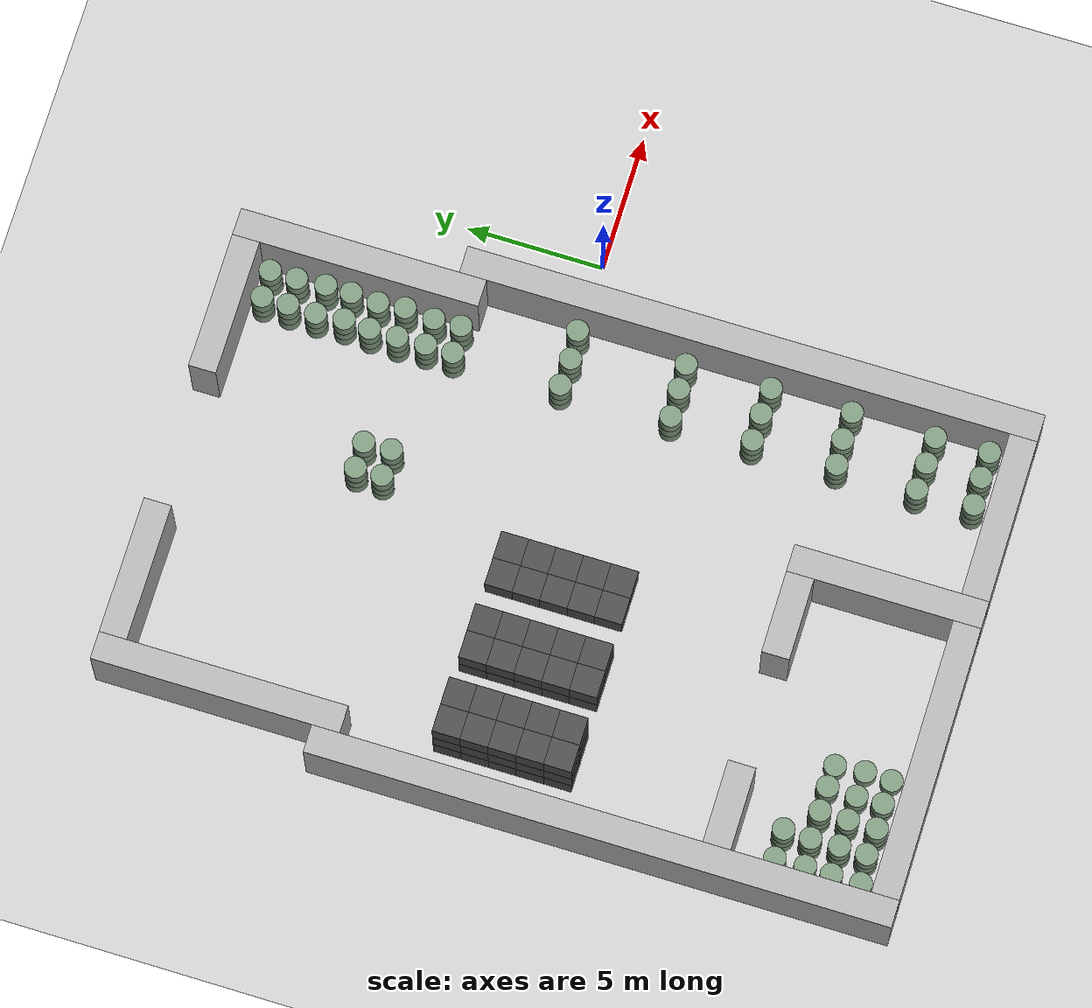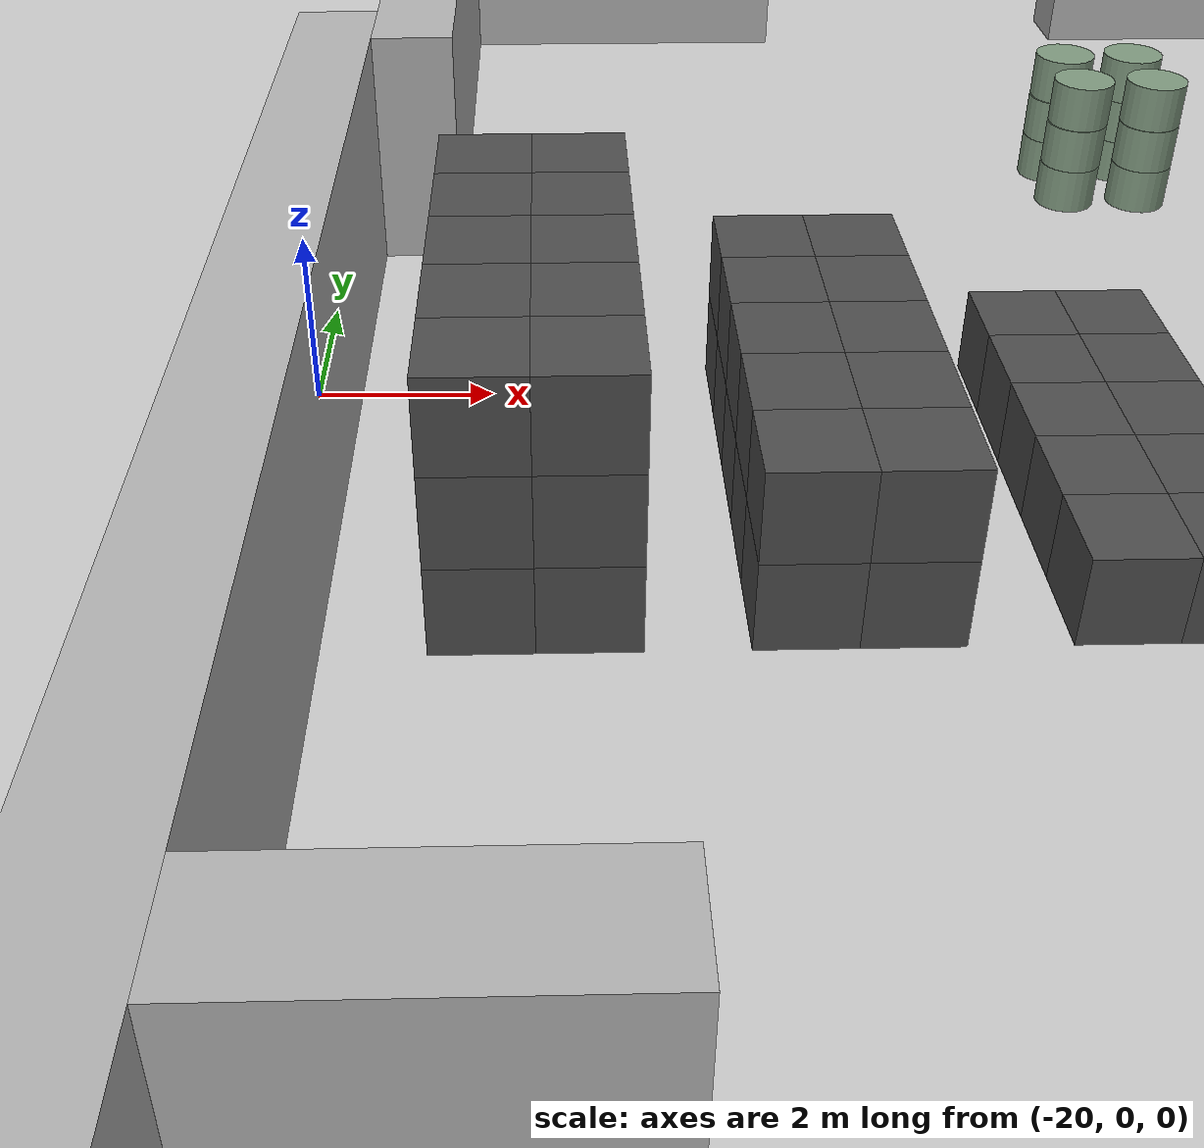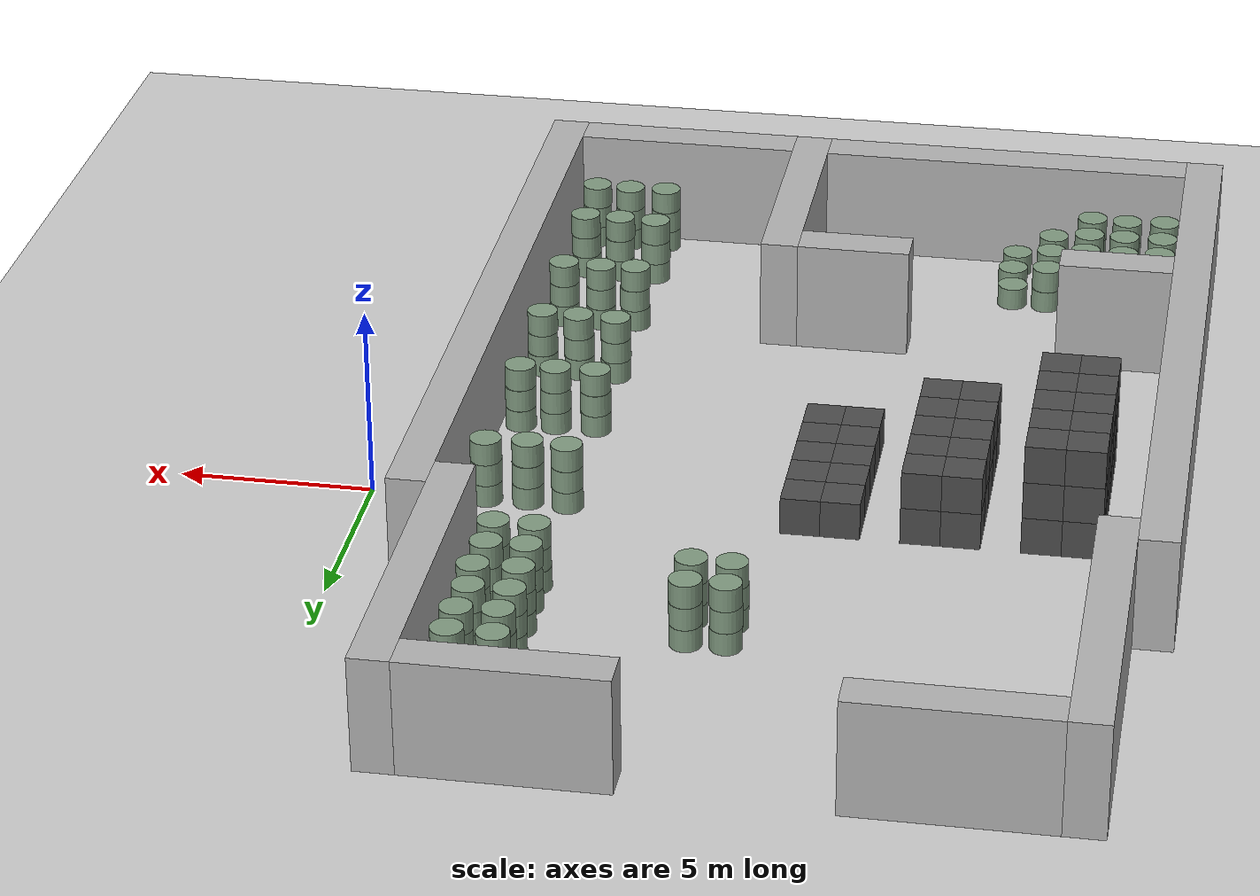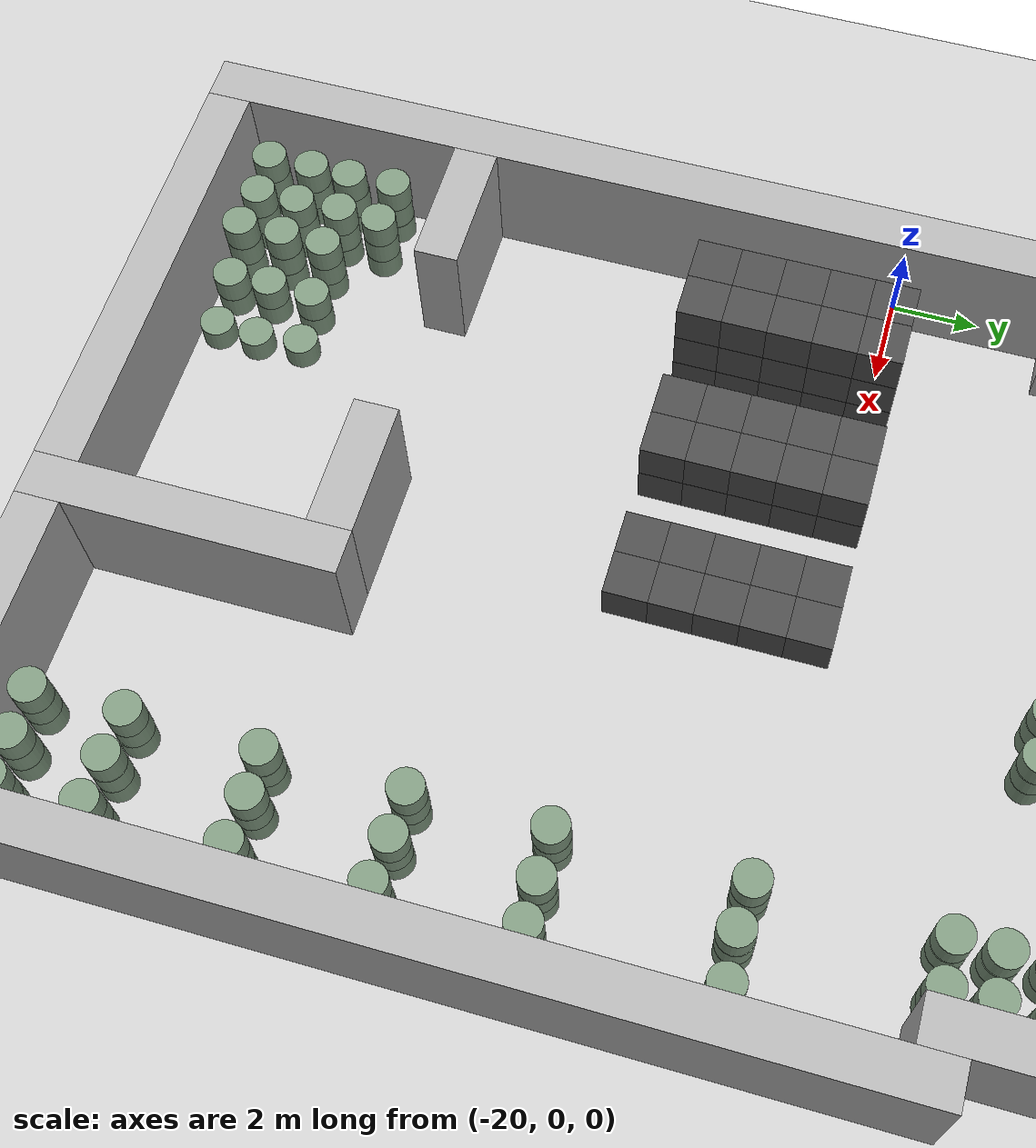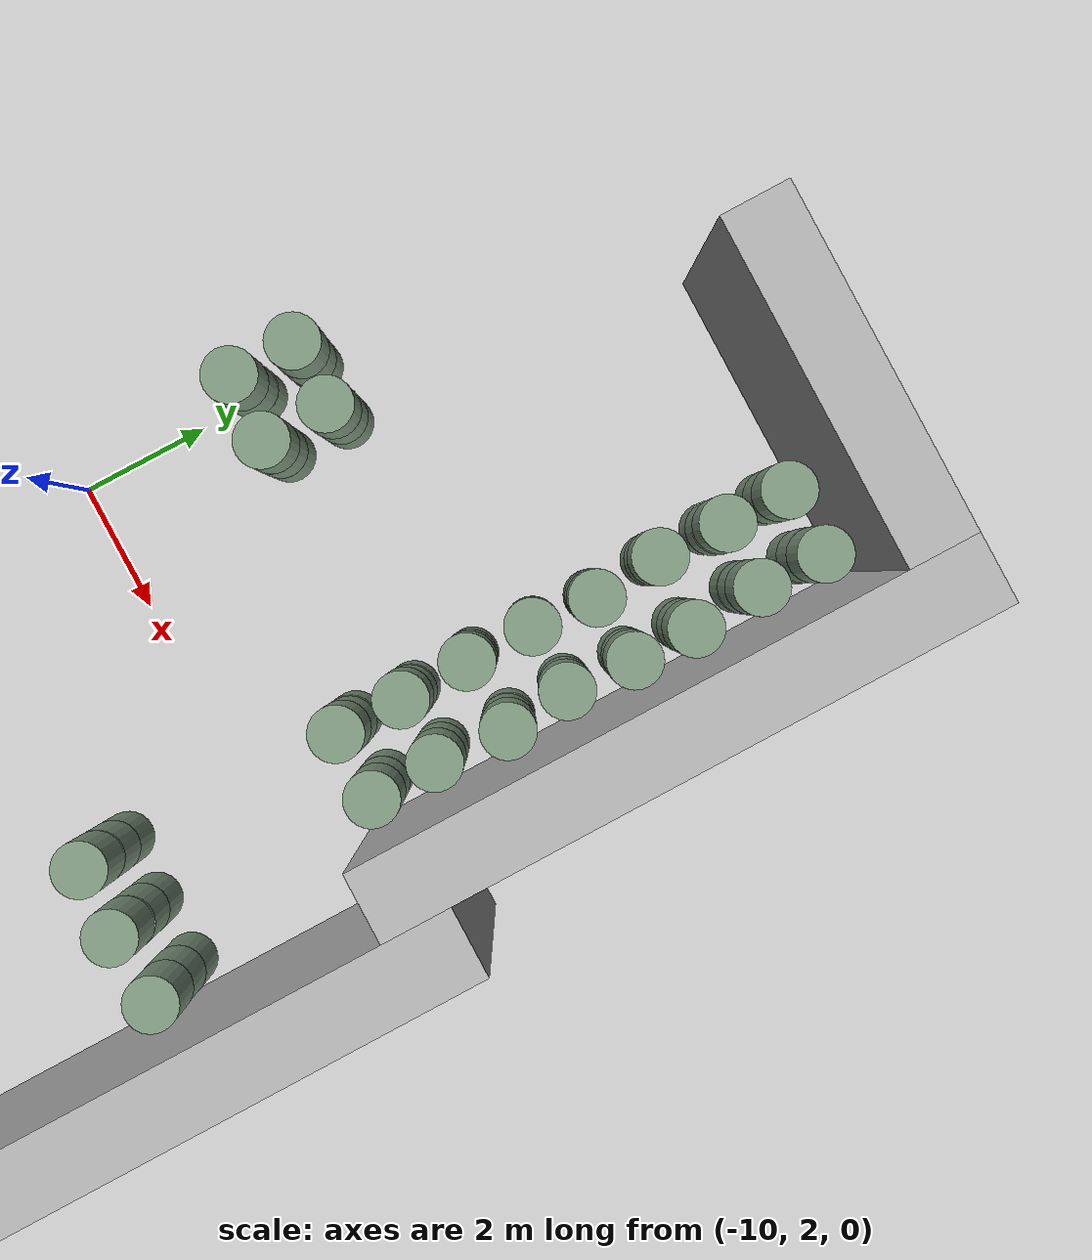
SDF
<sdf version="1.6">
 <world name="default">
  <light name="sun" type="directional">
   <cast_shadows>0</cast_shadows>
   <pose>0 0 10 0 -0 0</pose>
   <diffuse>0.8 0.8 0.8 1</diffuse>
   <specular>0.2 0.2 0.2 1</specular>
   <attenuation>
    <range>1000</range>
    <constant>0.9</constant>
    <linear>0.01</linear>
    <quadratic>0.001</quadratic>
   </attenuation>
   <direction>-0.5 0.1 -0.9</direction>
  </light>
  <include><uri>model://ground_plane</uri></include>
  <gravity>0 0 -9.8</gravity>
  <magnetic_field>6e-06 2.3e-05 -4.2e-05</magnetic_field>
  <atmosphere type="adiabatic"/>
  <physics name="default_physics" default="0" type="ode">
   <max_step_size>0.001</max_step_size>
   <real_time_factor>1</real_time_factor>
   <real_time_update_rate>1000</real_time_update_rate>
  </physics>
  <scene><ambient>0.4 0.4 0.4 1</ambient><background>0.7 0.7 0.7 1</background><shadows>0</shadows></scene>
  <spherical_coordinates>
   <surface_model>EARTH_WGS84</surface_model>
   <latitude_deg>0</latitude_deg>
   <longitude_deg>0</longitude_deg>
   <elevation>0</elevation>
   <heading_deg>0</heading_deg>
  </spherical_coordinates>
  <model name="wall_0">
   <pose>-20.0 -6.0 1.5 0 -0 0</pose>
   <static>True</static>
   <link name="link">
    <inertial>
     <mass>100</mass>
     <inertia>
      <ixx>0.166667</ixx>
      <ixy>0</ixy>
      <ixz>0</ixz>
      <iyy>0.166667</iyy>
      <iyz>0</iyz>
      <izz>0.166667</izz>
     </inertia>
    </inertial>
    <collision name="collision"><geometry><box><size>1.0 21.0 3.0</size></box></geometry></collision>
    <visual name="visual">
     <geometry><box><size>1.0 21.0 3.0</size></box></geometry>
     <material><ambient>0.7 0.7 0.7 1</ambient><diffuse>0.7 0.7 0.7 1</diffuse></material>
    </visual>
   </link>
  </model>
  <model name="wall_1">
   <pose>-19.0 8.0 1.5 0 -0 0</pose>
   <static>True</static>
   <link name="link">
    <inertial>
     <mass>100</mass>
     <inertia>
      <ixx>0.166667</ixx>
      <ixy>0</ixy>
      <ixz>0</ixz>
      <iyy>0.166667</iyy>
      <iyz>0</iyz>
      <izz>0.166667</izz>
     </inertia>
    </inertial>
    <collision name="collision"><geometry><box><size>1.0 9.0 3.0</size></box></geometry></collision>
    <visual name="visual">
     <geometry><box><size>1.0 9.0 3.0</size></box></geometry>
     <material><ambient>0.7 0.7 0.7 1</ambient><diffuse>0.7 0.7 0.7 1</diffuse></material>
    </visual>
   </link>
  </model>
  <model name="wall_2">
   <pose>-9.0 -13.0 1.5 0 -0 0</pose>
   <static>True</static>
   <link name="link">
    <inertial>
     <mass>100</mass>
     <inertia>
      <ixx>0.166667</ixx>
      <ixy>0</ixy>
      <ixz>0</ixz>
      <iyy>0.166667</iyy>
      <iyz>0</iyz>
      <izz>0.166667</izz>
     </inertia>
    </inertial>
    <collision name="collision"><geometry><box><size>1.0 7.0 3.0</size></box></geometry></collision>
    <visual name="visual">
     <geometry><box><size>1.0 7.0 3.0</size></box></geometry>
     <material><ambient>0.7 0.7 0.7 1</ambient><diffuse>0.7 0.7 0.7 1</diffuse></material>
    </visual>
   </link>
  </model>
  <model name="wall_3">
   <pose>-3.0 8.0 1.5 0 -0 0</pose>
   <static>True</static>
   <link name="link">
    <inertial>
     <mass>100</mass>
     <inertia>
      <ixx>0.166667</ixx>
      <ixy>0</ixy>
      <ixz>0</ixz>
      <iyy>0.166667</iyy>
      <iyz>0</iyz>
      <izz>0.166667</izz>
     </inertia>
    </inertial>
    <collision name="collision"><geometry><box><size>1.0 9.0 3.0</size></box></geometry></collision>
    <visual name="visual">
     <geometry><box><size>1.0 9.0 3.0</size></box></geometry>
     <material><ambient>0.7 0.7 0.7 1</ambient><diffuse>0.7 0.7 0.7 1</diffuse></material>
    </visual>
   </link>
  </model>
  <model name="wall_4">
   <pose>-2.0 -6.0 1.5 0 -0 0</pose>
   <static>True</static>
   <link name="link">
    <inertial>
     <mass>100</mass>
     <inertia>
      <ixx>0.166667</ixx>
      <ixy>0</ixy>
      <ixz>0</ixz>
      <iyy>0.166667</iyy>
      <iyz>0</iyz>
      <izz>0.166667</izz>
     </inertia>
    </inertial>
    <collision name="collision"><geometry><box><size>1.0 21.0 3.0</size></box></geometry></collision>
    <visual name="visual">
     <geometry><box><size>1.0 21.0 3.0</size></box></geometry>
     <material><ambient>0.7 0.7 0.7 1</ambient><diffuse>0.7 0.7 0.7 1</diffuse></material>
    </visual>
   </link>
  </model>
  <model name="wall_5">
   <pose>-14.5 -16.0 1.5 0 -0 0</pose>
   <static>True</static>
   <link name="link">
    <inertial>
     <mass>100</mass>
     <inertia>
      <ixx>0.166667</ixx>
      <ixy>0</ixy>
      <ixz>0</ixz>
      <iyy>0.166667</iyy>
      <iyz>0</iyz>
      <izz>0.166667</izz>
     </inertia>
    </inertial>
    <collision name="collision"><geometry><box><size>10.0 1.0 3.0</size></box></geometry></collision>
    <visual name="visual">
     <geometry><box><size>10.0 1.0 3.0</size></box></geometry>
     <material><ambient>0.7 0.7 0.7 1</ambient><diffuse>0.7 0.7 0.7 1</diffuse></material>
    </visual>
   </link>
  </model>
  <model name="wall_6">
   <pose>-5.5 -16.0 1.5 0 -0 0</pose>
   <static>True</static>
   <link name="link">
    <inertial>
     <mass>100</mass>
     <inertia>
      <ixx>0.166667</ixx>
      <ixy>0</ixy>
      <ixz>0</ixz>
      <iyy>0.166667</iyy>
      <iyz>0</iyz>
      <izz>0.166667</izz>
     </inertia>
    </inertial>
    <collision name="collision"><geometry><box><size>6.0 1.0 3.0</size></box></geometry></collision>
    <visual name="visual">
     <geometry><box><size>6.0 1.0 3.0</size></box></geometry>
     <material><ambient>0.7 0.7 0.7 1</ambient><diffuse>0.7 0.7 0.7 1</diffuse></material>
    </visual>
   </link>
  </model>
  <model name="wall_7">
   <pose>-18.0 -10.0 1.5 0 -0 0</pose>
   <static>True</static>
   <link name="link">
    <inertial>
     <mass>100</mass>
     <inertia>
      <ixx>0.166667</ixx>
      <ixy>0</ixy>
      <ixz>0</ixz>
      <iyy>0.166667</iyy>
      <iyz>0</iyz>
      <izz>0.166667</izz>
     </inertia>
    </inertial>
    <collision name="collision"><geometry><box><size>3.0 1.0 3.0</size></box></geometry></collision>
    <visual name="visual">
     <geometry><box><size>3.0 1.0 3.0</size></box></geometry>
     <material><ambient>0.7 0.7 0.7 1</ambient><diffuse>0.7 0.7 0.7 1</diffuse></material>
    </visual>
   </link>
  </model>
  <model name="wall_8">
   <pose>-11.0 -10.0 1.5 0 -0 0</pose>
   <static>True</static>
   <link name="link">
    <inertial>
     <mass>100</mass>
     <inertia>
      <ixx>0.166667</ixx>
      <ixy>0</ixy>
      <ixz>0</ixz>
      <iyy>0.166667</iyy>
      <iyz>0</iyz>
      <izz>0.166667</izz>
     </inertia>
    </inertial>
    <collision name="collision"><geometry><box><size>3.0 1.0 3.0</size></box></geometry></collision>
    <visual name="visual">
     <geometry><box><size>3.0 1.0 3.0</size></box></geometry>
     <material><ambient>0.7 0.7 0.7 1</ambient><diffuse>0.7 0.7 0.7 1</diffuse></material>
    </visual>
   </link>
  </model>
  <model name="wall_9">
   <pose>-16.0 12.0 1.5 0 -0 0</pose>
   <static>True</static>
   <link name="link">
    <inertial>
     <mass>100</mass>
     <inertia>
      <ixx>0.166667</ixx>
      <ixy>0</ixy>
      <ixz>0</ixz>
      <iyy>0.166667</iyy>
      <iyz>0</iyz>
      <izz>0.166667</izz>
     </inertia>
    </inertial>
    <collision name="collision"><geometry><box><size>5.0 1.0 3.0</size></box></geometry></collision>
    <visual name="visual">
     <geometry><box><size>5.0 1.0 3.0</size></box></geometry>
     <material><ambient>0.7 0.7 0.7 1</ambient><diffuse>0.7 0.7 0.7 1</diffuse></material>
    </visual>
   </link>
  </model>
  <model name="wall_10">
   <pose>-6.0 12.0 1.5 0 -0 0</pose>
   <static>True</static>
   <link name="link">
    <inertial>
     <mass>100</mass>
     <inertia>
      <ixx>0.166667</ixx>
      <ixy>0</ixy>
      <ixz>0</ixz>
      <iyy>0.166667</iyy>
      <iyz>0</iyz>
      <izz>0.166667</izz>
     </inertia>
    </inertial>
    <collision name="collision"><geometry><box><size>5.0 1.0 3.0</size></box></geometry></collision>
    <visual name="visual">
     <geometry><box><size>5.0 1.0 3.0</size></box></geometry>
     <material><ambient>0.7 0.7 0.7 1</ambient><diffuse>0.7 0.7 0.7 1</diffuse></material>
    </visual>
   </link>
  </model>
  <model name="unit_box_0">
   <pose>-18.0 -4.0 0.5 0 -0 0</pose>
   <static>True</static>
   <link name="link">
    <inertial>
     <mass>100</mass>
     <inertia>
      <ixx>0.166667</ixx>
      <ixy>0</ixy>
      <ixz>0</ixz>
      <iyy>0.166667</iyy>
      <iyz>0</iyz>
      <izz>0.166667</izz>
     </inertia>
    </inertial>
    <collision name="collision"><geometry><box><size>1.0 1.0 1.0</size></box></geometry></collision>
    <visual name="visual">
     <geometry><box><size>1.0 1.0 1.0</size></box></geometry>
     <material><ambient>0.3 0.3 0.3 1</ambient><diffuse>0.3 0.3 0.3 1</diffuse></material>
    </visual>
   </link>
  </model>
  <model name="unit_box_1">
   <pose>-18.0 -4.0 1.5 0 -0 0</pose>
   <static>True</static>
   <link name="link">
    <inertial>
     <mass>100</mass>
     <inertia>
      <ixx>0.166667</ixx>
      <ixy>0</ixy>
      <ixz>0</ixz>
      <iyy>0.166667</iyy>
      <iyz>0</iyz>
      <izz>0.166667</izz>
     </inertia>
    </inertial>
    <collision name="collision"><geometry><box><size>1.0 1.0 1.0</size></box></geometry></collision>
    <visual name="visual">
     <geometry><box><size>1.0 1.0 1.0</size></box></geometry>
     <material><ambient>0.3 0.3 0.3 1</ambient><diffuse>0.3 0.3 0.3 1</diffuse></material>
    </visual>
   </link>
  </model>
  <model name="unit_box_2">
   <pose>-18.0 -4.0 2.5 0 -0 0</pose>
   <static>True</static>
   <link name="link">
    <inertial>
     <mass>100</mass>
     <inertia>
      <ixx>0.166667</ixx>
      <ixy>0</ixy>
      <ixz>0</ixz>
      <iyy>0.166667</iyy>
      <iyz>0</iyz>
      <izz>0.166667</izz>
     </inertia>
    </inertial>
    <collision name="collision"><geometry><box><size>1.0 1.0 1.0</size></box></geometry></collision>
    <visual name="visual">
     <geometry><box><size>1.0 1.0 1.0</size></box></geometry>
     <material><ambient>0.3 0.3 0.3 1</ambient><diffuse>0.3 0.3 0.3 1</diffuse></material>
    </visual>
   </link>
  </model>
  <model name="unit_box_3">
   <pose>-18.0 -3.0 0.5 0 -0 0</pose>
   <static>True</static>
   <link name="link">
    <inertial>
     <mass>100</mass>
     <inertia>
      <ixx>0.166667</ixx>
      <ixy>0</ixy>
      <ixz>0</ixz>
      <iyy>0.166667</iyy>
      <iyz>0</iyz>
      <izz>0.166667</izz>
     </inertia>
    </inertial>
    <collision name="collision"><geometry><box><size>1.0 1.0 1.0</size></box></geometry></collision>
    <visual name="visual">
     <geometry><box><size>1.0 1.0 1.0</size></box></geometry>
     <material><ambient>0.3 0.3 0.3 1</ambient><diffuse>0.3 0.3 0.3 1</diffuse></material>
    </visual>
   </link>
  </model>
  <model name="unit_box_4">
   <pose>-18.0 -3.0 1.5 0 -0 0</pose>
   <static>True</static>
   <link name="link">
    <inertial>
     <mass>100</mass>
     <inertia>
      <ixx>0.166667</ixx>
      <ixy>0</ixy>
      <ixz>0</ixz>
      <iyy>0.166667</iyy>
      <iyz>0</iyz>
      <izz>0.166667</izz>
     </inertia>
    </inertial>
    <collision name="collision"><geometry><box><size>1.0 1.0 1.0</size></box></geometry></collision>
    <visual name="visual">
     <geometry><box><size>1.0 1.0 1.0</size></box></geometry>
     <material><ambient>0.3 0.3 0.3 1</ambient><diffuse>0.3 0.3 0.3 1</diffuse></material>
    </visual>
   </link>
  </model>
  <model name="unit_box_5">
   <pose>-18.0 -3.0 2.5 0 -0 0</pose>
   <static>True</static>
   <link name="link">
    <inertial>
     <mass>100</mass>
     <inertia>
      <ixx>0.166667</ixx>
      <ixy>0</ixy>
      <ixz>0</ixz>
      <iyy>0.166667</iyy>
      <iyz>0</iyz>
      <izz>0.166667</izz>
     </inertia>
    </inertial>
    <collision name="collision"><geometry><box><size>1.0 1.0 1.0</size></box></geometry></collision>
    <visual name="visual">
     <geometry><box><size>1.0 1.0 1.0</size></box></geometry>
     <material><ambient>0.3 0.3 0.3 1</ambient><diffuse>0.3 0.3 0.3 1</diffuse></material>
    </visual>
   </link>
  </model>
  <model name="unit_box_6">
   <pose>-18.0 -2.0 0.5 0 -0 0</pose>
   <static>True</static>
   <link name="link">
    <inertial>
     <mass>100</mass>
     <inertia>
      <ixx>0.166667</ixx>
      <ixy>0</ixy>
      <ixz>0</ixz>
      <iyy>0.166667</iyy>
      <iyz>0</iyz>
      <izz>0.166667</izz>
     </inertia>
    </inertial>
    <collision name="collision"><geometry><box><size>1.0 1.0 1.0</size></box></geometry></collision>
    <visual name="visual">
     <geometry><box><size>1.0 1.0 1.0</size></box></geometry>
     <material><ambient>0.3 0.3 0.3 1</ambient><diffuse>0.3 0.3 0.3 1</diffuse></material>
    </visual>
   </link>
  </model>
  <model name="unit_box_7">
   <pose>-18.0 -2.0 1.5 0 -0 0</pose>
   <static>True</static>
   <link name="link">
    <inertial>
     <mass>100</mass>
     <inertia>
      <ixx>0.166667</ixx>
      <ixy>0</ixy>
      <ixz>0</ixz>
      <iyy>0.166667</iyy>
      <iyz>0</iyz>
      <izz>0.166667</izz>
     </inertia>
    </inertial>
    <collision name="collision"><geometry><box><size>1.0 1.0 1.0</size></box></geometry></collision>
    <visual name="visual">
     <geometry><box><size>1.0 1.0 1.0</size></box></geometry>
     <material><ambient>0.3 0.3 0.3 1</ambient><diffuse>0.3 0.3 0.3 1</diffuse></material>
    </visual>
   </link>
  </model>
  <model name="unit_box_8">
   <pose>-18.0 -2.0 2.5 0 -0 0</pose>
   <static>True</static>
   <link name="link">
    <inertial>
     <mass>100</mass>
     <inertia>
      <ixx>0.166667</ixx>
      <ixy>0</ixy>
      <ixz>0</ixz>
      <iyy>0.166667</iyy>
      <iyz>0</iyz>
      <izz>0.166667</izz>
     </inertia>
    </inertial>
    <collision name="collision"><geometry><box><size>1.0 1.0 1.0</size></box></geometry></collision>
    <visual name="visual">
     <geometry><box><size>1.0 1.0 1.0</size></box></geometry>
     <material><ambient>0.3 0.3 0.3 1</ambient><diffuse>0.3 0.3 0.3 1</diffuse></material>
    </visual>
   </link>
  </model>
  <model name="unit_box_9">
   <pose>-18.0 -1.0 0.5 0 -0 0</pose>
   <static>True</static>
   <link name="link">
    <inertial>
     <mass>100</mass>
     <inertia>
      <ixx>0.166667</ixx>
      <ixy>0</ixy>
      <ixz>0</ixz>
      <iyy>0.166667</iyy>
      <iyz>0</iyz>
      <izz>0.166667</izz>
     </inertia>
    </inertial>
    <collision name="collision"><geometry><box><size>1.0 1.0 1.0</size></box></geometry></collision>
    <visual name="visual">
     <geometry><box><size>1.0 1.0 1.0</size></box></geometry>
     <material><ambient>0.3 0.3 0.3 1</ambient><diffuse>0.3 0.3 0.3 1</diffuse></material>
    </visual>
   </link>
  </model>
  <model name="unit_box_10">
   <pose>-18.0 -1.0 1.5 0 -0 0</pose>
   <static>True</static>
   <link name="link">
    <inertial>
     <mass>100</mass>
     <inertia>
      <ixx>0.166667</ixx>
      <ixy>0</ixy>
      <ixz>0</ixz>
      <iyy>0.166667</iyy>
      <iyz>0</iyz>
      <izz>0.166667</izz>
     </inertia>
    </inertial>
    <collision name="collision"><geometry><box><size>1.0 1.0 1.0</size></box></geometry></collision>
    <visual name="visual">
     <geometry><box><size>1.0 1.0 1.0</size></box></geometry>
     <material><ambient>0.3 0.3 0.3 1</ambient><diffuse>0.3 0.3 0.3 1</diffuse></material>
    </visual>
   </link>
  </model>
  <model name="unit_box_11">
   <pose>-18.0 -1.0 2.5 0 -0 0</pose>
   <static>True</static>
   <link name="link">
    <inertial>
     <mass>100</mass>
     <inertia>
      <ixx>0.166667</ixx>
      <ixy>0</ixy>
      <ixz>0</ixz>
      <iyy>0.166667</iyy>
      <iyz>0</iyz>
      <izz>0.166667</izz>
     </inertia>
    </inertial>
    <collision name="collision"><geometry><box><size>1.0 1.0 1.0</size></box></geometry></collision>
    <visual name="visual">
     <geometry><box><size>1.0 1.0 1.0</size></box></geometry>
     <material><ambient>0.3 0.3 0.3 1</ambient><diffuse>0.3 0.3 0.3 1</diffuse></material>
    </visual>
   </link>
  </model>
  <model name="unit_box_12">
   <pose>-18.0 0.0 0.5 0 -0 0</pose>
   <static>True</static>
   <link name="link">
    <inertial>
     <mass>100</mass>
     <inertia>
      <ixx>0.166667</ixx>
      <ixy>0</ixy>
      <ixz>0</ixz>
      <iyy>0.166667</iyy>
      <iyz>0</iyz>
      <izz>0.166667</izz>
     </inertia>
    </inertial>
    <collision name="collision"><geometry><box><size>1.0 1.0 1.0</size></box></geometry></collision>
    <visual name="visual">
     <geometry><box><size>1.0 1.0 1.0</size></box></geometry>
     <material><ambient>0.3 0.3 0.3 1</ambient><diffuse>0.3 0.3 0.3 1</diffuse></material>
    </visual>
   </link>
  </model>
  <model name="unit_box_13">
   <pose>-18.0 0.0 1.5 0 -0 0</pose>
   <static>True</static>
   <link name="link">
    <inertial>
     <mass>100</mass>
     <inertia>
      <ixx>0.166667</ixx>
      <ixy>0</ixy>
      <ixz>0</ixz>
      <iyy>0.166667</iyy>
      <iyz>0</iyz>
      <izz>0.166667</izz>
     </inertia>
    </inertial>
    <collision name="collision"><geometry><box><size>1.0 1.0 1.0</size></box></geometry></collision>
    <visual name="visual">
     <geometry><box><size>1.0 1.0 1.0</size></box></geometry>
     <material><ambient>0.3 0.3 0.3 1</ambient><diffuse>0.3 0.3 0.3 1</diffuse></material>
    </visual>
   </link>
  </model>
  <model name="unit_box_14">
   <pose>-18.0 0.0 2.5 0 -0 0</pose>
   <static>True</static>
   <link name="link">
    <inertial>
     <mass>100</mass>
     <inertia>
      <ixx>0.166667</ixx>
      <ixy>0</ixy>
      <ixz>0</ixz>
      <iyy>0.166667</iyy>
      <iyz>0</iyz>
      <izz>0.166667</izz>
     </inertia>
    </inertial>
    <collision name="collision"><geometry><box><size>1.0 1.0 1.0</size></box></geometry></collision>
    <visual name="visual">
     <geometry><box><size>1.0 1.0 1.0</size></box></geometry>
     <material><ambient>0.3 0.3 0.3 1</ambient><diffuse>0.3 0.3 0.3 1</diffuse></material>
    </visual>
   </link>
  </model>
  <model name="unit_box_15">
   <pose>-17.0 -4.0 0.5 0 -0 0</pose>
   <static>True</static>
   <link name="link">
    <inertial>
     <mass>100</mass>
     <inertia>
      <ixx>0.166667</ixx>
      <ixy>0</ixy>
      <ixz>0</ixz>
      <iyy>0.166667</iyy>
      <iyz>0</iyz>
      <izz>0.166667</izz>
     </inertia>
    </inertial>
    <collision name="collision"><geometry><box><size>1.0 1.0 1.0</size></box></geometry></collision>
    <visual name="visual">
     <geometry><box><size>1.0 1.0 1.0</size></box></geometry>
     <material><ambient>0.3 0.3 0.3 1</ambient><diffuse>0.3 0.3 0.3 1</diffuse></material>
    </visual>
   </link>
  </model>
  <model name="unit_box_16">
   <pose>-17.0 -4.0 1.5 0 -0 0</pose>
   <static>True</static>
   <link name="link">
    <inertial>
     <mass>100</mass>
     <inertia>
      <ixx>0.166667</ixx>
      <ixy>0</ixy>
      <ixz>0</ixz>
      <iyy>0.166667</iyy>
      <iyz>0</iyz>
      <izz>0.166667</izz>
     </inertia>
    </inertial>
    <collision name="collision"><geometry><box><size>1.0 1.0 1.0</size></box></geometry></collision>
    <visual name="visual">
     <geometry><box><size>1.0 1.0 1.0</size></box></geometry>
     <material><ambient>0.3 0.3 0.3 1</ambient><diffuse>0.3 0.3 0.3 1</diffuse></material>
    </visual>
   </link>
  </model>
  <model name="unit_box_17">
   <pose>-17.0 -4.0 2.5 0 -0 0</pose>
   <static>True</static>
   <link name="link">
    <inertial>
     <mass>100</mass>
     <inertia>
      <ixx>0.166667</ixx>
      <ixy>0</ixy>
      <ixz>0</ixz>
      <iyy>0.166667</iyy>
      <iyz>0</iyz>
      <izz>0.166667</izz>
     </inertia>
    </inertial>
    <collision name="collision"><geometry><box><size>1.0 1.0 1.0</size></box></geometry></collision>
    <visual name="visual">
     <geometry><box><size>1.0 1.0 1.0</size></box></geometry>
     <material><ambient>0.3 0.3 0.3 1</ambient><diffuse>0.3 0.3 0.3 1</diffuse></material>
    </visual>
   </link>
  </model>
  <model name="unit_box_18">
   <pose>-17.0 -3.0 0.5 0 -0 0</pose>
   <static>True</static>
   <link name="link">
    <inertial>
     <mass>100</mass>
     <inertia>
      <ixx>0.166667</ixx>
      <ixy>0</ixy>
      <ixz>0</ixz>
      <iyy>0.166667</iyy>
      <iyz>0</iyz>
      <izz>0.166667</izz>
     </inertia>
    </inertial>
    <collision name="collision"><geometry><box><size>1.0 1.0 1.0</size></box></geometry></collision>
    <visual name="visual">
     <geometry><box><size>1.0 1.0 1.0</size></box></geometry>
     <material><ambient>0.3 0.3 0.3 1</ambient><diffuse>0.3 0.3 0.3 1</diffuse></material>
    </visual>
   </link>
  </model>
  <model name="unit_box_19">
   <pose>-17.0 -3.0 1.5 0 -0 0</pose>
   <static>True</static>
   <link name="link">
    <inertial>
     <mass>100</mass>
     <inertia>
      <ixx>0.166667</ixx>
      <ixy>0</ixy>
      <ixz>0</ixz>
      <iyy>0.166667</iyy>
      <iyz>0</iyz>
      <izz>0.166667</izz>
     </inertia>
    </inertial>
    <collision name="collision"><geometry><box><size>1.0 1.0 1.0</size></box></geometry></collision>
    <visual name="visual">
     <geometry><box><size>1.0 1.0 1.0</size></box></geometry>
     <material><ambient>0.3 0.3 0.3 1</ambient><diffuse>0.3 0.3 0.3 1</diffuse></material>
    </visual>
   </link>
  </model>
  <model name="unit_box_20">
   <pose>-17.0 -3.0 2.5 0 -0 0</pose>
   <static>True</static>
   <link name="link">
    <inertial>
     <mass>100</mass>
     <inertia>
      <ixx>0.166667</ixx>
      <ixy>0</ixy>
      <ixz>0</ixz>
      <iyy>0.166667</iyy>
      <iyz>0</iyz>
      <izz>0.166667</izz>
     </inertia>
    </inertial>
    <collision name="collision"><geometry><box><size>1.0 1.0 1.0</size></box></geometry></collision>
    <visual name="visual">
     <geometry><box><size>1.0 1.0 1.0</size></box></geometry>
     <material><ambient>0.3 0.3 0.3 1</ambient><diffuse>0.3 0.3 0.3 1</diffuse></material>
    </visual>
   </link>
  </model>
  <model name="unit_box_21">
   <pose>-17.0 -2.0 0.5 0 -0 0</pose>
   <static>True</static>
   <link name="link">
    <inertial>
     <mass>100</mass>
     <inertia>
      <ixx>0.166667</ixx>
      <ixy>0</ixy>
      <ixz>0</ixz>
      <iyy>0.166667</iyy>
      <iyz>0</iyz>
      <izz>0.166667</izz>
     </inertia>
    </inertial>
    <collision name="collision"><geometry><box><size>1.0 1.0 1.0</size></box></geometry></collision>
    <visual name="visual">
     <geometry><box><size>1.0 1.0 1.0</size></box></geometry>
     <material><ambient>0.3 0.3 0.3 1</ambient><diffuse>0.3 0.3 0.3 1</diffuse></material>
    </visual>
   </link>
  </model>
  <model name="unit_box_22">
   <pose>-17.0 -2.0 1.5 0 -0 0</pose>
   <static>True</static>
   <link name="link">
    <inertial>
     <mass>100</mass>
     <inertia>
      <ixx>0.166667</ixx>
      <ixy>0</ixy>
      <ixz>0</ixz>
      <iyy>0.166667</iyy>
      <iyz>0</iyz>
      <izz>0.166667</izz>
     </inertia>
    </inertial>
    <collision name="collision"><geometry><box><size>1.0 1.0 1.0</size></box></geometry></collision>
    <visual name="visual">
     <geometry><box><size>1.0 1.0 1.0</size></box></geometry>
     <material><ambient>0.3 0.3 0.3 1</ambient><diffuse>0.3 0.3 0.3 1</diffuse></material>
    </visual>
   </link>
  </model>
  <model name="unit_box_23">
   <pose>-17.0 -2.0 2.5 0 -0 0</pose>
   <static>True</static>
   <link name="link">
    <inertial>
     <mass>100</mass>
     <inertia>
      <ixx>0.166667</ixx>
      <ixy>0</ixy>
      <ixz>0</ixz>
      <iyy>0.166667</iyy>
      <iyz>0</iyz>
      <izz>0.166667</izz>
     </inertia>
    </inertial>
    <collision name="collision"><geometry><box><size>1.0 1.0 1.0</size></box></geometry></collision>
    <visual name="visual">
     <geometry><box><size>1.0 1.0 1.0</size></box></geometry>
     <material><ambient>0.3 0.3 0.3 1</ambient><diffuse>0.3 0.3 0.3 1</diffuse></material>
    </visual>
   </link>
  </model>
  <model name="unit_box_24">
   <pose>-17.0 -1.0 0.5 0 -0 0</pose>
   <static>True</static>
   <link name="link">
    <inertial>
     <mass>100</mass>
     <inertia>
      <ixx>0.166667</ixx>
      <ixy>0</ixy>
      <ixz>0</ixz>
      <iyy>0.166667</iyy>
      <iyz>0</iyz>
      <izz>0.166667</izz>
     </inertia>
    </inertial>
    <collision name="collision"><geometry><box><size>1.0 1.0 1.0</size></box></geometry></collision>
    <visual name="visual">
     <geometry><box><size>1.0 1.0 1.0</size></box></geometry>
     <material><ambient>0.3 0.3 0.3 1</ambient><diffuse>0.3 0.3 0.3 1</diffuse></material>
    </visual>
   </link>
  </model>
  <model name="unit_box_25">
   <pose>-17.0 -1.0 1.5 0 -0 0</pose>
   <static>True</static>
   <link name="link">
    <inertial>
     <mass>100</mass>
     <inertia>
      <ixx>0.166667</ixx>
      <ixy>0</ixy>
      <ixz>0</ixz>
      <iyy>0.166667</iyy>
      <iyz>0</iyz>
      <izz>0.166667</izz>
     </inertia>
    </inertial>
    <collision name="collision"><geometry><box><size>1.0 1.0 1.0</size></box></geometry></collision>
    <visual name="visual">
     <geometry><box><size>1.0 1.0 1.0</size></box></geometry>
     <material><ambient>0.3 0.3 0.3 1</ambient><diffuse>0.3 0.3 0.3 1</diffuse></material>
    </visual>
   </link>
  </model>
  <model name="unit_box_26">
   <pose>-17.0 -1.0 2.5 0 -0 0</pose>
   <static>True</static>
   <link name="link">
    <inertial>
     <mass>100</mass>
     <inertia>
      <ixx>0.166667</ixx>
      <ixy>0</ixy>
      <ixz>0</ixz>
      <iyy>0.166667</iyy>
      <iyz>0</iyz>
      <izz>0.166667</izz>
     </inertia>
    </inertial>
    <collision name="collision"><geometry><box><size>1.0 1.0 1.0</size></box></geometry></collision>
    <visual name="visual">
     <geometry><box><size>1.0 1.0 1.0</size></box></geometry>
     <material><ambient>0.3 0.3 0.3 1</ambient><diffuse>0.3 0.3 0.3 1</diffuse></material>
    </visual>
   </link>
  </model>
  <model name="unit_box_27">
   <pose>-17.0 0.0 0.5 0 -0 0</pose>
   <static>True</static>
   <link name="link">
    <inertial>
     <mass>100</mass>
     <inertia>
      <ixx>0.166667</ixx>
      <ixy>0</ixy>
      <ixz>0</ixz>
      <iyy>0.166667</iyy>
      <iyz>0</iyz>
      <izz>0.166667</izz>
     </inertia>
    </inertial>
    <collision name="collision"><geometry><box><size>1.0 1.0 1.0</size></box></geometry></collision>
    <visual name="visual">
     <geometry><box><size>1.0 1.0 1.0</size></box></geometry>
     <material><ambient>0.3 0.3 0.3 1</ambient><diffuse>0.3 0.3 0.3 1</diffuse></material>
    </visual>
   </link>
  </model>
  <model name="unit_box_28">
   <pose>-17.0 0.0 1.5 0 -0 0</pose>
   <static>True</static>
   <link name="link">
    <inertial>
     <mass>100</mass>
     <inertia>
      <ixx>0.166667</ixx>
      <ixy>0</ixy>
      <ixz>0</ixz>
      <iyy>0.166667</iyy>
      <iyz>0</iyz>
      <izz>0.166667</izz>
     </inertia>
    </inertial>
    <collision name="collision"><geometry><box><size>1.0 1.0 1.0</size></box></geometry></collision>
    <visual name="visual">
     <geometry><box><size>1.0 1.0 1.0</size></box></geometry>
     <material><ambient>0.3 0.3 0.3 1</ambient><diffuse>0.3 0.3 0.3 1</diffuse></material>
    </visual>
   </link>
  </model>
  <model name="unit_box_29">
   <pose>-17.0 0.0 2.5 0 -0 0</pose>
   <static>True</static>
   <link name="link">
    <inertial>
     <mass>100</mass>
     <inertia>
      <ixx>0.166667</ixx>
      <ixy>0</ixy>
      <ixz>0</ixz>
      <iyy>0.166667</iyy>
      <iyz>0</iyz>
      <izz>0.166667</izz>
     </inertia>
    </inertial>
    <collision name="collision"><geometry><box><size>1.0 1.0 1.0</size></box></geometry></collision>
    <visual name="visual">
     <geometry><box><size>1.0 1.0 1.0</size></box></geometry>
     <material><ambient>0.3 0.3 0.3 1</ambient><diffuse>0.3 0.3 0.3 1</diffuse></material>
    </visual>
   </link>
  </model>
  <model name="unit_box_30">
   <pose>-15.0 -4.0 0.5 0 -0 0</pose>
   <static>True</static>
   <link name="link">
    <inertial>
     <mass>100</mass>
     <inertia>
      <ixx>0.166667</ixx>
      <ixy>0</ixy>
      <ixz>0</ixz>
      <iyy>0.166667</iyy>
      <iyz>0</iyz>
      <izz>0.166667</izz>
     </inertia>
    </inertial>
    <collision name="collision"><geometry><box><size>1.0 1.0 1.0</size></box></geometry></collision>
    <visual name="visual">
     <geometry><box><size>1.0 1.0 1.0</size></box></geometry>
     <material><ambient>0.3 0.3 0.3 1</ambient><diffuse>0.3 0.3 0.3 1</diffuse></material>
    </visual>
   </link>
  </model>
  <model name="unit_box_31">
   <pose>-15.0 -4.0 1.5 0 -0 0</pose>
   <static>True</static>
   <link name="link">
    <inertial>
     <mass>100</mass>
     <inertia>
      <ixx>0.166667</ixx>
      <ixy>0</ixy>
      <ixz>0</ixz>
      <iyy>0.166667</iyy>
      <iyz>0</iyz>
      <izz>0.166667</izz>
     </inertia>
    </inertial>
    <collision name="collision"><geometry><box><size>1.0 1.0 1.0</size></box></geometry></collision>
    <visual name="visual">
     <geometry><box><size>1.0 1.0 1.0</size></box></geometry>
     <material><ambient>0.3 0.3 0.3 1</ambient><diffuse>0.3 0.3 0.3 1</diffuse></material>
    </visual>
   </link>
  </model>
  <model name="unit_box_32">
   <pose>-15.0 -3.0 0.5 0 -0 0</pose>
   <static>True</static>
   <link name="link">
    <inertial>
     <mass>100</mass>
     <inertia>
      <ixx>0.166667</ixx>
      <ixy>0</ixy>
      <ixz>0</ixz>
      <iyy>0.166667</iyy>
      <iyz>0</iyz>
      <izz>0.166667</izz>
     </inertia>
    </inertial>
    <collision name="collision"><geometry><box><size>1.0 1.0 1.0</size></box></geometry></collision>
    <visual name="visual">
     <geometry><box><size>1.0 1.0 1.0</size></box></geometry>
     <material><ambient>0.3 0.3 0.3 1</ambient><diffuse>0.3 0.3 0.3 1</diffuse></material>
    </visual>
   </link>
  </model>
  <model name="unit_box_33">
   <pose>-15.0 -3.0 1.5 0 -0 0</pose>
   <static>True</static>
   <link name="link">
    <inertial>
     <mass>100</mass>
     <inertia>
      <ixx>0.166667</ixx>
      <ixy>0</ixy>
      <ixz>0</ixz>
      <iyy>0.166667</iyy>
      <iyz>0</iyz>
      <izz>0.166667</izz>
     </inertia>
    </inertial>
    <collision name="collision"><geometry><box><size>1.0 1.0 1.0</size></box></geometry></collision>
    <visual name="visual">
     <geometry><box><size>1.0 1.0 1.0</size></box></geometry>
     <material><ambient>0.3 0.3 0.3 1</ambient><diffuse>0.3 0.3 0.3 1</diffuse></material>
    </visual>
   </link>
  </model>
  <model name="unit_box_34">
   <pose>-15.0 -2.0 0.5 0 -0 0</pose>
   <static>True</static>
   <link name="link">
    <inertial>
     <mass>100</mass>
     <inertia>
      <ixx>0.166667</ixx>
      <ixy>0</ixy>
      <ixz>0</ixz>
      <iyy>0.166667</iyy>
      <iyz>0</iyz>
      <izz>0.166667</izz>
     </inertia>
    </inertial>
    <collision name="collision"><geometry><box><size>1.0 1.0 1.0</size></box></geometry></collision>
    <visual name="visual">
     <geometry><box><size>1.0 1.0 1.0</size></box></geometry>
     <material><ambient>0.3 0.3 0.3 1</ambient><diffuse>0.3 0.3 0.3 1</diffuse></material>
    </visual>
   </link>
  </model>
  <model name="unit_box_35">
   <pose>-15.0 -2.0 1.5 0 -0 0</pose>
   <static>True</static>
   <link name="link">
    <inertial>
     <mass>100</mass>
     <inertia>
      <ixx>0.166667</ixx>
      <ixy>0</ixy>
      <ixz>0</ixz>
      <iyy>0.166667</iyy>
      <iyz>0</iyz>
      <izz>0.166667</izz>
     </inertia>
    </inertial>
    <collision name="collision"><geometry><box><size>1.0 1.0 1.0</size></box></geometry></collision>
    <visual name="visual">
     <geometry><box><size>1.0 1.0 1.0</size></box></geometry>
     <material><ambient>0.3 0.3 0.3 1</ambient><diffuse>0.3 0.3 0.3 1</diffuse></material>
    </visual>
   </link>
  </model>
  <model name="unit_box_36">
   <pose>-15.0 -1.0 0.5 0 -0 0</pose>
   <static>True</static>
   <link name="link">
    <inertial>
     <mass>100</mass>
     <inertia>
      <ixx>0.166667</ixx>
      <ixy>0</ixy>
      <ixz>0</ixz>
      <iyy>0.166667</iyy>
      <iyz>0</iyz>
      <izz>0.166667</izz>
     </inertia>
    </inertial>
    <collision name="collision"><geometry><box><size>1.0 1.0 1.0</size></box></geometry></collision>
    <visual name="visual">
     <geometry><box><size>1.0 1.0 1.0</size></box></geometry>
     <material><ambient>0.3 0.3 0.3 1</ambient><diffuse>0.3 0.3 0.3 1</diffuse></material>
    </visual>
   </link>
  </model>
  <model name="unit_box_37">
   <pose>-15.0 -1.0 1.5 0 -0 0</pose>
   <static>True</static>
   <link name="link">
    <inertial>
     <mass>100</mass>
     <inertia>
      <ixx>0.166667</ixx>
      <ixy>0</ixy>
      <ixz>0</ixz>
      <iyy>0.166667</iyy>
      <iyz>0</iyz>
      <izz>0.166667</izz>
     </inertia>
    </inertial>
    <collision name="collision"><geometry><box><size>1.0 1.0 1.0</size></box></geometry></collision>
    <visual name="visual">
     <geometry><box><size>1.0 1.0 1.0</size></box></geometry>
     <material><ambient>0.3 0.3 0.3 1</ambient><diffuse>0.3 0.3 0.3 1</diffuse></material>
    </visual>
   </link>
  </model>
  <model name="unit_box_38">
   <pose>-15.0 0.0 0.5 0 -0 0</pose>
   <static>True</static>
   <link name="link">
    <inertial>
     <mass>100</mass>
     <inertia>
      <ixx>0.166667</ixx>
      <ixy>0</ixy>
      <ixz>0</ixz>
      <iyy>0.166667</iyy>
      <iyz>0</iyz>
      <izz>0.166667</izz>
     </inertia>
    </inertial>
    <collision name="collision"><geometry><box><size>1.0 1.0 1.0</size></box></geometry></collision>
    <visual name="visual">
     <geometry><box><size>1.0 1.0 1.0</size></box></geometry>
     <material><ambient>0.3 0.3 0.3 1</ambient><diffuse>0.3 0.3 0.3 1</diffuse></material>
    </visual>
   </link>
  </model>
  <model name="unit_box_39">
   <pose>-15.0 0.0 1.5 0 -0 0</pose>
   <static>True</static>
   <link name="link">
    <inertial>
     <mass>100</mass>
     <inertia>
      <ixx>0.166667</ixx>
      <ixy>0</ixy>
      <ixz>0</ixz>
      <iyy>0.166667</iyy>
      <iyz>0</iyz>
      <izz>0.166667</izz>
     </inertia>
    </inertial>
    <collision name="collision"><geometry><box><size>1.0 1.0 1.0</size></box></geometry></collision>
    <visual name="visual">
     <geometry><box><size>1.0 1.0 1.0</size></box></geometry>
     <material><ambient>0.3 0.3 0.3 1</ambient><diffuse>0.3 0.3 0.3 1</diffuse></material>
    </visual>
   </link>
  </model>
  <model name="unit_box_40">
   <pose>-14.0 -4.0 0.5 0 -0 0</pose>
   <static>True</static>
   <link name="link">
    <inertial>
     <mass>100</mass>
     <inertia>
      <ixx>0.166667</ixx>
      <ixy>0</ixy>
      <ixz>0</ixz>
      <iyy>0.166667</iyy>
      <iyz>0</iyz>
      <izz>0.166667</izz>
     </inertia>
    </inertial>
    <collision name="collision"><geometry><box><size>1.0 1.0 1.0</size></box></geometry></collision>
    <visual name="visual">
     <geometry><box><size>1.0 1.0 1.0</size></box></geometry>
     <material><ambient>0.3 0.3 0.3 1</ambient><diffuse>0.3 0.3 0.3 1</diffuse></material>
    </visual>
   </link>
  </model>
  <model name="unit_box_41">
   <pose>-14.0 -4.0 1.5 0 -0 0</pose>
   <static>True</static>
   <link name="link">
    <inertial>
     <mass>100</mass>
     <inertia>
      <ixx>0.166667</ixx>
      <ixy>0</ixy>
      <ixz>0</ixz>
      <iyy>0.166667</iyy>
      <iyz>0</iyz>
      <izz>0.166667</izz>
     </inertia>
    </inertial>
    <collision name="collision"><geometry><box><size>1.0 1.0 1.0</size></box></geometry></collision>
    <visual name="visual">
     <geometry><box><size>1.0 1.0 1.0</size></box></geometry>
     <material><ambient>0.3 0.3 0.3 1</ambient><diffuse>0.3 0.3 0.3 1</diffuse></material>
    </visual>
   </link>
  </model>
  <model name="unit_box_42">
   <pose>-14.0 -3.0 0.5 0 -0 0</pose>
   <static>True</static>
   <link name="link">
    <inertial>
     <mass>100</mass>
     <inertia>
      <ixx>0.166667</ixx>
      <ixy>0</ixy>
      <ixz>0</ixz>
      <iyy>0.166667</iyy>
      <iyz>0</iyz>
      <izz>0.166667</izz>
     </inertia>
    </inertial>
    <collision name="collision"><geometry><box><size>1.0 1.0 1.0</size></box></geometry></collision>
    <visual name="visual">
     <geometry><box><size>1.0 1.0 1.0</size></box></geometry>
     <material><ambient>0.3 0.3 0.3 1</ambient><diffuse>0.3 0.3 0.3 1</diffuse></material>
    </visual>
   </link>
  </model>
  <model name="unit_box_43">
   <pose>-14.0 -3.0 1.5 0 -0 0</pose>
   <static>True</static>
   <link name="link">
    <inertial>
     <mass>100</mass>
     <inertia>
      <ixx>0.166667</ixx>
      <ixy>0</ixy>
      <ixz>0</ixz>
      <iyy>0.166667</iyy>
      <iyz>0</iyz>
      <izz>0.166667</izz>
     </inertia>
    </inertial>
    <collision name="collision"><geometry><box><size>1.0 1.0 1.0</size></box></geometry></collision>
    <visual name="visual">
     <geometry><box><size>1.0 1.0 1.0</size></box></geometry>
     <material><ambient>0.3 0.3 0.3 1</ambient><diffuse>0.3 0.3 0.3 1</diffuse></material>
    </visual>
   </link>
  </model>
  <model name="unit_box_44">
   <pose>-14.0 -2.0 0.5 0 -0 0</pose>
   <static>True</static>
   <link name="link">
    <inertial>
     <mass>100</mass>
     <inertia>
      <ixx>0.166667</ixx>
      <ixy>0</ixy>
      <ixz>0</ixz>
      <iyy>0.166667</iyy>
      <iyz>0</iyz>
      <izz>0.166667</izz>
     </inertia>
    </inertial>
    <collision name="collision"><geometry><box><size>1.0 1.0 1.0</size></box></geometry></collision>
    <visual name="visual">
     <geometry><box><size>1.0 1.0 1.0</size></box></geometry>
     <material><ambient>0.3 0.3 0.3 1</ambient><diffuse>0.3 0.3 0.3 1</diffuse></material>
    </visual>
   </link>
  </model>
  <model name="unit_box_45">
   <pose>-14.0 -2.0 1.5 0 -0 0</pose>
   <static>True</static>
   <link name="link">
    <inertial>
     <mass>100</mass>
     <inertia>
      <ixx>0.166667</ixx>
      <ixy>0</ixy>
      <ixz>0</ixz>
      <iyy>0.166667</iyy>
      <iyz>0</iyz>
      <izz>0.166667</izz>
     </inertia>
    </inertial>
    <collision name="collision"><geometry><box><size>1.0 1.0 1.0</size></box></geometry></collision>
    <visual name="visual">
     <geometry><box><size>1.0 1.0 1.0</size></box></geometry>
     <material><ambient>0.3 0.3 0.3 1</ambient><diffuse>0.3 0.3 0.3 1</diffuse></material>
    </visual>
   </link>
  </model>
  <model name="unit_box_46">
   <pose>-14.0 -1.0 0.5 0 -0 0</pose>
   <static>True</static>
   <link name="link">
    <inertial>
     <mass>100</mass>
     <inertia>
      <ixx>0.166667</ixx>
      <ixy>0</ixy>
      <ixz>0</ixz>
      <iyy>0.166667</iyy>
      <iyz>0</iyz>
      <izz>0.166667</izz>
     </inertia>
    </inertial>
    <collision name="collision"><geometry><box><size>1.0 1.0 1.0</size></box></geometry></collision>
    <visual name="visual">
     <geometry><box><size>1.0 1.0 1.0</size></box></geometry>
     <material><ambient>0.3 0.3 0.3 1</ambient><diffuse>0.3 0.3 0.3 1</diffuse></material>
    </visual>
   </link>
  </model>
  <model name="unit_box_47">
   <pose>-14.0 -1.0 1.5 0 -0 0</pose>
   <static>True</static>
   <link name="link">
    <inertial>
     <mass>100</mass>
     <inertia>
      <ixx>0.166667</ixx>
      <ixy>0</ixy>
      <ixz>0</ixz>
      <iyy>0.166667</iyy>
      <iyz>0</iyz>
      <izz>0.166667</izz>
     </inertia>
    </inertial>
    <collision name="collision"><geometry><box><size>1.0 1.0 1.0</size></box></geometry></collision>
    <visual name="visual">
     <geometry><box><size>1.0 1.0 1.0</size></box></geometry>
     <material><ambient>0.3 0.3 0.3 1</ambient><diffuse>0.3 0.3 0.3 1</diffuse></material>
    </visual>
   </link>
  </model>
  <model name="unit_box_48">
   <pose>-14.0 0.0 0.5 0 -0 0</pose>
   <static>True</static>
   <link name="link">
    <inertial>
     <mass>100</mass>
     <inertia>
      <ixx>0.166667</ixx>
      <ixy>0</ixy>
      <ixz>0</ixz>
      <iyy>0.166667</iyy>
      <iyz>0</iyz>
      <izz>0.166667</izz>
     </inertia>
    </inertial>
    <collision name="collision"><geometry><box><size>1.0 1.0 1.0</size></box></geometry></collision>
    <visual name="visual">
     <geometry><box><size>1.0 1.0 1.0</size></box></geometry>
     <material><ambient>0.3 0.3 0.3 1</ambient><diffuse>0.3 0.3 0.3 1</diffuse></material>
    </visual>
   </link>
  </model>
  <model name="unit_box_49">
   <pose>-14.0 0.0 1.5 0 -0 0</pose>
   <static>True</static>
   <link name="link">
    <inertial>
     <mass>100</mass>
     <inertia>
      <ixx>0.166667</ixx>
      <ixy>0</ixy>
      <ixz>0</ixz>
      <iyy>0.166667</iyy>
      <iyz>0</iyz>
      <izz>0.166667</izz>
     </inertia>
    </inertial>
    <collision name="collision"><geometry><box><size>1.0 1.0 1.0</size></box></geometry></collision>
    <visual name="visual">
     <geometry><box><size>1.0 1.0 1.0</size></box></geometry>
     <material><ambient>0.3 0.3 0.3 1</ambient><diffuse>0.3 0.3 0.3 1</diffuse></material>
    </visual>
   </link>
  </model>
  <model name="unit_box_50">
   <pose>-12.0 -4.0 0.5 0 -0 0</pose>
   <static>True</static>
   <link name="link">
    <inertial>
     <mass>100</mass>
     <inertia>
      <ixx>0.166667</ixx>
      <ixy>0</ixy>
      <ixz>0</ixz>
      <iyy>0.166667</iyy>
      <iyz>0</iyz>
      <izz>0.166667</izz>
     </inertia>
    </inertial>
    <collision name="collision"><geometry><box><size>1.0 1.0 1.0</size></box></geometry></collision>
    <visual name="visual">
     <geometry><box><size>1.0 1.0 1.0</size></box></geometry>
     <material><ambient>0.3 0.3 0.3 1</ambient><diffuse>0.3 0.3 0.3 1</diffuse></material>
    </visual>
   </link>
  </model>
  <model name="unit_box_51">
   <pose>-12.0 -3.0 0.5 0 -0 0</pose>
   <static>True</static>
   <link name="link">
    <inertial>
     <mass>100</mass>
     <inertia>
      <ixx>0.166667</ixx>
      <ixy>0</ixy>
      <ixz>0</ixz>
      <iyy>0.166667</iyy>
      <iyz>0</iyz>
      <izz>0.166667</izz>
     </inertia>
    </inertial>
    <collision name="collision"><geometry><box><size>1.0 1.0 1.0</size></box></geometry></collision>
    <visual name="visual">
     <geometry><box><size>1.0 1.0 1.0</size></box></geometry>
     <material><ambient>0.3 0.3 0.3 1</ambient><diffuse>0.3 0.3 0.3 1</diffuse></material>
    </visual>
   </link>
  </model>
  <model name="unit_box_52">
   <pose>-12.0 -2.0 0.5 0 -0 0</pose>
   <static>True</static>
   <link name="link">
    <inertial>
     <mass>100</mass>
     <inertia>
      <ixx>0.166667</ixx>
      <ixy>0</ixy>
      <ixz>0</ixz>
      <iyy>0.166667</iyy>
      <iyz>0</iyz>
      <izz>0.166667</izz>
     </inertia>
    </inertial>
    <collision name="collision"><geometry><box><size>1.0 1.0 1.0</size></box></geometry></collision>
    <visual name="visual">
     <geometry><box><size>1.0 1.0 1.0</size></box></geometry>
     <material><ambient>0.3 0.3 0.3 1</ambient><diffuse>0.3 0.3 0.3 1</diffuse></material>
    </visual>
   </link>
  </model>
  <model name="unit_box_53">
   <pose>-12.0 -1.0 0.5 0 -0 0</pose>
   <static>True</static>
   <link name="link">
    <inertial>
     <mass>100</mass>
     <inertia>
      <ixx>0.166667</ixx>
      <ixy>0</ixy>
      <ixz>0</ixz>
      <iyy>0.166667</iyy>
      <iyz>0</iyz>
      <izz>0.166667</izz>
     </inertia>
    </inertial>
    <collision name="collision"><geometry><box><size>1.0 1.0 1.0</size></box></geometry></collision>
    <visual name="visual">
     <geometry><box><size>1.0 1.0 1.0</size></box></geometry>
     <material><ambient>0.3 0.3 0.3 1</ambient><diffuse>0.3 0.3 0.3 1</diffuse></material>
    </visual>
   </link>
  </model>
  <model name="unit_box_54">
   <pose>-12.0 0.0 0.5 0 -0 0</pose>
   <static>True</static>
   <link name="link">
    <inertial>
     <mass>100</mass>
     <inertia>
      <ixx>0.166667</ixx>
      <ixy>0</ixy>
      <ixz>0</ixz>
      <iyy>0.166667</iyy>
      <iyz>0</iyz>
      <izz>0.166667</izz>
     </inertia>
    </inertial>
    <collision name="collision"><geometry><box><size>1.0 1.0 1.0</size></box></geometry></collision>
    <visual name="visual">
     <geometry><box><size>1.0 1.0 1.0</size></box></geometry>
     <material><ambient>0.3 0.3 0.3 1</ambient><diffuse>0.3 0.3 0.3 1</diffuse></material>
    </visual>
   </link>
  </model>
  <model name="unit_box_55">
   <pose>-11.0 -4.0 0.5 0 -0 0</pose>
   <static>True</static>
   <link name="link">
    <inertial>
     <mass>100</mass>
     <inertia>
      <ixx>0.166667</ixx>
      <ixy>0</ixy>
      <ixz>0</ixz>
      <iyy>0.166667</iyy>
      <iyz>0</iyz>
      <izz>0.166667</izz>
     </inertia>
    </inertial>
    <collision name="collision"><geometry><box><size>1.0 1.0 1.0</size></box></geometry></collision>
    <visual name="visual">
     <geometry><box><size>1.0 1.0 1.0</size></box></geometry>
     <material><ambient>0.3 0.3 0.3 1</ambient><diffuse>0.3 0.3 0.3 1</diffuse></material>
    </visual>
   </link>
  </model>
  <model name="unit_box_56">
   <pose>-11.0 -3.0 0.5 0 -0 0</pose>
   <static>True</static>
   <link name="link">
    <inertial>
     <mass>100</mass>
     <inertia>
      <ixx>0.166667</ixx>
      <ixy>0</ixy>
      <ixz>0</ixz>
      <iyy>0.166667</iyy>
      <iyz>0</iyz>
      <izz>0.166667</izz>
     </inertia>
    </inertial>
    <collision name="collision"><geometry><box><size>1.0 1.0 1.0</size></box></geometry></collision>
    <visual name="visual">
     <geometry><box><size>1.0 1.0 1.0</size></box></geometry>
     <material><ambient>0.3 0.3 0.3 1</ambient><diffuse>0.3 0.3 0.3 1</diffuse></material>
    </visual>
   </link>
  </model>
  <model name="unit_box_57">
   <pose>-11.0 -2.0 0.5 0 -0 0</pose>
   <static>True</static>
   <link name="link">
    <inertial>
     <mass>100</mass>
     <inertia>
      <ixx>0.166667</ixx>
      <ixy>0</ixy>
      <ixz>0</ixz>
      <iyy>0.166667</iyy>
      <iyz>0</iyz>
      <izz>0.166667</izz>
     </inertia>
    </inertial>
    <collision name="collision"><geometry><box><size>1.0 1.0 1.0</size></box></geometry></collision>
    <visual name="visual">
     <geometry><box><size>1.0 1.0 1.0</size></box></geometry>
     <material><ambient>0.3 0.3 0.3 1</ambient><diffuse>0.3 0.3 0.3 1</diffuse></material>
    </visual>
   </link>
  </model>
  <model name="unit_box_58">
   <pose>-11.0 -1.0 0.5 0 -0 0</pose>
   <static>True</static>
   <link name="link">
    <inertial>
     <mass>100</mass>
     <inertia>
      <ixx>0.166667</ixx>
      <ixy>0</ixy>
      <ixz>0</ixz>
      <iyy>0.166667</iyy>
      <iyz>0</iyz>
      <izz>0.166667</izz>
     </inertia>
    </inertial>
    <collision name="collision"><geometry><box><size>1.0 1.0 1.0</size></box></geometry></collision>
    <visual name="visual">
     <geometry><box><size>1.0 1.0 1.0</size></box></geometry>
     <material><ambient>0.3 0.3 0.3 1</ambient><diffuse>0.3 0.3 0.3 1</diffuse></material>
    </visual>
   </link>
  </model>
  <model name="unit_box_59">
   <pose>-11.0 0.0 0.5 0 -0 0</pose>
   <static>True</static>
   <link name="link">
    <inertial>
     <mass>100</mass>
     <inertia>
      <ixx>0.166667</ixx>
      <ixy>0</ixy>
      <ixz>0</ixz>
      <iyy>0.166667</iyy>
      <iyz>0</iyz>
      <izz>0.166667</izz>
     </inertia>
    </inertial>
    <collision name="collision"><geometry><box><size>1.0 1.0 1.0</size></box></geometry></collision>
    <visual name="visual">
     <geometry><box><size>1.0 1.0 1.0</size></box></geometry>
     <material><ambient>0.3 0.3 0.3 1</ambient><diffuse>0.3 0.3 0.3 1</diffuse></material>
    </visual>
   </link>
  </model>
  <model name="unit_cylinder_0">
   <pose>-19.0512213308 -15.0459810844 0.3 0 -0 0</pose>
   <static>True</static>
   <link name="link">
    <inertial>
     <mass>100</mass>
     <inertia><ixx>0.145833</ixx><ixy>0</ixy><ixz>0</ixz><iyy>0.145833</iyy><iyz>0</iyz><izz>0.125</izz></inertia>
    </inertial>
    <collision name="collision">
     <geometry><cylinder><radius>0.4</radius><length>0.6</length></cylinder></geometry>
     <max_contacts>100</max_contacts>
    </collision>
    <visual name="visual">
     <geometry><cylinder><radius>0.4</radius><length>0.6</length></cylinder></geometry>
     <material><ambient>0.5 0.6 0.5 1</ambient><diffuse>0.5 0.6 0.5 1</diffuse></material>
    </visual>
   </link>
  </model>
  <model name="unit_cylinder_1">
   <pose>-19.052392666 -15.0444953493 0.9 0 -0 0</pose>
   <static>True</static>
   <link name="link">
    <inertial>
     <mass>100</mass>
     <inertia><ixx>0.145833</ixx><ixy>0</ixy><ixz>0</ixz><iyy>0.145833</iyy><iyz>0</iyz><izz>0.125</izz></inertia>
    </inertial>
    <collision name="collision">
     <geometry><cylinder><radius>0.4</radius><length>0.6</length></cylinder></geometry>
     <max_contacts>100</max_contacts>
    </collision>
    <visual name="visual">
     <geometry><cylinder><radius>0.4</radius><length>0.6</length></cylinder></geometry>
     <material><ambient>0.5 0.6 0.5 1</ambient><diffuse>0.5 0.6 0.5 1</diffuse></material>
    </visual>
   </link>
  </model>
  <model name="unit_cylinder_2">
   <pose>-19.0430294251 -15.0452152705 1.5 0 -0 0</pose>
   <static>True</static>
   <link name="link">
    <inertial>
     <mass>100</mass>
     <inertia><ixx>0.145833</ixx><ixy>0</ixy><ixz>0</ixz><iyy>0.145833</iyy><iyz>0</iyz><izz>0.125</izz></inertia>
    </inertial>
    <collision name="collision">
     <geometry><cylinder><radius>0.4</radius><length>0.6</length></cylinder></geometry>
     <max_contacts>100</max_contacts>
    </collision>
    <visual name="visual">
     <geometry><cylinder><radius>0.4</radius><length>0.6</length></cylinder></geometry>
     <material><ambient>0.5 0.6 0.5 1</ambient><diffuse>0.5 0.6 0.5 1</diffuse></material>
    </visual>
   </link>
  </model>
  <model name="unit_cylinder_3">
   <pose>-19.0434055913 -13.9950863619 0.3 0 -0 0</pose>
   <static>True</static>
   <link name="link">
    <inertial>
     <mass>100</mass>
     <inertia><ixx>0.145833</ixx><ixy>0</ixy><ixz>0</ixz><iyy>0.145833</iyy><iyz>0</iyz><izz>0.125</izz></inertia>
    </inertial>
    <collision name="collision">
     <geometry><cylinder><radius>0.4</radius><length>0.6</length></cylinder></geometry>
     <max_contacts>100</max_contacts>
    </collision>
    <visual name="visual">
     <geometry><cylinder><radius>0.4</radius><length>0.6</length></cylinder></geometry>
     <material><ambient>0.5 0.6 0.5 1</ambient><diffuse>0.5 0.6 0.5 1</diffuse></material>
    </visual>
   </link>
  </model>
  <model name="unit_cylinder_4">
   <pose>-19.0346548823 -13.9908721845 0.9 0 -0 0</pose>
   <static>True</static>
   <link name="link">
    <inertial>
     <mass>100</mass>
     <inertia><ixx>0.145833</ixx><ixy>0</ixy><ixz>0</ixz><iyy>0.145833</iyy><iyz>0</iyz><izz>0.125</izz></inertia>
    </inertial>
    <collision name="collision">
     <geometry><cylinder><radius>0.4</radius><length>0.6</length></cylinder></geometry>
     <max_contacts>100</max_contacts>
    </collision>
    <visual name="visual">
     <geometry><cylinder><radius>0.4</radius><length>0.6</length></cylinder></geometry>
     <material><ambient>0.5 0.6 0.5 1</ambient><diffuse>0.5 0.6 0.5 1</diffuse></material>
    </visual>
   </link>
  </model>
  <model name="unit_cylinder_5">
   <pose>-19.0400962363 -13.9948345199 1.5 0 -0 0</pose>
   <static>True</static>
   <link name="link">
    <inertial>
     <mass>100</mass>
     <inertia><ixx>0.145833</ixx><ixy>0</ixy><ixz>0</ixz><iyy>0.145833</iyy><iyz>0</iyz><izz>0.125</izz></inertia>
    </inertial>
    <collision name="collision">
     <geometry><cylinder><radius>0.4</radius><length>0.6</length></cylinder></geometry>
     <max_contacts>100</max_contacts>
    </collision>
    <visual name="visual">
     <geometry><cylinder><radius>0.4</radius><length>0.6</length></cylinder></geometry>
     <material><ambient>0.5 0.6 0.5 1</ambient><diffuse>0.5 0.6 0.5 1</diffuse></material>
    </visual>
   </link>
  </model>
  <model name="unit_cylinder_6">
   <pose>-19.0196719361 -13.0435579381 0.3 0 -0 0</pose>
   <static>True</static>
   <link name="link">
    <inertial>
     <mass>100</mass>
     <inertia><ixx>0.145833</ixx><ixy>0</ixy><ixz>0</ixz><iyy>0.145833</iyy><iyz>0</iyz><izz>0.125</izz></inertia>
    </inertial>
    <collision name="collision">
     <geometry><cylinder><radius>0.4</radius><length>0.6</length></cylinder></geometry>
     <max_contacts>100</max_contacts>
    </collision>
    <visual name="visual">
     <geometry><cylinder><radius>0.4</radius><length>0.6</length></cylinder></geometry>
     <material><ambient>0.5 0.6 0.5 1</ambient><diffuse>0.5 0.6 0.5 1</diffuse></material>
    </visual>
   </link>
  </model>
  <model name="unit_cylinder_7">
   <pose>-19.036692079 -13.0400733069 0.9 0 -0 0</pose>
   <static>True</static>
   <link name="link">
    <inertial>
     <mass>100</mass>
     <inertia><ixx>0.145833</ixx><ixy>0</ixy><ixz>0</ixz><iyy>0.145833</iyy><iyz>0</iyz><izz>0.125</izz></inertia>
    </inertial>
    <collision name="collision">
     <geometry><cylinder><radius>0.4</radius><length>0.6</length></cylinder></geometry>
     <max_contacts>100</max_contacts>
    </collision>
    <visual name="visual">
     <geometry><cylinder><radius>0.4</radius><length>0.6</length></cylinder></geometry>
     <material><ambient>0.5 0.6 0.5 1</ambient><diffuse>0.5 0.6 0.5 1</diffuse></material>
    </visual>
   </link>
  </model>
  <model name="unit_cylinder_8">
   <pose>-19.0200669159 -13.0545162041 1.5 0 -0 0</pose>
   <static>True</static>
   <link name="link">
    <inertial>
     <mass>100</mass>
     <inertia><ixx>0.145833</ixx><ixy>0</ixy><ixz>0</ixz><iyy>0.145833</iyy><iyz>0</iyz><izz>0.125</izz></inertia>
    </inertial>
    <collision name="collision">
     <geometry><cylinder><radius>0.4</radius><length>0.6</length></cylinder></geometry>
     <max_contacts>100</max_contacts>
    </collision>
    <visual name="visual">
     <geometry><cylinder><radius>0.4</radius><length>0.6</length></cylinder></geometry>
     <material><ambient>0.5 0.6 0.5 1</ambient><diffuse>0.5 0.6 0.5 1</diffuse></material>
    </visual>
   </link>
  </model>
  <model name="unit_cylinder_9">
   <pose>-19.0325331246 -11.9669979126 0.3 0 -0 0</pose>
   <static>True</static>
   <link name="link">
    <inertial>
     <mass>100</mass>
     <inertia><ixx>0.145833</ixx><ixy>0</ixy><ixz>0</ixz><iyy>0.145833</iyy><iyz>0</iyz><izz>0.125</izz></inertia>
    </inertial>
    <collision name="collision">
     <geometry><cylinder><radius>0.4</radius><length>0.6</length></cylinder></geometry>
     <max_contacts>100</max_contacts>
    </collision>
    <visual name="visual">
     <geometry><cylinder><radius>0.4</radius><length>0.6</length></cylinder></geometry>
     <material><ambient>0.5 0.6 0.5 1</ambient><diffuse>0.5 0.6 0.5 1</diffuse></material>
    </visual>
   </link>
  </model>
  <model name="unit_cylinder_10">
   <pose>-19.0445798756 -11.9829378674 0.9 0 -0 0</pose>
   <static>True</static>
   <link name="link">
    <inertial>
     <mass>100</mass>
     <inertia><ixx>0.145833</ixx><ixy>0</ixy><ixz>0</ixz><iyy>0.145833</iyy><iyz>0</iyz><izz>0.125</izz></inertia>
    </inertial>
    <collision name="collision">
     <geometry><cylinder><radius>0.4</radius><length>0.6</length></cylinder></geometry>
     <max_contacts>100</max_contacts>
    </collision>
    <visual name="visual">
     <geometry><cylinder><radius>0.4</radius><length>0.6</length></cylinder></geometry>
     <material><ambient>0.5 0.6 0.5 1</ambient><diffuse>0.5 0.6 0.5 1</diffuse></material>
    </visual>
   </link>
  </model>
  <model name="unit_cylinder_11">
   <pose>-19.0500524393 -11.9696792962 1.5 0 -0 0</pose>
   <static>True</static>
   <link name="link">
    <inertial>
     <mass>100</mass>
     <inertia><ixx>0.145833</ixx><ixy>0</ixy><ixz>0</ixz><iyy>0.145833</iyy><iyz>0</iyz><izz>0.125</izz></inertia>
    </inertial>
    <collision name="collision">
     <geometry><cylinder><radius>0.4</radius><length>0.6</length></cylinder></geometry>
     <max_contacts>100</max_contacts>
    </collision>
    <visual name="visual">
     <geometry><cylinder><radius>0.4</radius><length>0.6</length></cylinder></geometry>
     <material><ambient>0.5 0.6 0.5 1</ambient><diffuse>0.5 0.6 0.5 1</diffuse></material>
    </visual>
   </link>
  </model>
  <model name="unit_cylinder_12">
   <pose>-18.0006058287 -14.9543718583 0.3 0 -0 0</pose>
   <static>True</static>
   <link name="link">
    <inertial>
     <mass>100</mass>
     <inertia><ixx>0.145833</ixx><ixy>0</ixy><ixz>0</ixz><iyy>0.145833</iyy><iyz>0</iyz><izz>0.125</izz></inertia>
    </inertial>
    <collision name="collision">
     <geometry><cylinder><radius>0.4</radius><length>0.6</length></cylinder></geometry>
     <max_contacts>100</max_contacts>
    </collision>
    <visual name="visual">
     <geometry><cylinder><radius>0.4</radius><length>0.6</length></cylinder></geometry>
     <material><ambient>0.5 0.6 0.5 1</ambient><diffuse>0.5 0.6 0.5 1</diffuse></material>
    </visual>
   </link>
  </model>
  <model name="unit_cylinder_13">
   <pose>-18.0063360898 -14.9535447548 0.9 0 -0 0</pose>
   <static>True</static>
   <link name="link">
    <inertial>
     <mass>100</mass>
     <inertia><ixx>0.145833</ixx><ixy>0</ixy><ixz>0</ixz><iyy>0.145833</iyy><iyz>0</iyz><izz>0.125</izz></inertia>
    </inertial>
    <collision name="collision">
     <geometry><cylinder><radius>0.4</radius><length>0.6</length></cylinder></geometry>
     <max_contacts>100</max_contacts>
    </collision>
    <visual name="visual">
     <geometry><cylinder><radius>0.4</radius><length>0.6</length></cylinder></geometry>
     <material><ambient>0.5 0.6 0.5 1</ambient><diffuse>0.5 0.6 0.5 1</diffuse></material>
    </visual>
   </link>
  </model>
  <model name="unit_cylinder_14">
   <pose>-18.0094836295 -14.9525448371 1.5 0 -0 0</pose>
   <static>True</static>
   <link name="link">
    <inertial>
     <mass>100</mass>
     <inertia><ixx>0.145833</ixx><ixy>0</ixy><ixz>0</ixz><iyy>0.145833</iyy><iyz>0</iyz><izz>0.125</izz></inertia>
    </inertial>
    <collision name="collision">
     <geometry><cylinder><radius>0.4</radius><length>0.6</length></cylinder></geometry>
     <max_contacts>100</max_contacts>
    </collision>
    <visual name="visual">
     <geometry><cylinder><radius>0.4</radius><length>0.6</length></cylinder></geometry>
     <material><ambient>0.5 0.6 0.5 1</ambient><diffuse>0.5 0.6 0.5 1</diffuse></material>
    </visual>
   </link>
  </model>
  <model name="unit_cylinder_15">
   <pose>-17.9970607896 -13.9866459084 0.3 0 -0 0</pose>
   <static>True</static>
   <link name="link">
    <inertial>
     <mass>100</mass>
     <inertia><ixx>0.145833</ixx><ixy>0</ixy><ixz>0</ixz><iyy>0.145833</iyy><iyz>0</iyz><izz>0.125</izz></inertia>
    </inertial>
    <collision name="collision">
     <geometry><cylinder><radius>0.4</radius><length>0.6</length></cylinder></geometry>
     <max_contacts>100</max_contacts>
    </collision>
    <visual name="visual">
     <geometry><cylinder><radius>0.4</radius><length>0.6</length></cylinder></geometry>
     <material><ambient>0.5 0.6 0.5 1</ambient><diffuse>0.5 0.6 0.5 1</diffuse></material>
    </visual>
   </link>
  </model>
  <model name="unit_cylinder_16">
   <pose>-17.9987405952 -13.9740035689 0.9 0 -0 0</pose>
   <static>True</static>
   <link name="link">
    <inertial>
     <mass>100</mass>
     <inertia><ixx>0.145833</ixx><ixy>0</ixy><ixz>0</ixz><iyy>0.145833</iyy><iyz>0</iyz><izz>0.125</izz></inertia>
    </inertial>
    <collision name="collision">
     <geometry><cylinder><radius>0.4</radius><length>0.6</length></cylinder></geometry>
     <max_contacts>100</max_contacts>
    </collision>
    <visual name="visual">
     <geometry><cylinder><radius>0.4</radius><length>0.6</length></cylinder></geometry>
     <material><ambient>0.5 0.6 0.5 1</ambient><diffuse>0.5 0.6 0.5 1</diffuse></material>
    </visual>
   </link>
  </model>
  <model name="unit_cylinder_17">
   <pose>-17.9939980191 -13.976829864 1.5 0 -0 0</pose>
   <static>True</static>
   <link name="link">
    <inertial>
     <mass>100</mass>
     <inertia><ixx>0.145833</ixx><ixy>0</ixy><ixz>0</ixz><iyy>0.145833</iyy><iyz>0</iyz><izz>0.125</izz></inertia>
    </inertial>
    <collision name="collision">
     <geometry><cylinder><radius>0.4</radius><length>0.6</length></cylinder></geometry>
     <max_contacts>100</max_contacts>
    </collision>
    <visual name="visual">
     <geometry><cylinder><radius>0.4</radius><length>0.6</length></cylinder></geometry>
     <material><ambient>0.5 0.6 0.5 1</ambient><diffuse>0.5 0.6 0.5 1</diffuse></material>
    </visual>
   </link>
  </model>
  <model name="unit_cylinder_18">
   <pose>-18.0175866783 -12.9506124332 0.3 0 -0 0</pose>
   <static>True</static>
   <link name="link">
    <inertial>
     <mass>100</mass>
     <inertia><ixx>0.145833</ixx><ixy>0</ixy><ixz>0</ixz><iyy>0.145833</iyy><iyz>0</iyz><izz>0.125</izz></inertia>
    </inertial>
    <collision name="collision">
     <geometry><cylinder><radius>0.4</radius><length>0.6</length></cylinder></geometry>
     <max_contacts>100</max_contacts>
    </collision>
    <visual name="visual">
     <geometry><cylinder><radius>0.4</radius><length>0.6</length></cylinder></geometry>
     <material><ambient>0.5 0.6 0.5 1</ambient><diffuse>0.5 0.6 0.5 1</diffuse></material>
    </visual>
   </link>
  </model>
  <model name="unit_cylinder_19">
   <pose>-18.026196208 -12.9611441332 0.9 0 -0 0</pose>
   <static>True</static>
   <link name="link">
    <inertial>
     <mass>100</mass>
     <inertia><ixx>0.145833</ixx><ixy>0</ixy><ixz>0</ixz><iyy>0.145833</iyy><iyz>0</iyz><izz>0.125</izz></inertia>
    </inertial>
    <collision name="collision">
     <geometry><cylinder><radius>0.4</radius><length>0.6</length></cylinder></geometry>
     <max_contacts>100</max_contacts>
    </collision>
    <visual name="visual">
     <geometry><cylinder><radius>0.4</radius><length>0.6</length></cylinder></geometry>
     <material><ambient>0.5 0.6 0.5 1</ambient><diffuse>0.5 0.6 0.5 1</diffuse></material>
    </visual>
   </link>
  </model>
  <model name="unit_cylinder_20">
   <pose>-18.0295998962 -12.9514281495 1.5 0 -0 0</pose>
   <static>True</static>
   <link name="link">
    <inertial>
     <mass>100</mass>
     <inertia><ixx>0.145833</ixx><ixy>0</ixy><ixz>0</ixz><iyy>0.145833</iyy><iyz>0</iyz><izz>0.125</izz></inertia>
    </inertial>
    <collision name="collision">
     <geometry><cylinder><radius>0.4</radius><length>0.6</length></cylinder></geometry>
     <max_contacts>100</max_contacts>
    </collision>
    <visual name="visual">
     <geometry><cylinder><radius>0.4</radius><length>0.6</length></cylinder></geometry>
     <material><ambient>0.5 0.6 0.5 1</ambient><diffuse>0.5 0.6 0.5 1</diffuse></material>
    </visual>
   </link>
  </model>
  <model name="unit_cylinder_21">
   <pose>-17.9886878759 -11.9709751769 0.3 0 -0 0</pose>
   <static>True</static>
   <link name="link">
    <inertial>
     <mass>100</mass>
     <inertia><ixx>0.145833</ixx><ixy>0</ixy><ixz>0</ixz><iyy>0.145833</iyy><iyz>0</iyz><izz>0.125</izz></inertia>
    </inertial>
    <collision name="collision">
     <geometry><cylinder><radius>0.4</radius><length>0.6</length></cylinder></geometry>
     <max_contacts>100</max_contacts>
    </collision>
    <visual name="visual">
     <geometry><cylinder><radius>0.4</radius><length>0.6</length></cylinder></geometry>
     <material><ambient>0.5 0.6 0.5 1</ambient><diffuse>0.5 0.6 0.5 1</diffuse></material>
    </visual>
   </link>
  </model>
  <model name="unit_cylinder_22">
   <pose>-17.9845047075 -11.9703815724 0.9 0 -0 0</pose>
   <static>True</static>
   <link name="link">
    <inertial>
     <mass>100</mass>
     <inertia><ixx>0.145833</ixx><ixy>0</ixy><ixz>0</ixz><iyy>0.145833</iyy><iyz>0</iyz><izz>0.125</izz></inertia>
    </inertial>
    <collision name="collision">
     <geometry><cylinder><radius>0.4</radius><length>0.6</length></cylinder></geometry>
     <max_contacts>100</max_contacts>
    </collision>
    <visual name="visual">
     <geometry><cylinder><radius>0.4</radius><length>0.6</length></cylinder></geometry>
     <material><ambient>0.5 0.6 0.5 1</ambient><diffuse>0.5 0.6 0.5 1</diffuse></material>
    </visual>
   </link>
  </model>
  <model name="unit_cylinder_23">
   <pose>-17.9891933731 -11.9682186036 1.5 0 -0 0</pose>
   <static>True</static>
   <link name="link">
    <inertial>
     <mass>100</mass>
     <inertia><ixx>0.145833</ixx><ixy>0</ixy><ixz>0</ixz><iyy>0.145833</iyy><iyz>0</iyz><izz>0.125</izz></inertia>
    </inertial>
    <collision name="collision">
     <geometry><cylinder><radius>0.4</radius><length>0.6</length></cylinder></geometry>
     <max_contacts>100</max_contacts>
    </collision>
    <visual name="visual">
     <geometry><cylinder><radius>0.4</radius><length>0.6</length></cylinder></geometry>
     <material><ambient>0.5 0.6 0.5 1</ambient><diffuse>0.5 0.6 0.5 1</diffuse></material>
    </visual>
   </link>
  </model>
  <model name="unit_cylinder_24">
   <pose>-17.0483958623 -15.0350979579 0.3 0 -0 0</pose>
   <static>True</static>
   <link name="link">
    <inertial>
     <mass>100</mass>
     <inertia><ixx>0.145833</ixx><ixy>0</ixy><ixz>0</ixz><iyy>0.145833</iyy><iyz>0</iyz><izz>0.125</izz></inertia>
    </inertial>
    <collision name="collision">
     <geometry><cylinder><radius>0.4</radius><length>0.6</length></cylinder></geometry>
     <max_contacts>100</max_contacts>
    </collision>
    <visual name="visual">
     <geometry><cylinder><radius>0.4</radius><length>0.6</length></cylinder></geometry>
     <material><ambient>0.5 0.6 0.5 1</ambient><diffuse>0.5 0.6 0.5 1</diffuse></material>
    </visual>
   </link>
  </model>
  <model name="unit_cylinder_25">
   <pose>-17.032113038 -15.0228370988 0.9 0 -0 0</pose>
   <static>True</static>
   <link name="link">
    <inertial>
     <mass>100</mass>
     <inertia><ixx>0.145833</ixx><ixy>0</ixy><ixz>0</ixz><iyy>0.145833</iyy><iyz>0</iyz><izz>0.125</izz></inertia>
    </inertial>
    <collision name="collision">
     <geometry><cylinder><radius>0.4</radius><length>0.6</length></cylinder></geometry>
     <max_contacts>100</max_contacts>
    </collision>
    <visual name="visual">
     <geometry><cylinder><radius>0.4</radius><length>0.6</length></cylinder></geometry>
     <material><ambient>0.5 0.6 0.5 1</ambient><diffuse>0.5 0.6 0.5 1</diffuse></material>
    </visual>
   </link>
  </model>
  <model name="unit_cylinder_26">
   <pose>-17.0359071344 -15.0305189913 1.5 0 -0 0</pose>
   <static>True</static>
   <link name="link">
    <inertial>
     <mass>100</mass>
     <inertia><ixx>0.145833</ixx><ixy>0</ixy><ixz>0</ixz><iyy>0.145833</iyy><iyz>0</iyz><izz>0.125</izz></inertia>
    </inertial>
    <collision name="collision">
     <geometry><cylinder><radius>0.4</radius><length>0.6</length></cylinder></geometry>
     <max_contacts>100</max_contacts>
    </collision>
    <visual name="visual">
     <geometry><cylinder><radius>0.4</radius><length>0.6</length></cylinder></geometry>
     <material><ambient>0.5 0.6 0.5 1</ambient><diffuse>0.5 0.6 0.5 1</diffuse></material>
    </visual>
   </link>
  </model>
  <model name="unit_cylinder_27">
   <pose>-17.0141735062 -13.9862823408 0.3 0 -0 0</pose>
   <static>True</static>
   <link name="link">
    <inertial>
     <mass>100</mass>
     <inertia><ixx>0.145833</ixx><ixy>0</ixy><ixz>0</ixz><iyy>0.145833</iyy><iyz>0</iyz><izz>0.125</izz></inertia>
    </inertial>
    <collision name="collision">
     <geometry><cylinder><radius>0.4</radius><length>0.6</length></cylinder></geometry>
     <max_contacts>100</max_contacts>
    </collision>
    <visual name="visual">
     <geometry><cylinder><radius>0.4</radius><length>0.6</length></cylinder></geometry>
     <material><ambient>0.5 0.6 0.5 1</ambient><diffuse>0.5 0.6 0.5 1</diffuse></material>
    </visual>
   </link>
  </model>
  <model name="unit_cylinder_28">
   <pose>-17.0228907728 -13.9900386981 0.9 0 -0 0</pose>
   <static>True</static>
   <link name="link">
    <inertial>
     <mass>100</mass>
     <inertia><ixx>0.145833</ixx><ixy>0</ixy><ixz>0</ixz><iyy>0.145833</iyy><iyz>0</iyz><izz>0.125</izz></inertia>
    </inertial>
    <collision name="collision">
     <geometry><cylinder><radius>0.4</radius><length>0.6</length></cylinder></geometry>
     <max_contacts>100</max_contacts>
    </collision>
    <visual name="visual">
     <geometry><cylinder><radius>0.4</radius><length>0.6</length></cylinder></geometry>
     <material><ambient>0.5 0.6 0.5 1</ambient><diffuse>0.5 0.6 0.5 1</diffuse></material>
    </visual>
   </link>
  </model>
  <model name="unit_cylinder_29">
   <pose>-17.0289768308 -13.9963810038 1.5 0 -0 0</pose>
   <static>True</static>
   <link name="link">
    <inertial>
     <mass>100</mass>
     <inertia><ixx>0.145833</ixx><ixy>0</ixy><ixz>0</ixz><iyy>0.145833</iyy><iyz>0</iyz><izz>0.125</izz></inertia>
    </inertial>
    <collision name="collision">
     <geometry><cylinder><radius>0.4</radius><length>0.6</length></cylinder></geometry>
     <max_contacts>100</max_contacts>
    </collision>
    <visual name="visual">
     <geometry><cylinder><radius>0.4</radius><length>0.6</length></cylinder></geometry>
     <material><ambient>0.5 0.6 0.5 1</ambient><diffuse>0.5 0.6 0.5 1</diffuse></material>
    </visual>
   </link>
  </model>
  <model name="unit_cylinder_30">
   <pose>-17.01320852 -12.9851578363 0.3 0 -0 0</pose>
   <static>True</static>
   <link name="link">
    <inertial>
     <mass>100</mass>
     <inertia><ixx>0.145833</ixx><ixy>0</ixy><ixz>0</ixz><iyy>0.145833</iyy><iyz>0</iyz><izz>0.125</izz></inertia>
    </inertial>
    <collision name="collision">
     <geometry><cylinder><radius>0.4</radius><length>0.6</length></cylinder></geometry>
     <max_contacts>100</max_contacts>
    </collision>
    <visual name="visual">
     <geometry><cylinder><radius>0.4</radius><length>0.6</length></cylinder></geometry>
     <material><ambient>0.5 0.6 0.5 1</ambient><diffuse>0.5 0.6 0.5 1</diffuse></material>
    </visual>
   </link>
  </model>
  <model name="unit_cylinder_31">
   <pose>-17.0035357939 -12.9777372958 0.9 0 -0 0</pose>
   <static>True</static>
   <link name="link">
    <inertial>
     <mass>100</mass>
     <inertia><ixx>0.145833</ixx><ixy>0</ixy><ixz>0</ixz><iyy>0.145833</iyy><iyz>0</iyz><izz>0.125</izz></inertia>
    </inertial>
    <collision name="collision">
     <geometry><cylinder><radius>0.4</radius><length>0.6</length></cylinder></geometry>
     <max_contacts>100</max_contacts>
    </collision>
    <visual name="visual">
     <geometry><cylinder><radius>0.4</radius><length>0.6</length></cylinder></geometry>
     <material><ambient>0.5 0.6 0.5 1</ambient><diffuse>0.5 0.6 0.5 1</diffuse></material>
    </visual>
   </link>
  </model>
  <model name="unit_cylinder_32">
   <pose>-17.0019389739 -12.9786132778 1.5 0 -0 0</pose>
   <static>True</static>
   <link name="link">
    <inertial>
     <mass>100</mass>
     <inertia><ixx>0.145833</ixx><ixy>0</ixy><ixz>0</ixz><iyy>0.145833</iyy><iyz>0</iyz><izz>0.125</izz></inertia>
    </inertial>
    <collision name="collision">
     <geometry><cylinder><radius>0.4</radius><length>0.6</length></cylinder></geometry>
     <max_contacts>100</max_contacts>
    </collision>
    <visual name="visual">
     <geometry><cylinder><radius>0.4</radius><length>0.6</length></cylinder></geometry>
     <material><ambient>0.5 0.6 0.5 1</ambient><diffuse>0.5 0.6 0.5 1</diffuse></material>
    </visual>
   </link>
  </model>
  <model name="unit_cylinder_33">
   <pose>-15.9916175034 -14.9563617394 0.3 0 -0 0</pose>
   <static>True</static>
   <link name="link">
    <inertial>
     <mass>100</mass>
     <inertia><ixx>0.145833</ixx><ixy>0</ixy><ixz>0</ixz><iyy>0.145833</iyy><iyz>0</iyz><izz>0.125</izz></inertia>
    </inertial>
    <collision name="collision">
     <geometry><cylinder><radius>0.4</radius><length>0.6</length></cylinder></geometry>
     <max_contacts>100</max_contacts>
    </collision>
    <visual name="visual">
     <geometry><cylinder><radius>0.4</radius><length>0.6</length></cylinder></geometry>
     <material><ambient>0.5 0.6 0.5 1</ambient><diffuse>0.5 0.6 0.5 1</diffuse></material>
    </visual>
   </link>
  </model>
  <model name="unit_cylinder_34">
   <pose>-15.9898761976 -14.9700881674 0.9 0 -0 0</pose>
   <static>True</static>
   <link name="link">
    <inertial>
     <mass>100</mass>
     <inertia><ixx>0.145833</ixx><ixy>0</ixy><ixz>0</ixz><iyy>0.145833</iyy><iyz>0</iyz><izz>0.125</izz></inertia>
    </inertial>
    <collision name="collision">
     <geometry><cylinder><radius>0.4</radius><length>0.6</length></cylinder></geometry>
     <max_contacts>100</max_contacts>
    </collision>
    <visual name="visual">
     <geometry><cylinder><radius>0.4</radius><length>0.6</length></cylinder></geometry>
     <material><ambient>0.5 0.6 0.5 1</ambient><diffuse>0.5 0.6 0.5 1</diffuse></material>
    </visual>
   </link>
  </model>
  <model name="unit_cylinder_35">
   <pose>-16.002640513 -14.0246579547 0.3 0 -0 0</pose>
   <static>True</static>
   <link name="link">
    <inertial>
     <mass>100</mass>
     <inertia><ixx>0.145833</ixx><ixy>0</ixy><ixz>0</ixz><iyy>0.145833</iyy><iyz>0</iyz><izz>0.125</izz></inertia>
    </inertial>
    <collision name="collision">
     <geometry><cylinder><radius>0.4</radius><length>0.6</length></cylinder></geometry>
     <max_contacts>100</max_contacts>
    </collision>
    <visual name="visual">
     <geometry><cylinder><radius>0.4</radius><length>0.6</length></cylinder></geometry>
     <material><ambient>0.5 0.6 0.5 1</ambient><diffuse>0.5 0.6 0.5 1</diffuse></material>
    </visual>
   </link>
  </model>
  <model name="unit_cylinder_36">
   <pose>-16.003701774 -14.0255523648 0.9 0 -0 0</pose>
   <static>True</static>
   <link name="link">
    <inertial>
     <mass>100</mass>
     <inertia><ixx>0.145833</ixx><ixy>0</ixy><ixz>0</ixz><iyy>0.145833</iyy><iyz>0</iyz><izz>0.125</izz></inertia>
    </inertial>
    <collision name="collision">
     <geometry><cylinder><radius>0.4</radius><length>0.6</length></cylinder></geometry>
     <max_contacts>100</max_contacts>
    </collision>
    <visual name="visual">
     <geometry><cylinder><radius>0.4</radius><length>0.6</length></cylinder></geometry>
     <material><ambient>0.5 0.6 0.5 1</ambient><diffuse>0.5 0.6 0.5 1</diffuse></material>
    </visual>
   </link>
  </model>
  <model name="unit_cylinder_37">
   <pose>-15.9679956813 -12.9597387283 0.3 0 -0 0</pose>
   <static>True</static>
   <link name="link">
    <inertial>
     <mass>100</mass>
     <inertia><ixx>0.145833</ixx><ixy>0</ixy><ixz>0</ixz><iyy>0.145833</iyy><iyz>0</iyz><izz>0.125</izz></inertia>
    </inertial>
    <collision name="collision">
     <geometry><cylinder><radius>0.4</radius><length>0.6</length></cylinder></geometry>
     <max_contacts>100</max_contacts>
    </collision>
    <visual name="visual">
     <geometry><cylinder><radius>0.4</radius><length>0.6</length></cylinder></geometry>
     <material><ambient>0.5 0.6 0.5 1</ambient><diffuse>0.5 0.6 0.5 1</diffuse></material>
    </visual>
   </link>
  </model>
  <model name="unit_cylinder_38">
   <pose>-15.9700930751 -12.9688635618 0.9 0 -0 0</pose>
   <static>True</static>
   <link name="link">
    <inertial>
     <mass>100</mass>
     <inertia><ixx>0.145833</ixx><ixy>0</ixy><ixz>0</ixz><iyy>0.145833</iyy><iyz>0</iyz><izz>0.125</izz></inertia>
    </inertial>
    <collision name="collision">
     <geometry><cylinder><radius>0.4</radius><length>0.6</length></cylinder></geometry>
     <max_contacts>100</max_contacts>
    </collision>
    <visual name="visual">
     <geometry><cylinder><radius>0.4</radius><length>0.6</length></cylinder></geometry>
     <material><ambient>0.5 0.6 0.5 1</ambient><diffuse>0.5 0.6 0.5 1</diffuse></material>
    </visual>
   </link>
  </model>
  <model name="unit_cylinder_39">
   <pose>-14.9876304925 -15.0127900981 0.3 0 -0 0</pose>
   <static>True</static>
   <link name="link">
    <inertial>
     <mass>100</mass>
     <inertia><ixx>0.145833</ixx><ixy>0</ixy><ixz>0</ixz><iyy>0.145833</iyy><iyz>0</iyz><izz>0.125</izz></inertia>
    </inertial>
    <collision name="collision">
     <geometry><cylinder><radius>0.4</radius><length>0.6</length></cylinder></geometry>
     <max_contacts>100</max_contacts>
    </collision>
    <visual name="visual">
     <geometry><cylinder><radius>0.4</radius><length>0.6</length></cylinder></geometry>
     <material><ambient>0.5 0.6 0.5 1</ambient><diffuse>0.5 0.6 0.5 1</diffuse></material>
    </visual>
   </link>
  </model>
  <model name="unit_cylinder_40">
   <pose>-14.9484855852 -14.0473796169 0.3 0 -0 0</pose>
   <static>True</static>
   <link name="link">
    <inertial>
     <mass>100</mass>
     <inertia><ixx>0.145833</ixx><ixy>0</ixy><ixz>0</ixz><iyy>0.145833</iyy><iyz>0</iyz><izz>0.125</izz></inertia>
    </inertial>
    <collision name="collision">
     <geometry><cylinder><radius>0.4</radius><length>0.6</length></cylinder></geometry>
     <max_contacts>100</max_contacts>
    </collision>
    <visual name="visual">
     <geometry><cylinder><radius>0.4</radius><length>0.6</length></cylinder></geometry>
     <material><ambient>0.5 0.6 0.5 1</ambient><diffuse>0.5 0.6 0.5 1</diffuse></material>
    </visual>
   </link>
  </model>
  <model name="unit_cylinder_41">
   <pose>-15.037019896 -12.9864356127 0.3 0 -0 0</pose>
   <static>True</static>
   <link name="link">
    <inertial>
     <mass>100</mass>
     <inertia><ixx>0.145833</ixx><ixy>0</ixy><ixz>0</ixz><iyy>0.145833</iyy><iyz>0</iyz><izz>0.125</izz></inertia>
    </inertial>
    <collision name="collision">
     <geometry><cylinder><radius>0.4</radius><length>0.6</length></cylinder></geometry>
     <max_contacts>100</max_contacts>
    </collision>
    <visual name="visual">
     <geometry><cylinder><radius>0.4</radius><length>0.6</length></cylinder></geometry>
     <material><ambient>0.5 0.6 0.5 1</ambient><diffuse>0.5 0.6 0.5 1</diffuse></material>
    </visual>
   </link>
  </model>
  <model name="unit_cylinder_42">
   <pose>-10.0127913129 5.00137831187 0.3 0 -0 0</pose>
   <static>True</static>
   <link name="link">
    <inertial>
     <mass>100</mass>
     <inertia><ixx>0.145833</ixx><ixy>0</ixy><ixz>0</ixz><iyy>0.145833</iyy><iyz>0</iyz><izz>0.125</izz></inertia>
    </inertial>
    <collision name="collision">
     <geometry><cylinder><radius>0.4</radius><length>0.6</length></cylinder></geometry>
     <max_contacts>100</max_contacts>
    </collision>
    <visual name="visual">
     <geometry><cylinder><radius>0.4</radius><length>0.6</length></cylinder></geometry>
     <material><ambient>0.5 0.6 0.5 1</ambient><diffuse>0.5 0.6 0.5 1</diffuse></material>
    </visual>
   </link>
  </model>
  <model name="unit_cylinder_43">
   <pose>-10.0120164357 4.99006094943 0.9 0 -0 0</pose>
   <static>True</static>
   <link name="link">
    <inertial>
     <mass>100</mass>
     <inertia><ixx>0.145833</ixx><ixy>0</ixy><ixz>0</ixz><iyy>0.145833</iyy><iyz>0</iyz><izz>0.125</izz></inertia>
    </inertial>
    <collision name="collision">
     <geometry><cylinder><radius>0.4</radius><length>0.6</length></cylinder></geometry>
     <max_contacts>100</max_contacts>
    </collision>
    <visual name="visual">
     <geometry><cylinder><radius>0.4</radius><length>0.6</length></cylinder></geometry>
     <material><ambient>0.5 0.6 0.5 1</ambient><diffuse>0.5 0.6 0.5 1</diffuse></material>
    </visual>
   </link>
  </model>
  <model name="unit_cylinder_44">
   <pose>-10.0053809104 5.00176898134 1.5 0 -0 0</pose>
   <static>True</static>
   <link name="link">
    <inertial>
     <mass>100</mass>
     <inertia><ixx>0.145833</ixx><ixy>0</ixy><ixz>0</ixz><iyy>0.145833</iyy><iyz>0</iyz><izz>0.125</izz></inertia>
    </inertial>
    <collision name="collision">
     <geometry><cylinder><radius>0.4</radius><length>0.6</length></cylinder></geometry>
     <max_contacts>100</max_contacts>
    </collision>
    <visual name="visual">
     <geometry><cylinder><radius>0.4</radius><length>0.6</length></cylinder></geometry>
     <material><ambient>0.5 0.6 0.5 1</ambient><diffuse>0.5 0.6 0.5 1</diffuse></material>
    </visual>
   </link>
  </model>
  <model name="unit_cylinder_45">
   <pose>-10.01223839 5.9691161186 0.3 0 -0 0</pose>
   <static>True</static>
   <link name="link">
    <inertial>
     <mass>100</mass>
     <inertia><ixx>0.145833</ixx><ixy>0</ixy><ixz>0</ixz><iyy>0.145833</iyy><iyz>0</iyz><izz>0.125</izz></inertia>
    </inertial>
    <collision name="collision">
     <geometry><cylinder><radius>0.4</radius><length>0.6</length></cylinder></geometry>
     <max_contacts>100</max_contacts>
    </collision>
    <visual name="visual">
     <geometry><cylinder><radius>0.4</radius><length>0.6</length></cylinder></geometry>
     <material><ambient>0.5 0.6 0.5 1</ambient><diffuse>0.5 0.6 0.5 1</diffuse></material>
    </visual>
   </link>
  </model>
  <model name="unit_cylinder_46">
   <pose>-10.0126425988 5.96655075078 0.9 0 -0 0</pose>
   <static>True</static>
   <link name="link">
    <inertial>
     <mass>100</mass>
     <inertia><ixx>0.145833</ixx><ixy>0</ixy><ixz>0</ixz><iyy>0.145833</iyy><iyz>0</iyz><izz>0.125</izz></inertia>
    </inertial>
    <collision name="collision">
     <geometry><cylinder><radius>0.4</radius><length>0.6</length></cylinder></geometry>
     <max_contacts>100</max_contacts>
    </collision>
    <visual name="visual">
     <geometry><cylinder><radius>0.4</radius><length>0.6</length></cylinder></geometry>
     <material><ambient>0.5 0.6 0.5 1</ambient><diffuse>0.5 0.6 0.5 1</diffuse></material>
    </visual>
   </link>
  </model>
  <model name="unit_cylinder_47">
   <pose>-10.0036460611 5.97634523684 1.5 0 -0 0</pose>
   <static>True</static>
   <link name="link">
    <inertial>
     <mass>100</mass>
     <inertia><ixx>0.145833</ixx><ixy>0</ixy><ixz>0</ixz><iyy>0.145833</iyy><iyz>0</iyz><izz>0.125</izz></inertia>
    </inertial>
    <collision name="collision">
     <geometry><cylinder><radius>0.4</radius><length>0.6</length></cylinder></geometry>
     <max_contacts>100</max_contacts>
    </collision>
    <visual name="visual">
     <geometry><cylinder><radius>0.4</radius><length>0.6</length></cylinder></geometry>
     <material><ambient>0.5 0.6 0.5 1</ambient><diffuse>0.5 0.6 0.5 1</diffuse></material>
    </visual>
   </link>
  </model>
  <model name="unit_cylinder_48">
   <pose>-9.01397072648 4.96046815298 0.3 0 -0 0</pose>
   <static>True</static>
   <link name="link">
    <inertial>
     <mass>100</mass>
     <inertia><ixx>0.145833</ixx><ixy>0</ixy><ixz>0</ixz><iyy>0.145833</iyy><iyz>0</iyz><izz>0.125</izz></inertia>
    </inertial>
    <collision name="collision">
     <geometry><cylinder><radius>0.4</radius><length>0.6</length></cylinder></geometry>
     <max_contacts>100</max_contacts>
    </collision>
    <visual name="visual">
     <geometry><cylinder><radius>0.4</radius><length>0.6</length></cylinder></geometry>
     <material><ambient>0.5 0.6 0.5 1</ambient><diffuse>0.5 0.6 0.5 1</diffuse></material>
    </visual>
   </link>
  </model>
  <model name="unit_cylinder_49">
   <pose>-9.016103663 4.9583618354 0.9 0 -0 0</pose>
   <static>True</static>
   <link name="link">
    <inertial>
     <mass>100</mass>
     <inertia><ixx>0.145833</ixx><ixy>0</ixy><ixz>0</ixz><iyy>0.145833</iyy><iyz>0</iyz><izz>0.125</izz></inertia>
    </inertial>
    <collision name="collision">
     <geometry><cylinder><radius>0.4</radius><length>0.6</length></cylinder></geometry>
     <max_contacts>100</max_contacts>
    </collision>
    <visual name="visual">
     <geometry><cylinder><radius>0.4</radius><length>0.6</length></cylinder></geometry>
     <material><ambient>0.5 0.6 0.5 1</ambient><diffuse>0.5 0.6 0.5 1</diffuse></material>
    </visual>
   </link>
  </model>
  <model name="unit_cylinder_50">
   <pose>-9.01604091481 4.96893045023 1.5 0 -0 0</pose>
   <static>True</static>
   <link name="link">
    <inertial>
     <mass>100</mass>
     <inertia><ixx>0.145833</ixx><ixy>0</ixy><ixz>0</ixz><iyy>0.145833</iyy><iyz>0</iyz><izz>0.125</izz></inertia>
    </inertial>
    <collision name="collision">
     <geometry><cylinder><radius>0.4</radius><length>0.6</length></cylinder></geometry>
     <max_contacts>100</max_contacts>
    </collision>
    <visual name="visual">
     <geometry><cylinder><radius>0.4</radius><length>0.6</length></cylinder></geometry>
     <material><ambient>0.5 0.6 0.5 1</ambient><diffuse>0.5 0.6 0.5 1</diffuse></material>
    </visual>
   </link>
  </model>
  <model name="unit_cylinder_51">
   <pose>-9.04438377385 5.97957399353 0.3 0 -0 0</pose>
   <static>True</static>
   <link name="link">
    <inertial>
     <mass>100</mass>
     <inertia><ixx>0.145833</ixx><ixy>0</ixy><ixz>0</ixz><iyy>0.145833</iyy><iyz>0</iyz><izz>0.125</izz></inertia>
    </inertial>
    <collision name="collision">
     <geometry><cylinder><radius>0.4</radius><length>0.6</length></cylinder></geometry>
     <max_contacts>100</max_contacts>
    </collision>
    <visual name="visual">
     <geometry><cylinder><radius>0.4</radius><length>0.6</length></cylinder></geometry>
     <material><ambient>0.5 0.6 0.5 1</ambient><diffuse>0.5 0.6 0.5 1</diffuse></material>
    </visual>
   </link>
  </model>
  <model name="unit_cylinder_52">
   <pose>-9.03950074846 5.9764364676 0.9 0 -0 0</pose>
   <static>True</static>
   <link name="link">
    <inertial>
     <mass>100</mass>
     <inertia><ixx>0.145833</ixx><ixy>0</ixy><ixz>0</ixz><iyy>0.145833</iyy><iyz>0</iyz><izz>0.125</izz></inertia>
    </inertial>
    <collision name="collision">
     <geometry><cylinder><radius>0.4</radius><length>0.6</length></cylinder></geometry>
     <max_contacts>100</max_contacts>
    </collision>
    <visual name="visual">
     <geometry><cylinder><radius>0.4</radius><length>0.6</length></cylinder></geometry>
     <material><ambient>0.5 0.6 0.5 1</ambient><diffuse>0.5 0.6 0.5 1</diffuse></material>
    </visual>
   </link>
  </model>
  <model name="unit_cylinder_53">
   <pose>-9.03944993804 5.96979836536 1.5 0 -0 0</pose>
   <static>True</static>
   <link name="link">
    <inertial>
     <mass>100</mass>
     <inertia><ixx>0.145833</ixx><ixy>0</ixy><ixz>0</ixz><iyy>0.145833</iyy><iyz>0</iyz><izz>0.125</izz></inertia>
    </inertial>
    <collision name="collision">
     <geometry><cylinder><radius>0.4</radius><length>0.6</length></cylinder></geometry>
     <max_contacts>100</max_contacts>
    </collision>
    <visual name="visual">
     <geometry><cylinder><radius>0.4</radius><length>0.6</length></cylinder></geometry>
     <material><ambient>0.5 0.6 0.5 1</ambient><diffuse>0.5 0.6 0.5 1</diffuse></material>
    </visual>
   </link>
  </model>
  <model name="unit_cylinder_54">
   <pose>-4.98177896427 -14.994784733 0.3 0 -0 0</pose>
   <static>True</static>
   <link name="link">
    <inertial>
     <mass>100</mass>
     <inertia><ixx>0.145833</ixx><ixy>0</ixy><ixz>0</ixz><iyy>0.145833</iyy><iyz>0</iyz><izz>0.125</izz></inertia>
    </inertial>
    <collision name="collision">
     <geometry><cylinder><radius>0.4</radius><length>0.6</length></cylinder></geometry>
     <max_contacts>100</max_contacts>
    </collision>
    <visual name="visual">
     <geometry><cylinder><radius>0.4</radius><length>0.6</length></cylinder></geometry>
     <material><ambient>0.5 0.6 0.5 1</ambient><diffuse>0.5 0.6 0.5 1</diffuse></material>
    </visual>
   </link>
  </model>
  <model name="unit_cylinder_55">
   <pose>-4.98045594166 -14.9920939056 0.9 0 -0 0</pose>
   <static>True</static>
   <link name="link">
    <inertial>
     <mass>100</mass>
     <inertia><ixx>0.145833</ixx><ixy>0</ixy><ixz>0</ixz><iyy>0.145833</iyy><iyz>0</iyz><izz>0.125</izz></inertia>
    </inertial>
    <collision name="collision">
     <geometry><cylinder><radius>0.4</radius><length>0.6</length></cylinder></geometry>
     <max_contacts>100</max_contacts>
    </collision>
    <visual name="visual">
     <geometry><cylinder><radius>0.4</radius><length>0.6</length></cylinder></geometry>
     <material><ambient>0.5 0.6 0.5 1</ambient><diffuse>0.5 0.6 0.5 1</diffuse></material>
    </visual>
   </link>
  </model>
  <model name="unit_cylinder_56">
   <pose>-4.9743986775 -15.0006165537 1.5 0 -0 0</pose>
   <static>True</static>
   <link name="link">
    <inertial>
     <mass>100</mass>
     <inertia><ixx>0.145833</ixx><ixy>0</ixy><ixz>0</ixz><iyy>0.145833</iyy><iyz>0</iyz><izz>0.125</izz></inertia>
    </inertial>
    <collision name="collision">
     <geometry><cylinder><radius>0.4</radius><length>0.6</length></cylinder></geometry>
     <max_contacts>100</max_contacts>
    </collision>
    <visual name="visual">
     <geometry><cylinder><radius>0.4</radius><length>0.6</length></cylinder></geometry>
     <material><ambient>0.5 0.6 0.5 1</ambient><diffuse>0.5 0.6 0.5 1</diffuse></material>
    </visual>
   </link>
  </model>
  <model name="unit_cylinder_57">
   <pose>-5.02119087671 -12.9589814476 0.3 0 -0 0</pose>
   <static>True</static>
   <link name="link">
    <inertial>
     <mass>100</mass>
     <inertia><ixx>0.145833</ixx><ixy>0</ixy><ixz>0</ixz><iyy>0.145833</iyy><iyz>0</iyz><izz>0.125</izz></inertia>
    </inertial>
    <collision name="collision">
     <geometry><cylinder><radius>0.4</radius><length>0.6</length></cylinder></geometry>
     <max_contacts>100</max_contacts>
    </collision>
    <visual name="visual">
     <geometry><cylinder><radius>0.4</radius><length>0.6</length></cylinder></geometry>
     <material><ambient>0.5 0.6 0.5 1</ambient><diffuse>0.5 0.6 0.5 1</diffuse></material>
    </visual>
   </link>
  </model>
  <model name="unit_cylinder_58">
   <pose>-5.03270737707 -12.9478775882 0.9 0 -0 0</pose>
   <static>True</static>
   <link name="link">
    <inertial>
     <mass>100</mass>
     <inertia><ixx>0.145833</ixx><ixy>0</ixy><ixz>0</ixz><iyy>0.145833</iyy><iyz>0</iyz><izz>0.125</izz></inertia>
    </inertial>
    <collision name="collision">
     <geometry><cylinder><radius>0.4</radius><length>0.6</length></cylinder></geometry>
     <max_contacts>100</max_contacts>
    </collision>
    <visual name="visual">
     <geometry><cylinder><radius>0.4</radius><length>0.6</length></cylinder></geometry>
     <material><ambient>0.5 0.6 0.5 1</ambient><diffuse>0.5 0.6 0.5 1</diffuse></material>
    </visual>
   </link>
  </model>
  <model name="unit_cylinder_59">
   <pose>-5.02260098405 -12.9470177871 1.5 0 -0 0</pose>
   <static>True</static>
   <link name="link">
    <inertial>
     <mass>100</mass>
     <inertia><ixx>0.145833</ixx><ixy>0</ixy><ixz>0</ixz><iyy>0.145833</iyy><iyz>0</iyz><izz>0.125</izz></inertia>
    </inertial>
    <collision name="collision">
     <geometry><cylinder><radius>0.4</radius><length>0.6</length></cylinder></geometry>
     <max_contacts>100</max_contacts>
    </collision>
    <visual name="visual">
     <geometry><cylinder><radius>0.4</radius><length>0.6</length></cylinder></geometry>
     <material><ambient>0.5 0.6 0.5 1</ambient><diffuse>0.5 0.6 0.5 1</diffuse></material>
    </visual>
   </link>
  </model>
  <model name="unit_cylinder_60">
   <pose>-4.9720346263 -10.039169177 0.3 0 -0 0</pose>
   <static>True</static>
   <link name="link">
    <inertial>
     <mass>100</mass>
     <inertia><ixx>0.145833</ixx><ixy>0</ixy><ixz>0</ixz><iyy>0.145833</iyy><iyz>0</iyz><izz>0.125</izz></inertia>
    </inertial>
    <collision name="collision">
     <geometry><cylinder><radius>0.4</radius><length>0.6</length></cylinder></geometry>
     <max_contacts>100</max_contacts>
    </collision>
    <visual name="visual">
     <geometry><cylinder><radius>0.4</radius><length>0.6</length></cylinder></geometry>
     <material><ambient>0.5 0.6 0.5 1</ambient><diffuse>0.5 0.6 0.5 1</diffuse></material>
    </visual>
   </link>
  </model>
  <model name="unit_cylinder_61">
   <pose>-4.9636415554 -10.0279783991 0.9 0 -0 0</pose>
   <static>True</static>
   <link name="link">
    <inertial>
     <mass>100</mass>
     <inertia><ixx>0.145833</ixx><ixy>0</ixy><ixz>0</ixz><iyy>0.145833</iyy><iyz>0</iyz><izz>0.125</izz></inertia>
    </inertial>
    <collision name="collision">
     <geometry><cylinder><radius>0.4</radius><length>0.6</length></cylinder></geometry>
     <max_contacts>100</max_contacts>
    </collision>
    <visual name="visual">
     <geometry><cylinder><radius>0.4</radius><length>0.6</length></cylinder></geometry>
     <material><ambient>0.5 0.6 0.5 1</ambient><diffuse>0.5 0.6 0.5 1</diffuse></material>
    </visual>
   </link>
  </model>
  <model name="unit_cylinder_62">
   <pose>-4.98026857993 -10.0275622847 1.5 0 -0 0</pose>
   <static>True</static>
   <link name="link">
    <inertial>
     <mass>100</mass>
     <inertia><ixx>0.145833</ixx><ixy>0</ixy><ixz>0</ixz><iyy>0.145833</iyy><iyz>0</iyz><izz>0.125</izz></inertia>
    </inertial>
    <collision name="collision">
     <geometry><cylinder><radius>0.4</radius><length>0.6</length></cylinder></geometry>
     <max_contacts>100</max_contacts>
    </collision>
    <visual name="visual">
     <geometry><cylinder><radius>0.4</radius><length>0.6</length></cylinder></geometry>
     <material><ambient>0.5 0.6 0.5 1</ambient><diffuse>0.5 0.6 0.5 1</diffuse></material>
    </visual>
   </link>
  </model>
  <model name="unit_cylinder_63">
   <pose>-4.99473556612 -6.96627481537 0.3 0 -0 0</pose>
   <static>True</static>
   <link name="link">
    <inertial>
     <mass>100</mass>
     <inertia><ixx>0.145833</ixx><ixy>0</ixy><ixz>0</ixz><iyy>0.145833</iyy><iyz>0</iyz><izz>0.125</izz></inertia>
    </inertial>
    <collision name="collision">
     <geometry><cylinder><radius>0.4</radius><length>0.6</length></cylinder></geometry>
     <max_contacts>100</max_contacts>
    </collision>
    <visual name="visual">
     <geometry><cylinder><radius>0.4</radius><length>0.6</length></cylinder></geometry>
     <material><ambient>0.5 0.6 0.5 1</ambient><diffuse>0.5 0.6 0.5 1</diffuse></material>
    </visual>
   </link>
  </model>
  <model name="unit_cylinder_64">
   <pose>-5.00331017891 -6.96381437125 0.9 0 -0 0</pose>
   <static>True</static>
   <link name="link">
    <inertial>
     <mass>100</mass>
     <inertia><ixx>0.145833</ixx><ixy>0</ixy><ixz>0</ixz><iyy>0.145833</iyy><iyz>0</iyz><izz>0.125</izz></inertia>
    </inertial>
    <collision name="collision">
     <geometry><cylinder><radius>0.4</radius><length>0.6</length></cylinder></geometry>
     <max_contacts>100</max_contacts>
    </collision>
    <visual name="visual">
     <geometry><cylinder><radius>0.4</radius><length>0.6</length></cylinder></geometry>
     <material><ambient>0.5 0.6 0.5 1</ambient><diffuse>0.5 0.6 0.5 1</diffuse></material>
    </visual>
   </link>
  </model>
  <model name="unit_cylinder_65">
   <pose>-4.99014259146 -6.9650697193 1.5 0 -0 0</pose>
   <static>True</static>
   <link name="link">
    <inertial>
     <mass>100</mass>
     <inertia><ixx>0.145833</ixx><ixy>0</ixy><ixz>0</ixz><iyy>0.145833</iyy><iyz>0</iyz><izz>0.125</izz></inertia>
    </inertial>
    <collision name="collision">
     <geometry><cylinder><radius>0.4</radius><length>0.6</length></cylinder></geometry>
     <max_contacts>100</max_contacts>
    </collision>
    <visual name="visual">
     <geometry><cylinder><radius>0.4</radius><length>0.6</length></cylinder></geometry>
     <material><ambient>0.5 0.6 0.5 1</ambient><diffuse>0.5 0.6 0.5 1</diffuse></material>
    </visual>
   </link>
  </model>
  <model name="unit_cylinder_66">
   <pose>-5.01241995618 -3.99520200681 0.3 0 -0 0</pose>
   <static>True</static>
   <link name="link">
    <inertial>
     <mass>100</mass>
     <inertia><ixx>0.145833</ixx><ixy>0</ixy><ixz>0</ixz><iyy>0.145833</iyy><iyz>0</iyz><izz>0.125</izz></inertia>
    </inertial>
    <collision name="collision">
     <geometry><cylinder><radius>0.4</radius><length>0.6</length></cylinder></geometry>
     <max_contacts>100</max_contacts>
    </collision>
    <visual name="visual">
     <geometry><cylinder><radius>0.4</radius><length>0.6</length></cylinder></geometry>
     <material><ambient>0.5 0.6 0.5 1</ambient><diffuse>0.5 0.6 0.5 1</diffuse></material>
    </visual>
   </link>
  </model>
  <model name="unit_cylinder_67">
   <pose>-5.01528047615 -3.98074207548 0.9 0 -0 0</pose>
   <static>True</static>
   <link name="link">
    <inertial>
     <mass>100</mass>
     <inertia><ixx>0.145833</ixx><ixy>0</ixy><ixz>0</ixz><iyy>0.145833</iyy><iyz>0</iyz><izz>0.125</izz></inertia>
    </inertial>
    <collision name="collision">
     <geometry><cylinder><radius>0.4</radius><length>0.6</length></cylinder></geometry>
     <max_contacts>100</max_contacts>
    </collision>
    <visual name="visual">
     <geometry><cylinder><radius>0.4</radius><length>0.6</length></cylinder></geometry>
     <material><ambient>0.5 0.6 0.5 1</ambient><diffuse>0.5 0.6 0.5 1</diffuse></material>
    </visual>
   </link>
  </model>
  <model name="unit_cylinder_68">
   <pose>-5.0052553902 -3.9951606383 1.5 0 -0 0</pose>
   <static>True</static>
   <link name="link">
    <inertial>
     <mass>100</mass>
     <inertia><ixx>0.145833</ixx><ixy>0</ixy><ixz>0</ixz><iyy>0.145833</iyy><iyz>0</iyz><izz>0.125</izz></inertia>
    </inertial>
    <collision name="collision">
     <geometry><cylinder><radius>0.4</radius><length>0.6</length></cylinder></geometry>
     <max_contacts>100</max_contacts>
    </collision>
    <visual name="visual">
     <geometry><cylinder><radius>0.4</radius><length>0.6</length></cylinder></geometry>
     <material><ambient>0.5 0.6 0.5 1</ambient><diffuse>0.5 0.6 0.5 1</diffuse></material>
    </visual>
   </link>
  </model>
  <model name="unit_cylinder_69">
   <pose>-5.04114360629 0.0396328951993 0.3 0 -0 0</pose>
   <static>True</static>
   <link name="link">
    <inertial>
     <mass>100</mass>
     <inertia><ixx>0.145833</ixx><ixy>0</ixy><ixz>0</ixz><iyy>0.145833</iyy><iyz>0</iyz><izz>0.125</izz></inertia>
    </inertial>
    <collision name="collision">
     <geometry><cylinder><radius>0.4</radius><length>0.6</length></cylinder></geometry>
     <max_contacts>100</max_contacts>
    </collision>
    <visual name="visual">
     <geometry><cylinder><radius>0.4</radius><length>0.6</length></cylinder></geometry>
     <material><ambient>0.5 0.6 0.5 1</ambient><diffuse>0.5 0.6 0.5 1</diffuse></material>
    </visual>
   </link>
  </model>
  <model name="unit_cylinder_70">
   <pose>-5.0385089359 0.0430911218473 0.9 0 -0 0</pose>
   <static>True</static>
   <link name="link">
    <inertial>
     <mass>100</mass>
     <inertia><ixx>0.145833</ixx><ixy>0</ixy><ixz>0</ixz><iyy>0.145833</iyy><iyz>0</iyz><izz>0.125</izz></inertia>
    </inertial>
    <collision name="collision">
     <geometry><cylinder><radius>0.4</radius><length>0.6</length></cylinder></geometry>
     <max_contacts>100</max_contacts>
    </collision>
    <visual name="visual">
     <geometry><cylinder><radius>0.4</radius><length>0.6</length></cylinder></geometry>
     <material><ambient>0.5 0.6 0.5 1</ambient><diffuse>0.5 0.6 0.5 1</diffuse></material>
    </visual>
   </link>
  </model>
  <model name="unit_cylinder_71">
   <pose>-5.03860613251 0.0325718342621 1.5 0 -0 0</pose>
   <static>True</static>
   <link name="link">
    <inertial>
     <mass>100</mass>
     <inertia><ixx>0.145833</ixx><ixy>0</ixy><ixz>0</ixz><iyy>0.145833</iyy><iyz>0</iyz><izz>0.125</izz></inertia>
    </inertial>
    <collision name="collision">
     <geometry><cylinder><radius>0.4</radius><length>0.6</length></cylinder></geometry>
     <max_contacts>100</max_contacts>
    </collision>
    <visual name="visual">
     <geometry><cylinder><radius>0.4</radius><length>0.6</length></cylinder></geometry>
     <material><ambient>0.5 0.6 0.5 1</ambient><diffuse>0.5 0.6 0.5 1</diffuse></material>
    </visual>
   </link>
  </model>
  <model name="unit_cylinder_72">
   <pose>-5.02395783474 3.97763615784 0.3 0 -0 0</pose>
   <static>True</static>
   <link name="link">
    <inertial>
     <mass>100</mass>
     <inertia><ixx>0.145833</ixx><ixy>0</ixy><ixz>0</ixz><iyy>0.145833</iyy><iyz>0</iyz><izz>0.125</izz></inertia>
    </inertial>
    <collision name="collision">
     <geometry><cylinder><radius>0.4</radius><length>0.6</length></cylinder></geometry>
     <max_contacts>100</max_contacts>
    </collision>
    <visual name="visual">
     <geometry><cylinder><radius>0.4</radius><length>0.6</length></cylinder></geometry>
     <material><ambient>0.5 0.6 0.5 1</ambient><diffuse>0.5 0.6 0.5 1</diffuse></material>
    </visual>
   </link>
  </model>
  <model name="unit_cylinder_73">
   <pose>-5.0112952598 3.96912325438 0.9 0 -0 0</pose>
   <static>True</static>
   <link name="link">
    <inertial>
     <mass>100</mass>
     <inertia><ixx>0.145833</ixx><ixy>0</ixy><ixz>0</ixz><iyy>0.145833</iyy><iyz>0</iyz><izz>0.125</izz></inertia>
    </inertial>
    <collision name="collision">
     <geometry><cylinder><radius>0.4</radius><length>0.6</length></cylinder></geometry>
     <max_contacts>100</max_contacts>
    </collision>
    <visual name="visual">
     <geometry><cylinder><radius>0.4</radius><length>0.6</length></cylinder></geometry>
     <material><ambient>0.5 0.6 0.5 1</ambient><diffuse>0.5 0.6 0.5 1</diffuse></material>
    </visual>
   </link>
  </model>
  <model name="unit_cylinder_74">
   <pose>-5.01808269304 3.97488479794 1.5 0 -0 0</pose>
   <static>True</static>
   <link name="link">
    <inertial>
     <mass>100</mass>
     <inertia><ixx>0.145833</ixx><ixy>0</ixy><ixz>0</ixz><iyy>0.145833</iyy><iyz>0</iyz><izz>0.125</izz></inertia>
    </inertial>
    <collision name="collision">
     <geometry><cylinder><radius>0.4</radius><length>0.6</length></cylinder></geometry>
     <max_contacts>100</max_contacts>
    </collision>
    <visual name="visual">
     <geometry><cylinder><radius>0.4</radius><length>0.6</length></cylinder></geometry>
     <material><ambient>0.5 0.6 0.5 1</ambient><diffuse>0.5 0.6 0.5 1</diffuse></material>
    </visual>
   </link>
  </model>
  <model name="unit_cylinder_75">
   <pose>-5.01107280844 4.97418538251 0.3 0 -0 0</pose>
   <static>True</static>
   <link name="link">
    <inertial>
     <mass>100</mass>
     <inertia><ixx>0.145833</ixx><ixy>0</ixy><ixz>0</ixz><iyy>0.145833</iyy><iyz>0</iyz><izz>0.125</izz></inertia>
    </inertial>
    <collision name="collision">
     <geometry><cylinder><radius>0.4</radius><length>0.6</length></cylinder></geometry>
     <max_contacts>100</max_contacts>
    </collision>
    <visual name="visual">
     <geometry><cylinder><radius>0.4</radius><length>0.6</length></cylinder></geometry>
     <material><ambient>0.5 0.6 0.5 1</ambient><diffuse>0.5 0.6 0.5 1</diffuse></material>
    </visual>
   </link>
  </model>
  <model name="unit_cylinder_76">
   <pose>-4.99987493836 4.96652738815 0.9 0 -0 0</pose>
   <static>True</static>
   <link name="link">
    <inertial>
     <mass>100</mass>
     <inertia><ixx>0.145833</ixx><ixy>0</ixy><ixz>0</ixz><iyy>0.145833</iyy><iyz>0</iyz><izz>0.125</izz></inertia>
    </inertial>
    <collision name="collision">
     <geometry><cylinder><radius>0.4</radius><length>0.6</length></cylinder></geometry>
     <max_contacts>100</max_contacts>
    </collision>
    <visual name="visual">
     <geometry><cylinder><radius>0.4</radius><length>0.6</length></cylinder></geometry>
     <material><ambient>0.5 0.6 0.5 1</ambient><diffuse>0.5 0.6 0.5 1</diffuse></material>
    </visual>
   </link>
  </model>
  <model name="unit_cylinder_77">
   <pose>-5.01359487051 4.97148383679 1.5 0 -0 0</pose>
   <static>True</static>
   <link name="link">
    <inertial>
     <mass>100</mass>
     <inertia><ixx>0.145833</ixx><ixy>0</ixy><ixz>0</ixz><iyy>0.145833</iyy><iyz>0</iyz><izz>0.125</izz></inertia>
    </inertial>
    <collision name="collision">
     <geometry><cylinder><radius>0.4</radius><length>0.6</length></cylinder></geometry>
     <max_contacts>100</max_contacts>
    </collision>
    <visual name="visual">
     <geometry><cylinder><radius>0.4</radius><length>0.6</length></cylinder></geometry>
     <material><ambient>0.5 0.6 0.5 1</ambient><diffuse>0.5 0.6 0.5 1</diffuse></material>
    </visual>
   </link>
  </model>
  <model name="unit_cylinder_78">
   <pose>-5.04220920862 6.00413918944 0.3 0 -0 0</pose>
   <static>True</static>
   <link name="link">
    <inertial>
     <mass>100</mass>
     <inertia><ixx>0.145833</ixx><ixy>0</ixy><ixz>0</ixz><iyy>0.145833</iyy><iyz>0</iyz><izz>0.125</izz></inertia>
    </inertial>
    <collision name="collision">
     <geometry><cylinder><radius>0.4</radius><length>0.6</length></cylinder></geometry>
     <max_contacts>100</max_contacts>
    </collision>
    <visual name="visual">
     <geometry><cylinder><radius>0.4</radius><length>0.6</length></cylinder></geometry>
     <material><ambient>0.5 0.6 0.5 1</ambient><diffuse>0.5 0.6 0.5 1</diffuse></material>
    </visual>
   </link>
  </model>
  <model name="unit_cylinder_79">
   <pose>-5.03765937902 6.00095302529 0.9 0 -0 0</pose>
   <static>True</static>
   <link name="link">
    <inertial>
     <mass>100</mass>
     <inertia><ixx>0.145833</ixx><ixy>0</ixy><ixz>0</ixz><iyy>0.145833</iyy><iyz>0</iyz><izz>0.125</izz></inertia>
    </inertial>
    <collision name="collision">
     <geometry><cylinder><radius>0.4</radius><length>0.6</length></cylinder></geometry>
     <max_contacts>100</max_contacts>
    </collision>
    <visual name="visual">
     <geometry><cylinder><radius>0.4</radius><length>0.6</length></cylinder></geometry>
     <material><ambient>0.5 0.6 0.5 1</ambient><diffuse>0.5 0.6 0.5 1</diffuse></material>
    </visual>
   </link>
  </model>
  <model name="unit_cylinder_80">
   <pose>-5.04133230467 6.00735976983 1.5 0 -0 0</pose>
   <static>True</static>
   <link name="link">
    <inertial>
     <mass>100</mass>
     <inertia><ixx>0.145833</ixx><ixy>0</ixy><ixz>0</ixz><iyy>0.145833</iyy><iyz>0</iyz><izz>0.125</izz></inertia>
    </inertial>
    <collision name="collision">
     <geometry><cylinder><radius>0.4</radius><length>0.6</length></cylinder></geometry>
     <max_contacts>100</max_contacts>
    </collision>
    <visual name="visual">
     <geometry><cylinder><radius>0.4</radius><length>0.6</length></cylinder></geometry>
     <material><ambient>0.5 0.6 0.5 1</ambient><diffuse>0.5 0.6 0.5 1</diffuse></material>
    </visual>
   </link>
  </model>
  <model name="unit_cylinder_81">
   <pose>-5.03010664066 7.01718729776 0.3 0 -0 0</pose>
   <static>True</static>
   <link name="link">
    <inertial>
     <mass>100</mass>
     <inertia><ixx>0.145833</ixx><ixy>0</ixy><ixz>0</ixz><iyy>0.145833</iyy><iyz>0</iyz><izz>0.125</izz></inertia>
    </inertial>
    <collision name="collision">
     <geometry><cylinder><radius>0.4</radius><length>0.6</length></cylinder></geometry>
     <max_contacts>100</max_contacts>
    </collision>
    <visual name="visual">
     <geometry><cylinder><radius>0.4</radius><length>0.6</length></cylinder></geometry>
     <material><ambient>0.5 0.6 0.5 1</ambient><diffuse>0.5 0.6 0.5 1</diffuse></material>
    </visual>
   </link>
  </model>
  <model name="unit_cylinder_82">
   <pose>-5.03981633358 7.02607606611 0.9 0 -0 0</pose>
   <static>True</static>
   <link name="link">
    <inertial>
     <mass>100</mass>
     <inertia><ixx>0.145833</ixx><ixy>0</ixy><ixz>0</ixz><iyy>0.145833</iyy><iyz>0</iyz><izz>0.125</izz></inertia>
    </inertial>
    <collision name="collision">
     <geometry><cylinder><radius>0.4</radius><length>0.6</length></cylinder></geometry>
     <max_contacts>100</max_contacts>
    </collision>
    <visual name="visual">
     <geometry><cylinder><radius>0.4</radius><length>0.6</length></cylinder></geometry>
     <material><ambient>0.5 0.6 0.5 1</ambient><diffuse>0.5 0.6 0.5 1</diffuse></material>
    </visual>
   </link>
  </model>
  <model name="unit_cylinder_83">
   <pose>-5.04005597777 7.02121911091 1.5 0 -0 0</pose>
   <static>True</static>
   <link name="link">
    <inertial>
     <mass>100</mass>
     <inertia><ixx>0.145833</ixx><ixy>0</ixy><ixz>0</ixz><iyy>0.145833</iyy><iyz>0</iyz><izz>0.125</izz></inertia>
    </inertial>
    <collision name="collision">
     <geometry><cylinder><radius>0.4</radius><length>0.6</length></cylinder></geometry>
     <max_contacts>100</max_contacts>
    </collision>
    <visual name="visual">
     <geometry><cylinder><radius>0.4</radius><length>0.6</length></cylinder></geometry>
     <material><ambient>0.5 0.6 0.5 1</ambient><diffuse>0.5 0.6 0.5 1</diffuse></material>
    </visual>
   </link>
  </model>
  <model name="unit_cylinder_84">
   <pose>-4.9819444517 7.98533801776 0.3 0 -0 0</pose>
   <static>True</static>
   <link name="link">
    <inertial>
     <mass>100</mass>
     <inertia><ixx>0.145833</ixx><ixy>0</ixy><ixz>0</ixz><iyy>0.145833</iyy><iyz>0</iyz><izz>0.125</izz></inertia>
    </inertial>
    <collision name="collision">
     <geometry><cylinder><radius>0.4</radius><length>0.6</length></cylinder></geometry>
     <max_contacts>100</max_contacts>
    </collision>
    <visual name="visual">
     <geometry><cylinder><radius>0.4</radius><length>0.6</length></cylinder></geometry>
     <material><ambient>0.5 0.6 0.5 1</ambient><diffuse>0.5 0.6 0.5 1</diffuse></material>
    </visual>
   </link>
  </model>
  <model name="unit_cylinder_85">
   <pose>-4.98300886565 7.98622696207 0.9 0 -0 0</pose>
   <static>True</static>
   <link name="link">
    <inertial>
     <mass>100</mass>
     <inertia><ixx>0.145833</ixx><ixy>0</ixy><ixz>0</ixz><iyy>0.145833</iyy><iyz>0</iyz><izz>0.125</izz></inertia>
    </inertial>
    <collision name="collision">
     <geometry><cylinder><radius>0.4</radius><length>0.6</length></cylinder></geometry>
     <max_contacts>100</max_contacts>
    </collision>
    <visual name="visual">
     <geometry><cylinder><radius>0.4</radius><length>0.6</length></cylinder></geometry>
     <material><ambient>0.5 0.6 0.5 1</ambient><diffuse>0.5 0.6 0.5 1</diffuse></material>
    </visual>
   </link>
  </model>
  <model name="unit_cylinder_86">
   <pose>-4.97020624978 7.97756819465 1.5 0 -0 0</pose>
   <static>True</static>
   <link name="link">
    <inertial>
     <mass>100</mass>
     <inertia><ixx>0.145833</ixx><ixy>0</ixy><ixz>0</ixz><iyy>0.145833</iyy><iyz>0</iyz><izz>0.125</izz></inertia>
    </inertial>
    <collision name="collision">
     <geometry><cylinder><radius>0.4</radius><length>0.6</length></cylinder></geometry>
     <max_contacts>100</max_contacts>
    </collision>
    <visual name="visual">
     <geometry><cylinder><radius>0.4</radius><length>0.6</length></cylinder></geometry>
     <material><ambient>0.5 0.6 0.5 1</ambient><diffuse>0.5 0.6 0.5 1</diffuse></material>
    </visual>
   </link>
  </model>
  <model name="unit_cylinder_87">
   <pose>-5.04448436562 9.0064607999 0.3 0 -0 0</pose>
   <static>True</static>
   <link name="link">
    <inertial>
     <mass>100</mass>
     <inertia><ixx>0.145833</ixx><ixy>0</ixy><ixz>0</ixz><iyy>0.145833</iyy><iyz>0</iyz><izz>0.125</izz></inertia>
    </inertial>
    <collision name="collision">
     <geometry><cylinder><radius>0.4</radius><length>0.6</length></cylinder></geometry>
     <max_contacts>100</max_contacts>
    </collision>
    <visual name="visual">
     <geometry><cylinder><radius>0.4</radius><length>0.6</length></cylinder></geometry>
     <material><ambient>0.5 0.6 0.5 1</ambient><diffuse>0.5 0.6 0.5 1</diffuse></material>
    </visual>
   </link>
  </model>
  <model name="unit_cylinder_88">
   <pose>-5.05137672209 9.009480223 0.9 0 -0 0</pose>
   <static>True</static>
   <link name="link">
    <inertial>
     <mass>100</mass>
     <inertia><ixx>0.145833</ixx><ixy>0</ixy><ixz>0</ixz><iyy>0.145833</iyy><iyz>0</iyz><izz>0.125</izz></inertia>
    </inertial>
    <collision name="collision">
     <geometry><cylinder><radius>0.4</radius><length>0.6</length></cylinder></geometry>
     <max_contacts>100</max_contacts>
    </collision>
    <visual name="visual">
     <geometry><cylinder><radius>0.4</radius><length>0.6</length></cylinder></geometry>
     <material><ambient>0.5 0.6 0.5 1</ambient><diffuse>0.5 0.6 0.5 1</diffuse></material>
    </visual>
   </link>
  </model>
  <model name="unit_cylinder_89">
   <pose>-5.05792721676 8.9976646519 1.5 0 -0 0</pose>
   <static>True</static>
   <link name="link">
    <inertial>
     <mass>100</mass>
     <inertia><ixx>0.145833</ixx><ixy>0</ixy><ixz>0</ixz><iyy>0.145833</iyy><iyz>0</iyz><izz>0.125</izz></inertia>
    </inertial>
    <collision name="collision">
     <geometry><cylinder><radius>0.4</radius><length>0.6</length></cylinder></geometry>
     <max_contacts>100</max_contacts>
    </collision>
    <visual name="visual">
     <geometry><cylinder><radius>0.4</radius><length>0.6</length></cylinder></geometry>
     <material><ambient>0.5 0.6 0.5 1</ambient><diffuse>0.5 0.6 0.5 1</diffuse></material>
    </visual>
   </link>
  </model>
  <model name="unit_cylinder_90">
   <pose>-5.03683632683 10.0219089354 0.3 0 -0 0</pose>
   <static>True</static>
   <link name="link">
    <inertial>
     <mass>100</mass>
     <inertia><ixx>0.145833</ixx><ixy>0</ixy><ixz>0</ixz><iyy>0.145833</iyy><iyz>0</iyz><izz>0.125</izz></inertia>
    </inertial>
    <collision name="collision">
     <geometry><cylinder><radius>0.4</radius><length>0.6</length></cylinder></geometry>
     <max_contacts>100</max_contacts>
    </collision>
    <visual name="visual">
     <geometry><cylinder><radius>0.4</radius><length>0.6</length></cylinder></geometry>
     <material><ambient>0.5 0.6 0.5 1</ambient><diffuse>0.5 0.6 0.5 1</diffuse></material>
    </visual>
   </link>
  </model>
  <model name="unit_cylinder_91">
   <pose>-5.01732722564 10.0118044736 0.9 0 -0 0</pose>
   <static>True</static>
   <link name="link">
    <inertial>
     <mass>100</mass>
     <inertia><ixx>0.145833</ixx><ixy>0</ixy><ixz>0</ixz><iyy>0.145833</iyy><iyz>0</iyz><izz>0.125</izz></inertia>
    </inertial>
    <collision name="collision">
     <geometry><cylinder><radius>0.4</radius><length>0.6</length></cylinder></geometry>
     <max_contacts>100</max_contacts>
    </collision>
    <visual name="visual">
     <geometry><cylinder><radius>0.4</radius><length>0.6</length></cylinder></geometry>
     <material><ambient>0.5 0.6 0.5 1</ambient><diffuse>0.5 0.6 0.5 1</diffuse></material>
    </visual>
   </link>
  </model>
  <model name="unit_cylinder_92">
   <pose>-5.02623070871 10.0237548812 1.5 0 -0 0</pose>
   <static>True</static>
   <link name="link">
    <inertial>
     <mass>100</mass>
     <inertia><ixx>0.145833</ixx><ixy>0</ixy><ixz>0</ixz><iyy>0.145833</iyy><iyz>0</iyz><izz>0.125</izz></inertia>
    </inertial>
    <collision name="collision">
     <geometry><cylinder><radius>0.4</radius><length>0.6</length></cylinder></geometry>
     <max_contacts>100</max_contacts>
    </collision>
    <visual name="visual">
     <geometry><cylinder><radius>0.4</radius><length>0.6</length></cylinder></geometry>
     <material><ambient>0.5 0.6 0.5 1</ambient><diffuse>0.5 0.6 0.5 1</diffuse></material>
    </visual>
   </link>
  </model>
  <model name="unit_cylinder_93">
   <pose>-5.03066577566 10.9852768738 0.3 0 -0 0</pose>
   <static>True</static>
   <link name="link">
    <inertial>
     <mass>100</mass>
     <inertia><ixx>0.145833</ixx><ixy>0</ixy><ixz>0</ixz><iyy>0.145833</iyy><iyz>0</iyz><izz>0.125</izz></inertia>
    </inertial>
    <collision name="collision">
     <geometry><cylinder><radius>0.4</radius><length>0.6</length></cylinder></geometry>
     <max_contacts>100</max_contacts>
    </collision>
    <visual name="visual">
     <geometry><cylinder><radius>0.4</radius><length>0.6</length></cylinder></geometry>
     <material><ambient>0.5 0.6 0.5 1</ambient><diffuse>0.5 0.6 0.5 1</diffuse></material>
    </visual>
   </link>
  </model>
  <model name="unit_cylinder_94">
   <pose>-5.02592143564 10.978537179 0.9 0 -0 0</pose>
   <static>True</static>
   <link name="link">
    <inertial>
     <mass>100</mass>
     <inertia><ixx>0.145833</ixx><ixy>0</ixy><ixz>0</ixz><iyy>0.145833</iyy><iyz>0</iyz><izz>0.125</izz></inertia>
    </inertial>
    <collision name="collision">
     <geometry><cylinder><radius>0.4</radius><length>0.6</length></cylinder></geometry>
     <max_contacts>100</max_contacts>
    </collision>
    <visual name="visual">
     <geometry><cylinder><radius>0.4</radius><length>0.6</length></cylinder></geometry>
     <material><ambient>0.5 0.6 0.5 1</ambient><diffuse>0.5 0.6 0.5 1</diffuse></material>
    </visual>
   </link>
  </model>
  <model name="unit_cylinder_95">
   <pose>-5.02862292567 10.975894359 1.5 0 -0 0</pose>
   <static>True</static>
   <link name="link">
    <inertial>
     <mass>100</mass>
     <inertia><ixx>0.145833</ixx><ixy>0</ixy><ixz>0</ixz><iyy>0.145833</iyy><iyz>0</iyz><izz>0.125</izz></inertia>
    </inertial>
    <collision name="collision">
     <geometry><cylinder><radius>0.4</radius><length>0.6</length></cylinder></geometry>
     <max_contacts>100</max_contacts>
    </collision>
    <visual name="visual">
     <geometry><cylinder><radius>0.4</radius><length>0.6</length></cylinder></geometry>
     <material><ambient>0.5 0.6 0.5 1</ambient><diffuse>0.5 0.6 0.5 1</diffuse></material>
    </visual>
   </link>
  </model>
  <model name="unit_cylinder_96">
   <pose>-3.94573990483 -14.9502960212 0.3 0 -0 0</pose>
   <static>True</static>
   <link name="link">
    <inertial>
     <mass>100</mass>
     <inertia><ixx>0.145833</ixx><ixy>0</ixy><ixz>0</ixz><iyy>0.145833</iyy><iyz>0</iyz><izz>0.125</izz></inertia>
    </inertial>
    <collision name="collision">
     <geometry><cylinder><radius>0.4</radius><length>0.6</length></cylinder></geometry>
     <max_contacts>100</max_contacts>
    </collision>
    <visual name="visual">
     <geometry><cylinder><radius>0.4</radius><length>0.6</length></cylinder></geometry>
     <material><ambient>0.5 0.6 0.5 1</ambient><diffuse>0.5 0.6 0.5 1</diffuse></material>
    </visual>
   </link>
  </model>
  <model name="unit_cylinder_97">
   <pose>-3.95424919607 -14.9584986037 0.9 0 -0 0</pose>
   <static>True</static>
   <link name="link">
    <inertial>
     <mass>100</mass>
     <inertia><ixx>0.145833</ixx><ixy>0</ixy><ixz>0</ixz><iyy>0.145833</iyy><iyz>0</iyz><izz>0.125</izz></inertia>
    </inertial>
    <collision name="collision">
     <geometry><cylinder><radius>0.4</radius><length>0.6</length></cylinder></geometry>
     <max_contacts>100</max_contacts>
    </collision>
    <visual name="visual">
     <geometry><cylinder><radius>0.4</radius><length>0.6</length></cylinder></geometry>
     <material><ambient>0.5 0.6 0.5 1</ambient><diffuse>0.5 0.6 0.5 1</diffuse></material>
    </visual>
   </link>
  </model>
  <model name="unit_cylinder_98">
   <pose>-3.95760243311 -14.9622802897 1.5 0 -0 0</pose>
   <static>True</static>
   <link name="link">
    <inertial>
     <mass>100</mass>
     <inertia><ixx>0.145833</ixx><ixy>0</ixy><ixz>0</ixz><iyy>0.145833</iyy><iyz>0</iyz><izz>0.125</izz></inertia>
    </inertial>
    <collision name="collision">
     <geometry><cylinder><radius>0.4</radius><length>0.6</length></cylinder></geometry>
     <max_contacts>100</max_contacts>
    </collision>
    <visual name="visual">
     <geometry><cylinder><radius>0.4</radius><length>0.6</length></cylinder></geometry>
     <material><ambient>0.5 0.6 0.5 1</ambient><diffuse>0.5 0.6 0.5 1</diffuse></material>
    </visual>
   </link>
  </model>
  <model name="unit_cylinder_99">
   <pose>-4.00910950379 -12.9876102616 0.3 0 -0 0</pose>
   <static>True</static>
   <link name="link">
    <inertial>
     <mass>100</mass>
     <inertia><ixx>0.145833</ixx><ixy>0</ixy><ixz>0</ixz><iyy>0.145833</iyy><iyz>0</iyz><izz>0.125</izz></inertia>
    </inertial>
    <collision name="collision">
     <geometry><cylinder><radius>0.4</radius><length>0.6</length></cylinder></geometry>
     <max_contacts>100</max_contacts>
    </collision>
    <visual name="visual">
     <geometry><cylinder><radius>0.4</radius><length>0.6</length></cylinder></geometry>
     <material><ambient>0.5 0.6 0.5 1</ambient><diffuse>0.5 0.6 0.5 1</diffuse></material>
    </visual>
   </link>
  </model>
  <model name="unit_cylinder_100">
   <pose>-4.01389710108 -12.9851607125 0.9 0 -0 0</pose>
   <static>True</static>
   <link name="link">
    <inertial>
     <mass>100</mass>
     <inertia><ixx>0.145833</ixx><ixy>0</ixy><ixz>0</ixz><iyy>0.145833</iyy><iyz>0</iyz><izz>0.125</izz></inertia>
    </inertial>
    <collision name="collision">
     <geometry><cylinder><radius>0.4</radius><length>0.6</length></cylinder></geometry>
     <max_contacts>100</max_contacts>
    </collision>
    <visual name="visual">
     <geometry><cylinder><radius>0.4</radius><length>0.6</length></cylinder></geometry>
     <material><ambient>0.5 0.6 0.5 1</ambient><diffuse>0.5 0.6 0.5 1</diffuse></material>
    </visual>
   </link>
  </model>
  <model name="unit_cylinder_101">
   <pose>-4.02326789173 -12.9990078001 1.5 0 -0 0</pose>
   <static>True</static>
   <link name="link">
    <inertial>
     <mass>100</mass>
     <inertia><ixx>0.145833</ixx><ixy>0</ixy><ixz>0</ixz><iyy>0.145833</iyy><iyz>0</iyz><izz>0.125</izz></inertia>
    </inertial>
    <collision name="collision">
     <geometry><cylinder><radius>0.4</radius><length>0.6</length></cylinder></geometry>
     <max_contacts>100</max_contacts>
    </collision>
    <visual name="visual">
     <geometry><cylinder><radius>0.4</radius><length>0.6</length></cylinder></geometry>
     <material><ambient>0.5 0.6 0.5 1</ambient><diffuse>0.5 0.6 0.5 1</diffuse></material>
    </visual>
   </link>
  </model>
  <model name="unit_cylinder_102">
   <pose>-4.03596652385 -9.96929895706 0.3 0 -0 0</pose>
   <static>True</static>
   <link name="link">
    <inertial>
     <mass>100</mass>
     <inertia><ixx>0.145833</ixx><ixy>0</ixy><ixz>0</ixz><iyy>0.145833</iyy><iyz>0</iyz><izz>0.125</izz></inertia>
    </inertial>
    <collision name="collision">
     <geometry><cylinder><radius>0.4</radius><length>0.6</length></cylinder></geometry>
     <max_contacts>100</max_contacts>
    </collision>
    <visual name="visual">
     <geometry><cylinder><radius>0.4</radius><length>0.6</length></cylinder></geometry>
     <material><ambient>0.5 0.6 0.5 1</ambient><diffuse>0.5 0.6 0.5 1</diffuse></material>
    </visual>
   </link>
  </model>
  <model name="unit_cylinder_103">
   <pose>-4.02916020285 -9.97358079566 0.9 0 -0 0</pose>
   <static>True</static>
   <link name="link">
    <inertial>
     <mass>100</mass>
     <inertia><ixx>0.145833</ixx><ixy>0</ixy><ixz>0</ixz><iyy>0.145833</iyy><iyz>0</iyz><izz>0.125</izz></inertia>
    </inertial>
    <collision name="collision">
     <geometry><cylinder><radius>0.4</radius><length>0.6</length></cylinder></geometry>
     <max_contacts>100</max_contacts>
    </collision>
    <visual name="visual">
     <geometry><cylinder><radius>0.4</radius><length>0.6</length></cylinder></geometry>
     <material><ambient>0.5 0.6 0.5 1</ambient><diffuse>0.5 0.6 0.5 1</diffuse></material>
    </visual>
   </link>
  </model>
  <model name="unit_cylinder_104">
   <pose>-4.03643661033 -9.96890784991 1.5 0 -0 0</pose>
   <static>True</static>
   <link name="link">
    <inertial>
     <mass>100</mass>
     <inertia><ixx>0.145833</ixx><ixy>0</ixy><ixz>0</ixz><iyy>0.145833</iyy><iyz>0</iyz><izz>0.125</izz></inertia>
    </inertial>
    <collision name="collision">
     <geometry><cylinder><radius>0.4</radius><length>0.6</length></cylinder></geometry>
     <max_contacts>100</max_contacts>
    </collision>
    <visual name="visual">
     <geometry><cylinder><radius>0.4</radius><length>0.6</length></cylinder></geometry>
     <material><ambient>0.5 0.6 0.5 1</ambient><diffuse>0.5 0.6 0.5 1</diffuse></material>
    </visual>
   </link>
  </model>
  <model name="unit_cylinder_105">
   <pose>-4.00353094867 -6.99411063884 0.3 0 -0 0</pose>
   <static>True</static>
   <link name="link">
    <inertial>
     <mass>100</mass>
     <inertia><ixx>0.145833</ixx><ixy>0</ixy><ixz>0</ixz><iyy>0.145833</iyy><iyz>0</iyz><izz>0.125</izz></inertia>
    </inertial>
    <collision name="collision">
     <geometry><cylinder><radius>0.4</radius><length>0.6</length></cylinder></geometry>
     <max_contacts>100</max_contacts>
    </collision>
    <visual name="visual">
     <geometry><cylinder><radius>0.4</radius><length>0.6</length></cylinder></geometry>
     <material><ambient>0.5 0.6 0.5 1</ambient><diffuse>0.5 0.6 0.5 1</diffuse></material>
    </visual>
   </link>
  </model>
  <model name="unit_cylinder_106">
   <pose>-4.00190803067 -6.99611499419 0.9 0 -0 0</pose>
   <static>True</static>
   <link name="link">
    <inertial>
     <mass>100</mass>
     <inertia><ixx>0.145833</ixx><ixy>0</ixy><ixz>0</ixz><iyy>0.145833</iyy><iyz>0</iyz><izz>0.125</izz></inertia>
    </inertial>
    <collision name="collision">
     <geometry><cylinder><radius>0.4</radius><length>0.6</length></cylinder></geometry>
     <max_contacts>100</max_contacts>
    </collision>
    <visual name="visual">
     <geometry><cylinder><radius>0.4</radius><length>0.6</length></cylinder></geometry>
     <material><ambient>0.5 0.6 0.5 1</ambient><diffuse>0.5 0.6 0.5 1</diffuse></material>
    </visual>
   </link>
  </model>
  <model name="unit_cylinder_107">
   <pose>-3.98493196899 -6.98021336553 1.5 0 -0 0</pose>
   <static>True</static>
   <link name="link">
    <inertial>
     <mass>100</mass>
     <inertia><ixx>0.145833</ixx><ixy>0</ixy><ixz>0</ixz><iyy>0.145833</iyy><iyz>0</iyz><izz>0.125</izz></inertia>
    </inertial>
    <collision name="collision">
     <geometry><cylinder><radius>0.4</radius><length>0.6</length></cylinder></geometry>
     <max_contacts>100</max_contacts>
    </collision>
    <visual name="visual">
     <geometry><cylinder><radius>0.4</radius><length>0.6</length></cylinder></geometry>
     <material><ambient>0.5 0.6 0.5 1</ambient><diffuse>0.5 0.6 0.5 1</diffuse></material>
    </visual>
   </link>
  </model>
  <model name="unit_cylinder_108">
   <pose>-3.95656681946 -3.96793701186 0.3 0 -0 0</pose>
   <static>True</static>
   <link name="link">
    <inertial>
     <mass>100</mass>
     <inertia><ixx>0.145833</ixx><ixy>0</ixy><ixz>0</ixz><iyy>0.145833</iyy><iyz>0</iyz><izz>0.125</izz></inertia>
    </inertial>
    <collision name="collision">
     <geometry><cylinder><radius>0.4</radius><length>0.6</length></cylinder></geometry>
     <max_contacts>100</max_contacts>
    </collision>
    <visual name="visual">
     <geometry><cylinder><radius>0.4</radius><length>0.6</length></cylinder></geometry>
     <material><ambient>0.5 0.6 0.5 1</ambient><diffuse>0.5 0.6 0.5 1</diffuse></material>
    </visual>
   </link>
  </model>
  <model name="unit_cylinder_109">
   <pose>-3.95598454523 -3.9680762901 0.9 0 -0 0</pose>
   <static>True</static>
   <link name="link">
    <inertial>
     <mass>100</mass>
     <inertia><ixx>0.145833</ixx><ixy>0</ixy><ixz>0</ixz><iyy>0.145833</iyy><iyz>0</iyz><izz>0.125</izz></inertia>
    </inertial>
    <collision name="collision">
     <geometry><cylinder><radius>0.4</radius><length>0.6</length></cylinder></geometry>
     <max_contacts>100</max_contacts>
    </collision>
    <visual name="visual">
     <geometry><cylinder><radius>0.4</radius><length>0.6</length></cylinder></geometry>
     <material><ambient>0.5 0.6 0.5 1</ambient><diffuse>0.5 0.6 0.5 1</diffuse></material>
    </visual>
   </link>
  </model>
  <model name="unit_cylinder_110">
   <pose>-3.96099963245 -3.97491533006 1.5 0 -0 0</pose>
   <static>True</static>
   <link name="link">
    <inertial>
     <mass>100</mass>
     <inertia><ixx>0.145833</ixx><ixy>0</ixy><ixz>0</ixz><iyy>0.145833</iyy><iyz>0</iyz><izz>0.125</izz></inertia>
    </inertial>
    <collision name="collision">
     <geometry><cylinder><radius>0.4</radius><length>0.6</length></cylinder></geometry>
     <max_contacts>100</max_contacts>
    </collision>
    <visual name="visual">
     <geometry><cylinder><radius>0.4</radius><length>0.6</length></cylinder></geometry>
     <material><ambient>0.5 0.6 0.5 1</ambient><diffuse>0.5 0.6 0.5 1</diffuse></material>
    </visual>
   </link>
  </model>
  <model name="unit_cylinder_111">
   <pose>-4.02010004548 -0.0161483760378 0.3 0 -0 0</pose>
   <static>True</static>
   <link name="link">
    <inertial>
     <mass>100</mass>
     <inertia><ixx>0.145833</ixx><ixy>0</ixy><ixz>0</ixz><iyy>0.145833</iyy><iyz>0</iyz><izz>0.125</izz></inertia>
    </inertial>
    <collision name="collision">
     <geometry><cylinder><radius>0.4</radius><length>0.6</length></cylinder></geometry>
     <max_contacts>100</max_contacts>
    </collision>
    <visual name="visual">
     <geometry><cylinder><radius>0.4</radius><length>0.6</length></cylinder></geometry>
     <material><ambient>0.5 0.6 0.5 1</ambient><diffuse>0.5 0.6 0.5 1</diffuse></material>
    </visual>
   </link>
  </model>
  <model name="unit_cylinder_112">
   <pose>-4.02403526061 -0.0161667216957 0.9 0 -0 0</pose>
   <static>True</static>
   <link name="link">
    <inertial>
     <mass>100</mass>
     <inertia><ixx>0.145833</ixx><ixy>0</ixy><ixz>0</ixz><iyy>0.145833</iyy><iyz>0</iyz><izz>0.125</izz></inertia>
    </inertial>
    <collision name="collision">
     <geometry><cylinder><radius>0.4</radius><length>0.6</length></cylinder></geometry>
     <max_contacts>100</max_contacts>
    </collision>
    <visual name="visual">
     <geometry><cylinder><radius>0.4</radius><length>0.6</length></cylinder></geometry>
     <material><ambient>0.5 0.6 0.5 1</ambient><diffuse>0.5 0.6 0.5 1</diffuse></material>
    </visual>
   </link>
  </model>
  <model name="unit_cylinder_113">
   <pose>-4.02867714746 -0.034698595469 1.5 0 -0 0</pose>
   <static>True</static>
   <link name="link">
    <inertial>
     <mass>100</mass>
     <inertia><ixx>0.145833</ixx><ixy>0</ixy><ixz>0</ixz><iyy>0.145833</iyy><iyz>0</iyz><izz>0.125</izz></inertia>
    </inertial>
    <collision name="collision">
     <geometry><cylinder><radius>0.4</radius><length>0.6</length></cylinder></geometry>
     <max_contacts>100</max_contacts>
    </collision>
    <visual name="visual">
     <geometry><cylinder><radius>0.4</radius><length>0.6</length></cylinder></geometry>
     <material><ambient>0.5 0.6 0.5 1</ambient><diffuse>0.5 0.6 0.5 1</diffuse></material>
    </visual>
   </link>
  </model>
  <model name="unit_cylinder_114">
   <pose>-4.00879355094 3.97560009404 0.3 0 -0 0</pose>
   <static>True</static>
   <link name="link">
    <inertial>
     <mass>100</mass>
     <inertia><ixx>0.145833</ixx><ixy>0</ixy><ixz>0</ixz><iyy>0.145833</iyy><iyz>0</iyz><izz>0.125</izz></inertia>
    </inertial>
    <collision name="collision">
     <geometry><cylinder><radius>0.4</radius><length>0.6</length></cylinder></geometry>
     <max_contacts>100</max_contacts>
    </collision>
    <visual name="visual">
     <geometry><cylinder><radius>0.4</radius><length>0.6</length></cylinder></geometry>
     <material><ambient>0.5 0.6 0.5 1</ambient><diffuse>0.5 0.6 0.5 1</diffuse></material>
    </visual>
   </link>
  </model>
  <model name="unit_cylinder_115">
   <pose>-4.00214174 3.9757547062 0.9 0 -0 0</pose>
   <static>True</static>
   <link name="link">
    <inertial>
     <mass>100</mass>
     <inertia><ixx>0.145833</ixx><ixy>0</ixy><ixz>0</ixz><iyy>0.145833</iyy><iyz>0</iyz><izz>0.125</izz></inertia>
    </inertial>
    <collision name="collision">
     <geometry><cylinder><radius>0.4</radius><length>0.6</length></cylinder></geometry>
     <max_contacts>100</max_contacts>
    </collision>
    <visual name="visual">
     <geometry><cylinder><radius>0.4</radius><length>0.6</length></cylinder></geometry>
     <material><ambient>0.5 0.6 0.5 1</ambient><diffuse>0.5 0.6 0.5 1</diffuse></material>
    </visual>
   </link>
  </model>
  <model name="unit_cylinder_116">
   <pose>-4.0060734228 3.98658250313 1.5 0 -0 0</pose>
   <static>True</static>
   <link name="link">
    <inertial>
     <mass>100</mass>
     <inertia><ixx>0.145833</ixx><ixy>0</ixy><ixz>0</ixz><iyy>0.145833</iyy><iyz>0</iyz><izz>0.125</izz></inertia>
    </inertial>
    <collision name="collision">
     <geometry><cylinder><radius>0.4</radius><length>0.6</length></cylinder></geometry>
     <max_contacts>100</max_contacts>
    </collision>
    <visual name="visual">
     <geometry><cylinder><radius>0.4</radius><length>0.6</length></cylinder></geometry>
     <material><ambient>0.5 0.6 0.5 1</ambient><diffuse>0.5 0.6 0.5 1</diffuse></material>
    </visual>
   </link>
  </model>
  <model name="unit_cylinder_117">
   <pose>-4.03068708435 4.95653396305 0.3 0 -0 0</pose>
   <static>True</static>
   <link name="link">
    <inertial>
     <mass>100</mass>
     <inertia><ixx>0.145833</ixx><ixy>0</ixy><ixz>0</ixz><iyy>0.145833</iyy><iyz>0</iyz><izz>0.125</izz></inertia>
    </inertial>
    <collision name="collision">
     <geometry><cylinder><radius>0.4</radius><length>0.6</length></cylinder></geometry>
     <max_contacts>100</max_contacts>
    </collision>
    <visual name="visual">
     <geometry><cylinder><radius>0.4</radius><length>0.6</length></cylinder></geometry>
     <material><ambient>0.5 0.6 0.5 1</ambient><diffuse>0.5 0.6 0.5 1</diffuse></material>
    </visual>
   </link>
  </model>
  <model name="unit_cylinder_118">
   <pose>-4.03866730399 4.97232222635 0.9 0 -0 0</pose>
   <static>True</static>
   <link name="link">
    <inertial>
     <mass>100</mass>
     <inertia><ixx>0.145833</ixx><ixy>0</ixy><ixz>0</ixz><iyy>0.145833</iyy><iyz>0</iyz><izz>0.125</izz></inertia>
    </inertial>
    <collision name="collision">
     <geometry><cylinder><radius>0.4</radius><length>0.6</length></cylinder></geometry>
     <max_contacts>100</max_contacts>
    </collision>
    <visual name="visual">
     <geometry><cylinder><radius>0.4</radius><length>0.6</length></cylinder></geometry>
     <material><ambient>0.5 0.6 0.5 1</ambient><diffuse>0.5 0.6 0.5 1</diffuse></material>
    </visual>
   </link>
  </model>
  <model name="unit_cylinder_119">
   <pose>-4.03879892126 4.97351695107 1.5 0 -0 0</pose>
   <static>True</static>
   <link name="link">
    <inertial>
     <mass>100</mass>
     <inertia><ixx>0.145833</ixx><ixy>0</ixy><ixz>0</ixz><iyy>0.145833</iyy><iyz>0</iyz><izz>0.125</izz></inertia>
    </inertial>
    <collision name="collision">
     <geometry><cylinder><radius>0.4</radius><length>0.6</length></cylinder></geometry>
     <max_contacts>100</max_contacts>
    </collision>
    <visual name="visual">
     <geometry><cylinder><radius>0.4</radius><length>0.6</length></cylinder></geometry>
     <material><ambient>0.5 0.6 0.5 1</ambient><diffuse>0.5 0.6 0.5 1</diffuse></material>
    </visual>
   </link>
  </model>
  <model name="unit_cylinder_120">
   <pose>-3.95872355446 6.04950368858 0.3 0 -0 0</pose>
   <static>True</static>
   <link name="link">
    <inertial>
     <mass>100</mass>
     <inertia><ixx>0.145833</ixx><ixy>0</ixy><ixz>0</ixz><iyy>0.145833</iyy><iyz>0</iyz><izz>0.125</izz></inertia>
    </inertial>
    <collision name="collision">
     <geometry><cylinder><radius>0.4</radius><length>0.6</length></cylinder></geometry>
     <max_contacts>100</max_contacts>
    </collision>
    <visual name="visual">
     <geometry><cylinder><radius>0.4</radius><length>0.6</length></cylinder></geometry>
     <material><ambient>0.5 0.6 0.5 1</ambient><diffuse>0.5 0.6 0.5 1</diffuse></material>
    </visual>
   </link>
  </model>
  <model name="unit_cylinder_121">
   <pose>-3.94550436717 6.03818418575 0.9 0 -0 0</pose>
   <static>True</static>
   <link name="link">
    <inertial>
     <mass>100</mass>
     <inertia><ixx>0.145833</ixx><ixy>0</ixy><ixz>0</ixz><iyy>0.145833</iyy><iyz>0</iyz><izz>0.125</izz></inertia>
    </inertial>
    <collision name="collision">
     <geometry><cylinder><radius>0.4</radius><length>0.6</length></cylinder></geometry>
     <max_contacts>100</max_contacts>
    </collision>
    <visual name="visual">
     <geometry><cylinder><radius>0.4</radius><length>0.6</length></cylinder></geometry>
     <material><ambient>0.5 0.6 0.5 1</ambient><diffuse>0.5 0.6 0.5 1</diffuse></material>
    </visual>
   </link>
  </model>
  <model name="unit_cylinder_122">
   <pose>-3.94768954401 6.05604327875 1.5 0 -0 0</pose>
   <static>True</static>
   <link name="link">
    <inertial>
     <mass>100</mass>
     <inertia><ixx>0.145833</ixx><ixy>0</ixy><ixz>0</ixz><iyy>0.145833</iyy><iyz>0</iyz><izz>0.125</izz></inertia>
    </inertial>
    <collision name="collision">
     <geometry><cylinder><radius>0.4</radius><length>0.6</length></cylinder></geometry>
     <max_contacts>100</max_contacts>
    </collision>
    <visual name="visual">
     <geometry><cylinder><radius>0.4</radius><length>0.6</length></cylinder></geometry>
     <material><ambient>0.5 0.6 0.5 1</ambient><diffuse>0.5 0.6 0.5 1</diffuse></material>
    </visual>
   </link>
  </model>
  <model name="unit_cylinder_123">
   <pose>-4.03216439485 7.02967947436 0.3 0 -0 0</pose>
   <static>True</static>
   <link name="link">
    <inertial>
     <mass>100</mass>
     <inertia><ixx>0.145833</ixx><ixy>0</ixy><ixz>0</ixz><iyy>0.145833</iyy><iyz>0</iyz><izz>0.125</izz></inertia>
    </inertial>
    <collision name="collision">
     <geometry><cylinder><radius>0.4</radius><length>0.6</length></cylinder></geometry>
     <max_contacts>100</max_contacts>
    </collision>
    <visual name="visual">
     <geometry><cylinder><radius>0.4</radius><length>0.6</length></cylinder></geometry>
     <material><ambient>0.5 0.6 0.5 1</ambient><diffuse>0.5 0.6 0.5 1</diffuse></material>
    </visual>
   </link>
  </model>
  <model name="unit_cylinder_124">
   <pose>-4.02825834118 7.03095093392 0.9 0 -0 0</pose>
   <static>True</static>
   <link name="link">
    <inertial>
     <mass>100</mass>
     <inertia><ixx>0.145833</ixx><ixy>0</ixy><ixz>0</ixz><iyy>0.145833</iyy><iyz>0</iyz><izz>0.125</izz></inertia>
    </inertial>
    <collision name="collision">
     <geometry><cylinder><radius>0.4</radius><length>0.6</length></cylinder></geometry>
     <max_contacts>100</max_contacts>
    </collision>
    <visual name="visual">
     <geometry><cylinder><radius>0.4</radius><length>0.6</length></cylinder></geometry>
     <material><ambient>0.5 0.6 0.5 1</ambient><diffuse>0.5 0.6 0.5 1</diffuse></material>
    </visual>
   </link>
  </model>
  <model name="unit_cylinder_125">
   <pose>-4.04421555991 7.02451029115 1.5 0 -0 0</pose>
   <static>True</static>
   <link name="link">
    <inertial>
     <mass>100</mass>
     <inertia><ixx>0.145833</ixx><ixy>0</ixy><ixz>0</ixz><iyy>0.145833</iyy><iyz>0</iyz><izz>0.125</izz></inertia>
    </inertial>
    <collision name="collision">
     <geometry><cylinder><radius>0.4</radius><length>0.6</length></cylinder></geometry>
     <max_contacts>100</max_contacts>
    </collision>
    <visual name="visual">
     <geometry><cylinder><radius>0.4</radius><length>0.6</length></cylinder></geometry>
     <material><ambient>0.5 0.6 0.5 1</ambient><diffuse>0.5 0.6 0.5 1</diffuse></material>
    </visual>
   </link>
  </model>
  <model name="unit_cylinder_126">
   <pose>-3.96724229326 8.03478245388 0.3 0 -0 0</pose>
   <static>True</static>
   <link name="link">
    <inertial>
     <mass>100</mass>
     <inertia><ixx>0.145833</ixx><ixy>0</ixy><ixz>0</ixz><iyy>0.145833</iyy><iyz>0</iyz><izz>0.125</izz></inertia>
    </inertial>
    <collision name="collision">
     <geometry><cylinder><radius>0.4</radius><length>0.6</length></cylinder></geometry>
     <max_contacts>100</max_contacts>
    </collision>
    <visual name="visual">
     <geometry><cylinder><radius>0.4</radius><length>0.6</length></cylinder></geometry>
     <material><ambient>0.5 0.6 0.5 1</ambient><diffuse>0.5 0.6 0.5 1</diffuse></material>
    </visual>
   </link>
  </model>
  <model name="unit_cylinder_127">
   <pose>-3.96104761816 8.04472862017 0.9 0 -0 0</pose>
   <static>True</static>
   <link name="link">
    <inertial>
     <mass>100</mass>
     <inertia><ixx>0.145833</ixx><ixy>0</ixy><ixz>0</ixz><iyy>0.145833</iyy><iyz>0</iyz><izz>0.125</izz></inertia>
    </inertial>
    <collision name="collision">
     <geometry><cylinder><radius>0.4</radius><length>0.6</length></cylinder></geometry>
     <max_contacts>100</max_contacts>
    </collision>
    <visual name="visual">
     <geometry><cylinder><radius>0.4</radius><length>0.6</length></cylinder></geometry>
     <material><ambient>0.5 0.6 0.5 1</ambient><diffuse>0.5 0.6 0.5 1</diffuse></material>
    </visual>
   </link>
  </model>
  <model name="unit_cylinder_128">
   <pose>-3.97638376388 8.03172858697 1.5 0 -0 0</pose>
   <static>True</static>
   <link name="link">
    <inertial>
     <mass>100</mass>
     <inertia><ixx>0.145833</ixx><ixy>0</ixy><ixz>0</ixz><iyy>0.145833</iyy><iyz>0</iyz><izz>0.125</izz></inertia>
    </inertial>
    <collision name="collision">
     <geometry><cylinder><radius>0.4</radius><length>0.6</length></cylinder></geometry>
     <max_contacts>100</max_contacts>
    </collision>
    <visual name="visual">
     <geometry><cylinder><radius>0.4</radius><length>0.6</length></cylinder></geometry>
     <material><ambient>0.5 0.6 0.5 1</ambient><diffuse>0.5 0.6 0.5 1</diffuse></material>
    </visual>
   </link>
  </model>
  <model name="unit_cylinder_129">
   <pose>-3.96354135383 8.97481504056 0.3 0 -0 0</pose>
   <static>True</static>
   <link name="link">
    <inertial>
     <mass>100</mass>
     <inertia><ixx>0.145833</ixx><ixy>0</ixy><ixz>0</ixz><iyy>0.145833</iyy><iyz>0</iyz><izz>0.125</izz></inertia>
    </inertial>
    <collision name="collision">
     <geometry><cylinder><radius>0.4</radius><length>0.6</length></cylinder></geometry>
     <max_contacts>100</max_contacts>
    </collision>
    <visual name="visual">
     <geometry><cylinder><radius>0.4</radius><length>0.6</length></cylinder></geometry>
     <material><ambient>0.5 0.6 0.5 1</ambient><diffuse>0.5 0.6 0.5 1</diffuse></material>
    </visual>
   </link>
  </model>
  <model name="unit_cylinder_130">
   <pose>-3.95790643218 8.97122525432 0.9 0 -0 0</pose>
   <static>True</static>
   <link name="link">
    <inertial>
     <mass>100</mass>
     <inertia><ixx>0.145833</ixx><ixy>0</ixy><ixz>0</ixz><iyy>0.145833</iyy><iyz>0</iyz><izz>0.125</izz></inertia>
    </inertial>
    <collision name="collision">
     <geometry><cylinder><radius>0.4</radius><length>0.6</length></cylinder></geometry>
     <max_contacts>100</max_contacts>
    </collision>
    <visual name="visual">
     <geometry><cylinder><radius>0.4</radius><length>0.6</length></cylinder></geometry>
     <material><ambient>0.5 0.6 0.5 1</ambient><diffuse>0.5 0.6 0.5 1</diffuse></material>
    </visual>
   </link>
  </model>
  <model name="unit_cylinder_131">
   <pose>-3.96519478105 8.96783393094 1.5 0 -0 0</pose>
   <static>True</static>
   <link name="link">
    <inertial>
     <mass>100</mass>
     <inertia><ixx>0.145833</ixx><ixy>0</ixy><ixz>0</ixz><iyy>0.145833</iyy><iyz>0</iyz><izz>0.125</izz></inertia>
    </inertial>
    <collision name="collision">
     <geometry><cylinder><radius>0.4</radius><length>0.6</length></cylinder></geometry>
     <max_contacts>100</max_contacts>
    </collision>
    <visual name="visual">
     <geometry><cylinder><radius>0.4</radius><length>0.6</length></cylinder></geometry>
     <material><ambient>0.5 0.6 0.5 1</ambient><diffuse>0.5 0.6 0.5 1</diffuse></material>
    </visual>
   </link>
  </model>
  <model name="unit_cylinder_132">
   <pose>-4.03840940895 10.0145058852 0.3 0 -0 0</pose>
   <static>True</static>
   <link name="link">
    <inertial>
     <mass>100</mass>
     <inertia><ixx>0.145833</ixx><ixy>0</ixy><ixz>0</ixz><iyy>0.145833</iyy><iyz>0</iyz><izz>0.125</izz></inertia>
    </inertial>
    <collision name="collision">
     <geometry><cylinder><radius>0.4</radius><length>0.6</length></cylinder></geometry>
     <max_contacts>100</max_contacts>
    </collision>
    <visual name="visual">
     <geometry><cylinder><radius>0.4</radius><length>0.6</length></cylinder></geometry>
     <material><ambient>0.5 0.6 0.5 1</ambient><diffuse>0.5 0.6 0.5 1</diffuse></material>
    </visual>
   </link>
  </model>
  <model name="unit_cylinder_133">
   <pose>-4.0325045532 10.0238147529 0.9 0 -0 0</pose>
   <static>True</static>
   <link name="link">
    <inertial>
     <mass>100</mass>
     <inertia><ixx>0.145833</ixx><ixy>0</ixy><ixz>0</ixz><iyy>0.145833</iyy><iyz>0</iyz><izz>0.125</izz></inertia>
    </inertial>
    <collision name="collision">
     <geometry><cylinder><radius>0.4</radius><length>0.6</length></cylinder></geometry>
     <max_contacts>100</max_contacts>
    </collision>
    <visual name="visual">
     <geometry><cylinder><radius>0.4</radius><length>0.6</length></cylinder></geometry>
     <material><ambient>0.5 0.6 0.5 1</ambient><diffuse>0.5 0.6 0.5 1</diffuse></material>
    </visual>
   </link>
  </model>
  <model name="unit_cylinder_134">
   <pose>-4.03690316783 10.0195323593 1.5 0 -0 0</pose>
   <static>True</static>
   <link name="link">
    <inertial>
     <mass>100</mass>
     <inertia><ixx>0.145833</ixx><ixy>0</ixy><ixz>0</ixz><iyy>0.145833</iyy><iyz>0</iyz><izz>0.125</izz></inertia>
    </inertial>
    <collision name="collision">
     <geometry><cylinder><radius>0.4</radius><length>0.6</length></cylinder></geometry>
     <max_contacts>100</max_contacts>
    </collision>
    <visual name="visual">
     <geometry><cylinder><radius>0.4</radius><length>0.6</length></cylinder></geometry>
     <material><ambient>0.5 0.6 0.5 1</ambient><diffuse>0.5 0.6 0.5 1</diffuse></material>
    </visual>
   </link>
  </model>
  <model name="unit_cylinder_135">
   <pose>-4.02223456187 10.9983804065 0.3 0 -0 0</pose>
   <static>True</static>
   <link name="link">
    <inertial>
     <mass>100</mass>
     <inertia><ixx>0.145833</ixx><ixy>0</ixy><ixz>0</ixz><iyy>0.145833</iyy><iyz>0</iyz><izz>0.125</izz></inertia>
    </inertial>
    <collision name="collision">
     <geometry><cylinder><radius>0.4</radius><length>0.6</length></cylinder></geometry>
     <max_contacts>100</max_contacts>
    </collision>
    <visual name="visual">
     <geometry><cylinder><radius>0.4</radius><length>0.6</length></cylinder></geometry>
     <material><ambient>0.5 0.6 0.5 1</ambient><diffuse>0.5 0.6 0.5 1</diffuse></material>
    </visual>
   </link>
  </model>
  <model name="unit_cylinder_136">
   <pose>-4.03240415016 11.0063649129 0.9 0 -0 0</pose>
   <static>True</static>
   <link name="link">
    <inertial>
     <mass>100</mass>
     <inertia><ixx>0.145833</ixx><ixy>0</ixy><ixz>0</ixz><iyy>0.145833</iyy><iyz>0</iyz><izz>0.125</izz></inertia>
    </inertial>
    <collision name="collision">
     <geometry><cylinder><radius>0.4</radius><length>0.6</length></cylinder></geometry>
     <max_contacts>100</max_contacts>
    </collision>
    <visual name="visual">
     <geometry><cylinder><radius>0.4</radius><length>0.6</length></cylinder></geometry>
     <material><ambient>0.5 0.6 0.5 1</ambient><diffuse>0.5 0.6 0.5 1</diffuse></material>
    </visual>
   </link>
  </model>
  <model name="unit_cylinder_137">
   <pose>-4.02847844873 10.9989970096 1.5 0 -0 0</pose>
   <static>True</static>
   <link name="link">
    <inertial>
     <mass>100</mass>
     <inertia><ixx>0.145833</ixx><ixy>0</ixy><ixz>0</ixz><iyy>0.145833</iyy><iyz>0</iyz><izz>0.125</izz></inertia>
    </inertial>
    <collision name="collision">
     <geometry><cylinder><radius>0.4</radius><length>0.6</length></cylinder></geometry>
     <max_contacts>100</max_contacts>
    </collision>
    <visual name="visual">
     <geometry><cylinder><radius>0.4</radius><length>0.6</length></cylinder></geometry>
     <material><ambient>0.5 0.6 0.5 1</ambient><diffuse>0.5 0.6 0.5 1</diffuse></material>
    </visual>
   </link>
  </model>
  <model name="unit_cylinder_138">
   <pose>-3.00129710848 -15.0006177684 0.3 0 -0 0</pose>
   <static>True</static>
   <link name="link">
    <inertial>
     <mass>100</mass>
     <inertia><ixx>0.145833</ixx><ixy>0</ixy><ixz>0</ixz><iyy>0.145833</iyy><iyz>0</iyz><izz>0.125</izz></inertia>
    </inertial>
    <collision name="collision">
     <geometry><cylinder><radius>0.4</radius><length>0.6</length></cylinder></geometry>
     <max_contacts>100</max_contacts>
    </collision>
    <visual name="visual">
     <geometry><cylinder><radius>0.4</radius><length>0.6</length></cylinder></geometry>
     <material><ambient>0.5 0.6 0.5 1</ambient><diffuse>0.5 0.6 0.5 1</diffuse></material>
    </visual>
   </link>
  </model>
  <model name="unit_cylinder_139">
   <pose>-2.98878697835 -14.9986963216 0.9 0 -0 0</pose>
   <static>True</static>
   <link name="link">
    <inertial>
     <mass>100</mass>
     <inertia><ixx>0.145833</ixx><ixy>0</ixy><ixz>0</ixz><iyy>0.145833</iyy><iyz>0</iyz><izz>0.125</izz></inertia>
    </inertial>
    <collision name="collision">
     <geometry><cylinder><radius>0.4</radius><length>0.6</length></cylinder></geometry>
     <max_contacts>100</max_contacts>
    </collision>
    <visual name="visual">
     <geometry><cylinder><radius>0.4</radius><length>0.6</length></cylinder></geometry>
     <material><ambient>0.5 0.6 0.5 1</ambient><diffuse>0.5 0.6 0.5 1</diffuse></material>
    </visual>
   </link>
  </model>
  <model name="unit_cylinder_140">
   <pose>-3.00127820892 -14.9956335381 1.5 0 -0 0</pose>
   <static>True</static>
   <link name="link">
    <inertial>
     <mass>100</mass>
     <inertia><ixx>0.145833</ixx><ixy>0</ixy><ixz>0</ixz><iyy>0.145833</iyy><iyz>0</iyz><izz>0.125</izz></inertia>
    </inertial>
    <collision name="collision">
     <geometry><cylinder><radius>0.4</radius><length>0.6</length></cylinder></geometry>
     <max_contacts>100</max_contacts>
    </collision>
    <visual name="visual">
     <geometry><cylinder><radius>0.4</radius><length>0.6</length></cylinder></geometry>
     <material><ambient>0.5 0.6 0.5 1</ambient><diffuse>0.5 0.6 0.5 1</diffuse></material>
    </visual>
   </link>
  </model>
  <model name="unit_cylinder_141">
   <pose>-3.05007369162 -13.0421614589 0.3 0 -0 0</pose>
   <static>True</static>
   <link name="link">
    <inertial>
     <mass>100</mass>
     <inertia><ixx>0.145833</ixx><ixy>0</ixy><ixz>0</ixz><iyy>0.145833</iyy><iyz>0</iyz><izz>0.125</izz></inertia>
    </inertial>
    <collision name="collision">
     <geometry><cylinder><radius>0.4</radius><length>0.6</length></cylinder></geometry>
     <max_contacts>100</max_contacts>
    </collision>
    <visual name="visual">
     <geometry><cylinder><radius>0.4</radius><length>0.6</length></cylinder></geometry>
     <material><ambient>0.5 0.6 0.5 1</ambient><diffuse>0.5 0.6 0.5 1</diffuse></material>
    </visual>
   </link>
  </model>
  <model name="unit_cylinder_142">
   <pose>-3.04836171197 -13.0408715574 0.9 0 -0 0</pose>
   <static>True</static>
   <link name="link">
    <inertial>
     <mass>100</mass>
     <inertia><ixx>0.145833</ixx><ixy>0</ixy><ixz>0</ixz><iyy>0.145833</iyy><iyz>0</iyz><izz>0.125</izz></inertia>
    </inertial>
    <collision name="collision">
     <geometry><cylinder><radius>0.4</radius><length>0.6</length></cylinder></geometry>
     <max_contacts>100</max_contacts>
    </collision>
    <visual name="visual">
     <geometry><cylinder><radius>0.4</radius><length>0.6</length></cylinder></geometry>
     <material><ambient>0.5 0.6 0.5 1</ambient><diffuse>0.5 0.6 0.5 1</diffuse></material>
    </visual>
   </link>
  </model>
  <model name="unit_cylinder_143">
   <pose>-3.03438147567 -13.0378461806 1.5 0 -0 0</pose>
   <static>True</static>
   <link name="link">
    <inertial>
     <mass>100</mass>
     <inertia><ixx>0.145833</ixx><ixy>0</ixy><ixz>0</ixz><iyy>0.145833</iyy><iyz>0</iyz><izz>0.125</izz></inertia>
    </inertial>
    <collision name="collision">
     <geometry><cylinder><radius>0.4</radius><length>0.6</length></cylinder></geometry>
     <max_contacts>100</max_contacts>
    </collision>
    <visual name="visual">
     <geometry><cylinder><radius>0.4</radius><length>0.6</length></cylinder></geometry>
     <material><ambient>0.5 0.6 0.5 1</ambient><diffuse>0.5 0.6 0.5 1</diffuse></material>
    </visual>
   </link>
  </model>
  <model name="unit_cylinder_144">
   <pose>-3.0015525951 -9.99919089117 0.3 0 -0 0</pose>
   <static>True</static>
   <link name="link">
    <inertial>
     <mass>100</mass>
     <inertia><ixx>0.145833</ixx><ixy>0</ixy><ixz>0</ixz><iyy>0.145833</iyy><iyz>0</iyz><izz>0.125</izz></inertia>
    </inertial>
    <collision name="collision">
     <geometry><cylinder><radius>0.4</radius><length>0.6</length></cylinder></geometry>
     <max_contacts>100</max_contacts>
    </collision>
    <visual name="visual">
     <geometry><cylinder><radius>0.4</radius><length>0.6</length></cylinder></geometry>
     <material><ambient>0.5 0.6 0.5 1</ambient><diffuse>0.5 0.6 0.5 1</diffuse></material>
    </visual>
   </link>
  </model>
  <model name="unit_cylinder_145">
   <pose>-3.0169861753 -10.0020722996 0.9 0 -0 0</pose>
   <static>True</static>
   <link name="link">
    <inertial>
     <mass>100</mass>
     <inertia><ixx>0.145833</ixx><ixy>0</ixy><ixz>0</ixz><iyy>0.145833</iyy><iyz>0</iyz><izz>0.125</izz></inertia>
    </inertial>
    <collision name="collision">
     <geometry><cylinder><radius>0.4</radius><length>0.6</length></cylinder></geometry>
     <max_contacts>100</max_contacts>
    </collision>
    <visual name="visual">
     <geometry><cylinder><radius>0.4</radius><length>0.6</length></cylinder></geometry>
     <material><ambient>0.5 0.6 0.5 1</ambient><diffuse>0.5 0.6 0.5 1</diffuse></material>
    </visual>
   </link>
  </model>
  <model name="unit_cylinder_146">
   <pose>-3.0129168767 -10.0066521545 1.5 0 -0 0</pose>
   <static>True</static>
   <link name="link">
    <inertial>
     <mass>100</mass>
     <inertia><ixx>0.145833</ixx><ixy>0</ixy><ixz>0</ixz><iyy>0.145833</iyy><iyz>0</iyz><izz>0.125</izz></inertia>
    </inertial>
    <collision name="collision">
     <geometry><cylinder><radius>0.4</radius><length>0.6</length></cylinder></geometry>
     <max_contacts>100</max_contacts>
    </collision>
    <visual name="visual">
     <geometry><cylinder><radius>0.4</radius><length>0.6</length></cylinder></geometry>
     <material><ambient>0.5 0.6 0.5 1</ambient><diffuse>0.5 0.6 0.5 1</diffuse></material>
    </visual>
   </link>
  </model>
  <model name="unit_cylinder_147">
   <pose>-2.99938388727 -7.04344346517 0.3 0 -0 0</pose>
   <static>True</static>
   <link name="link">
    <inertial>
     <mass>100</mass>
     <inertia><ixx>0.145833</ixx><ixy>0</ixy><ixz>0</ixz><iyy>0.145833</iyy><iyz>0</iyz><izz>0.125</izz></inertia>
    </inertial>
    <collision name="collision">
     <geometry><cylinder><radius>0.4</radius><length>0.6</length></cylinder></geometry>
     <max_contacts>100</max_contacts>
    </collision>
    <visual name="visual">
     <geometry><cylinder><radius>0.4</radius><length>0.6</length></cylinder></geometry>
     <material><ambient>0.5 0.6 0.5 1</ambient><diffuse>0.5 0.6 0.5 1</diffuse></material>
    </visual>
   </link>
  </model>
  <model name="unit_cylinder_148">
   <pose>-2.99381120217 -7.05417457449 0.9 0 -0 0</pose>
   <static>True</static>
   <link name="link">
    <inertial>
     <mass>100</mass>
     <inertia><ixx>0.145833</ixx><ixy>0</ixy><ixz>0</ixz><iyy>0.145833</iyy><iyz>0</iyz><izz>0.125</izz></inertia>
    </inertial>
    <collision name="collision">
     <geometry><cylinder><radius>0.4</radius><length>0.6</length></cylinder></geometry>
     <max_contacts>100</max_contacts>
    </collision>
    <visual name="visual">
     <geometry><cylinder><radius>0.4</radius><length>0.6</length></cylinder></geometry>
     <material><ambient>0.5 0.6 0.5 1</ambient><diffuse>0.5 0.6 0.5 1</diffuse></material>
    </visual>
   </link>
  </model>
  <model name="unit_cylinder_149">
   <pose>-3.00415241786 -7.05098337284 1.5 0 -0 0</pose>
   <static>True</static>
   <link name="link">
    <inertial>
     <mass>100</mass>
     <inertia><ixx>0.145833</ixx><ixy>0</ixy><ixz>0</ixz><iyy>0.145833</iyy><iyz>0</iyz><izz>0.125</izz></inertia>
    </inertial>
    <collision name="collision">
     <geometry><cylinder><radius>0.4</radius><length>0.6</length></cylinder></geometry>
     <max_contacts>100</max_contacts>
    </collision>
    <visual name="visual">
     <geometry><cylinder><radius>0.4</radius><length>0.6</length></cylinder></geometry>
     <material><ambient>0.5 0.6 0.5 1</ambient><diffuse>0.5 0.6 0.5 1</diffuse></material>
    </visual>
   </link>
  </model>
  <model name="unit_cylinder_150">
   <pose>-3.02748054776 -3.94745814392 0.3 0 -0 0</pose>
   <static>True</static>
   <link name="link">
    <inertial>
     <mass>100</mass>
     <inertia><ixx>0.145833</ixx><ixy>0</ixy><ixz>0</ixz><iyy>0.145833</iyy><iyz>0</iyz><izz>0.125</izz></inertia>
    </inertial>
    <collision name="collision">
     <geometry><cylinder><radius>0.4</radius><length>0.6</length></cylinder></geometry>
     <max_contacts>100</max_contacts>
    </collision>
    <visual name="visual">
     <geometry><cylinder><radius>0.4</radius><length>0.6</length></cylinder></geometry>
     <material><ambient>0.5 0.6 0.5 1</ambient><diffuse>0.5 0.6 0.5 1</diffuse></material>
    </visual>
   </link>
  </model>
  <model name="unit_cylinder_151">
   <pose>-3.03062268912 -3.95190788146 0.9 0 -0 0</pose>
   <static>True</static>
   <link name="link">
    <inertial>
     <mass>100</mass>
     <inertia><ixx>0.145833</ixx><ixy>0</ixy><ixz>0</ixz><iyy>0.145833</iyy><iyz>0</iyz><izz>0.125</izz></inertia>
    </inertial>
    <collision name="collision">
     <geometry><cylinder><radius>0.4</radius><length>0.6</length></cylinder></geometry>
     <max_contacts>100</max_contacts>
    </collision>
    <visual name="visual">
     <geometry><cylinder><radius>0.4</radius><length>0.6</length></cylinder></geometry>
     <material><ambient>0.5 0.6 0.5 1</ambient><diffuse>0.5 0.6 0.5 1</diffuse></material>
    </visual>
   </link>
  </model>
  <model name="unit_cylinder_152">
   <pose>-3.03474229295 -3.95924207332 1.5 0 -0 0</pose>
   <static>True</static>
   <link name="link">
    <inertial>
     <mass>100</mass>
     <inertia><ixx>0.145833</ixx><ixy>0</ixy><ixz>0</ixz><iyy>0.145833</iyy><iyz>0</iyz><izz>0.125</izz></inertia>
    </inertial>
    <collision name="collision">
     <geometry><cylinder><radius>0.4</radius><length>0.6</length></cylinder></geometry>
     <max_contacts>100</max_contacts>
    </collision>
    <visual name="visual">
     <geometry><cylinder><radius>0.4</radius><length>0.6</length></cylinder></geometry>
     <material><ambient>0.5 0.6 0.5 1</ambient><diffuse>0.5 0.6 0.5 1</diffuse></material>
    </visual>
   </link>
  </model>
  <model name="unit_cylinder_153">
   <pose>-2.96091816802 0.0199961330105 0.3 0 -0 0</pose>
   <static>True</static>
   <link name="link">
    <inertial>
     <mass>100</mass>
     <inertia><ixx>0.145833</ixx><ixy>0</ixy><ixz>0</ixz><iyy>0.145833</iyy><iyz>0</iyz><izz>0.125</izz></inertia>
    </inertial>
    <collision name="collision">
     <geometry><cylinder><radius>0.4</radius><length>0.6</length></cylinder></geometry>
     <max_contacts>100</max_contacts>
    </collision>
    <visual name="visual">
     <geometry><cylinder><radius>0.4</radius><length>0.6</length></cylinder></geometry>
     <material><ambient>0.5 0.6 0.5 1</ambient><diffuse>0.5 0.6 0.5 1</diffuse></material>
    </visual>
   </link>
  </model>
  <model name="unit_cylinder_154">
   <pose>-2.97040142308 0.0179003685559 0.9 0 -0 0</pose>
   <static>True</static>
   <link name="link">
    <inertial>
     <mass>100</mass>
     <inertia><ixx>0.145833</ixx><ixy>0</ixy><ixz>0</ixz><iyy>0.145833</iyy><iyz>0</iyz><izz>0.125</izz></inertia>
    </inertial>
    <collision name="collision">
     <geometry><cylinder><radius>0.4</radius><length>0.6</length></cylinder></geometry>
     <max_contacts>100</max_contacts>
    </collision>
    <visual name="visual">
     <geometry><cylinder><radius>0.4</radius><length>0.6</length></cylinder></geometry>
     <material><ambient>0.5 0.6 0.5 1</ambient><diffuse>0.5 0.6 0.5 1</diffuse></material>
    </visual>
   </link>
  </model>
  <model name="unit_cylinder_155">
   <pose>-2.9701265902 0.030024853997 1.5 0 -0 0</pose>
   <static>True</static>
   <link name="link">
    <inertial>
     <mass>100</mass>
     <inertia><ixx>0.145833</ixx><ixy>0</ixy><ixz>0</ixz><iyy>0.145833</iyy><iyz>0</iyz><izz>0.125</izz></inertia>
    </inertial>
    <collision name="collision">
     <geometry><cylinder><radius>0.4</radius><length>0.6</length></cylinder></geometry>
     <max_contacts>100</max_contacts>
    </collision>
    <visual name="visual">
     <geometry><cylinder><radius>0.4</radius><length>0.6</length></cylinder></geometry>
     <material><ambient>0.5 0.6 0.5 1</ambient><diffuse>0.5 0.6 0.5 1</diffuse></material>
    </visual>
   </link>
  </model>
 </world>
</sdf>
